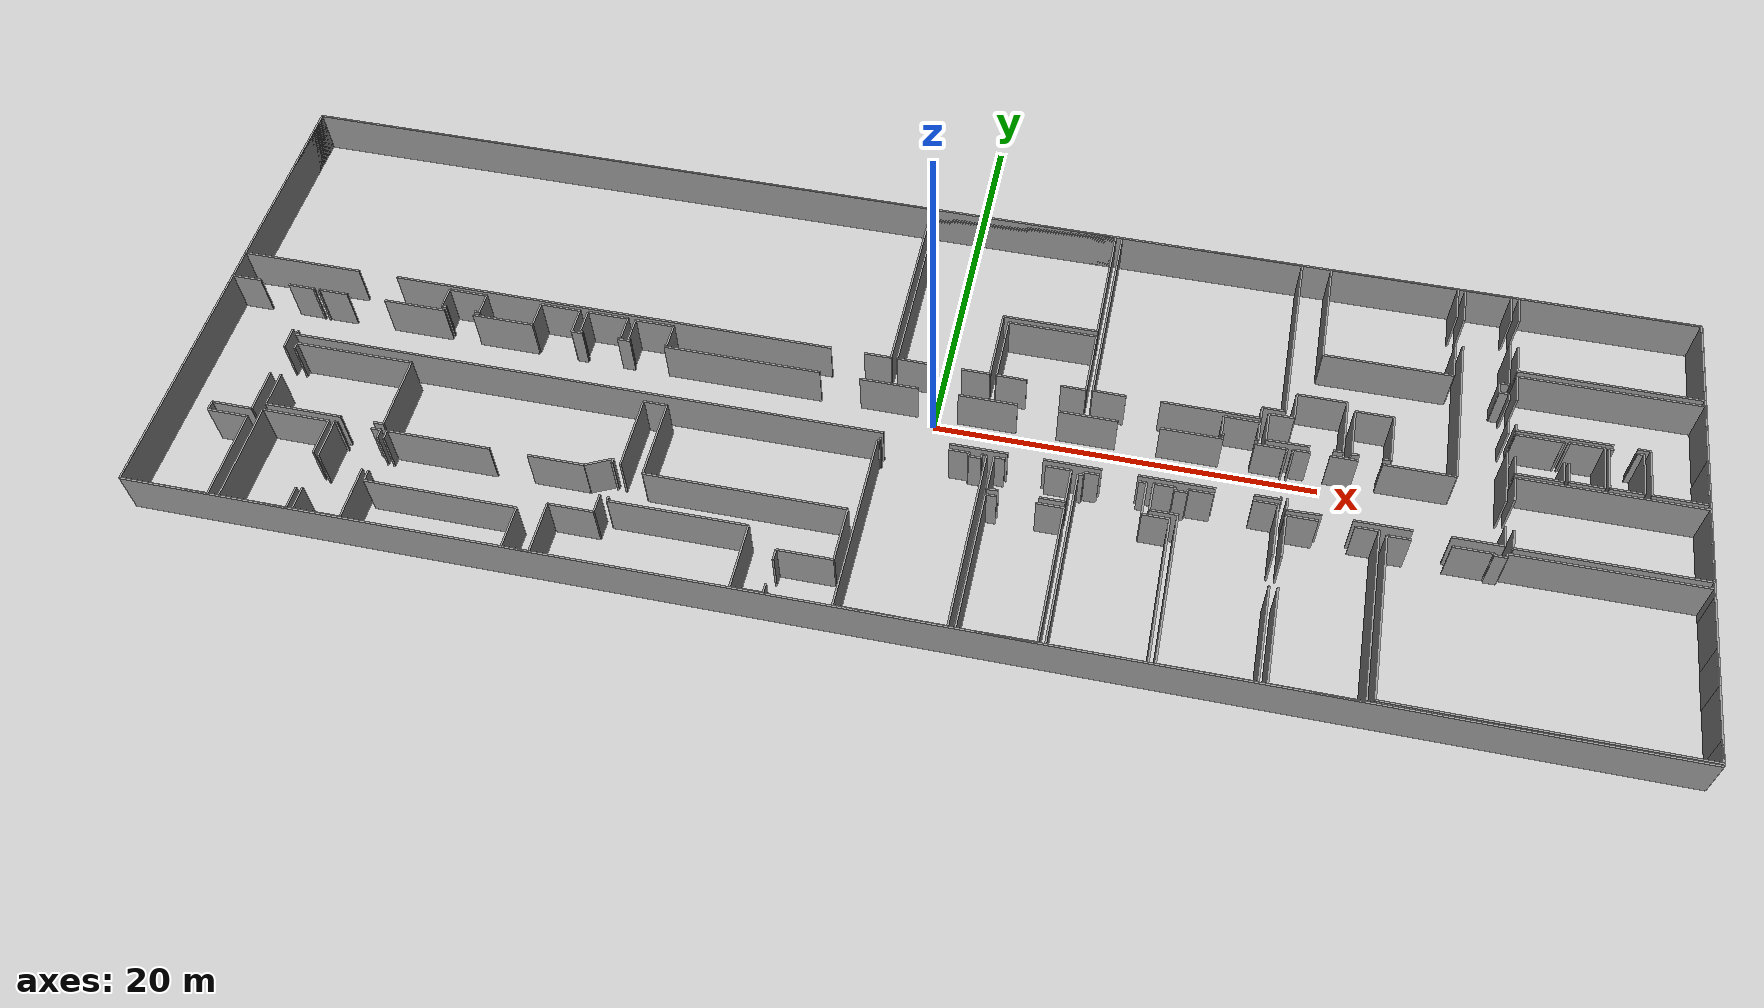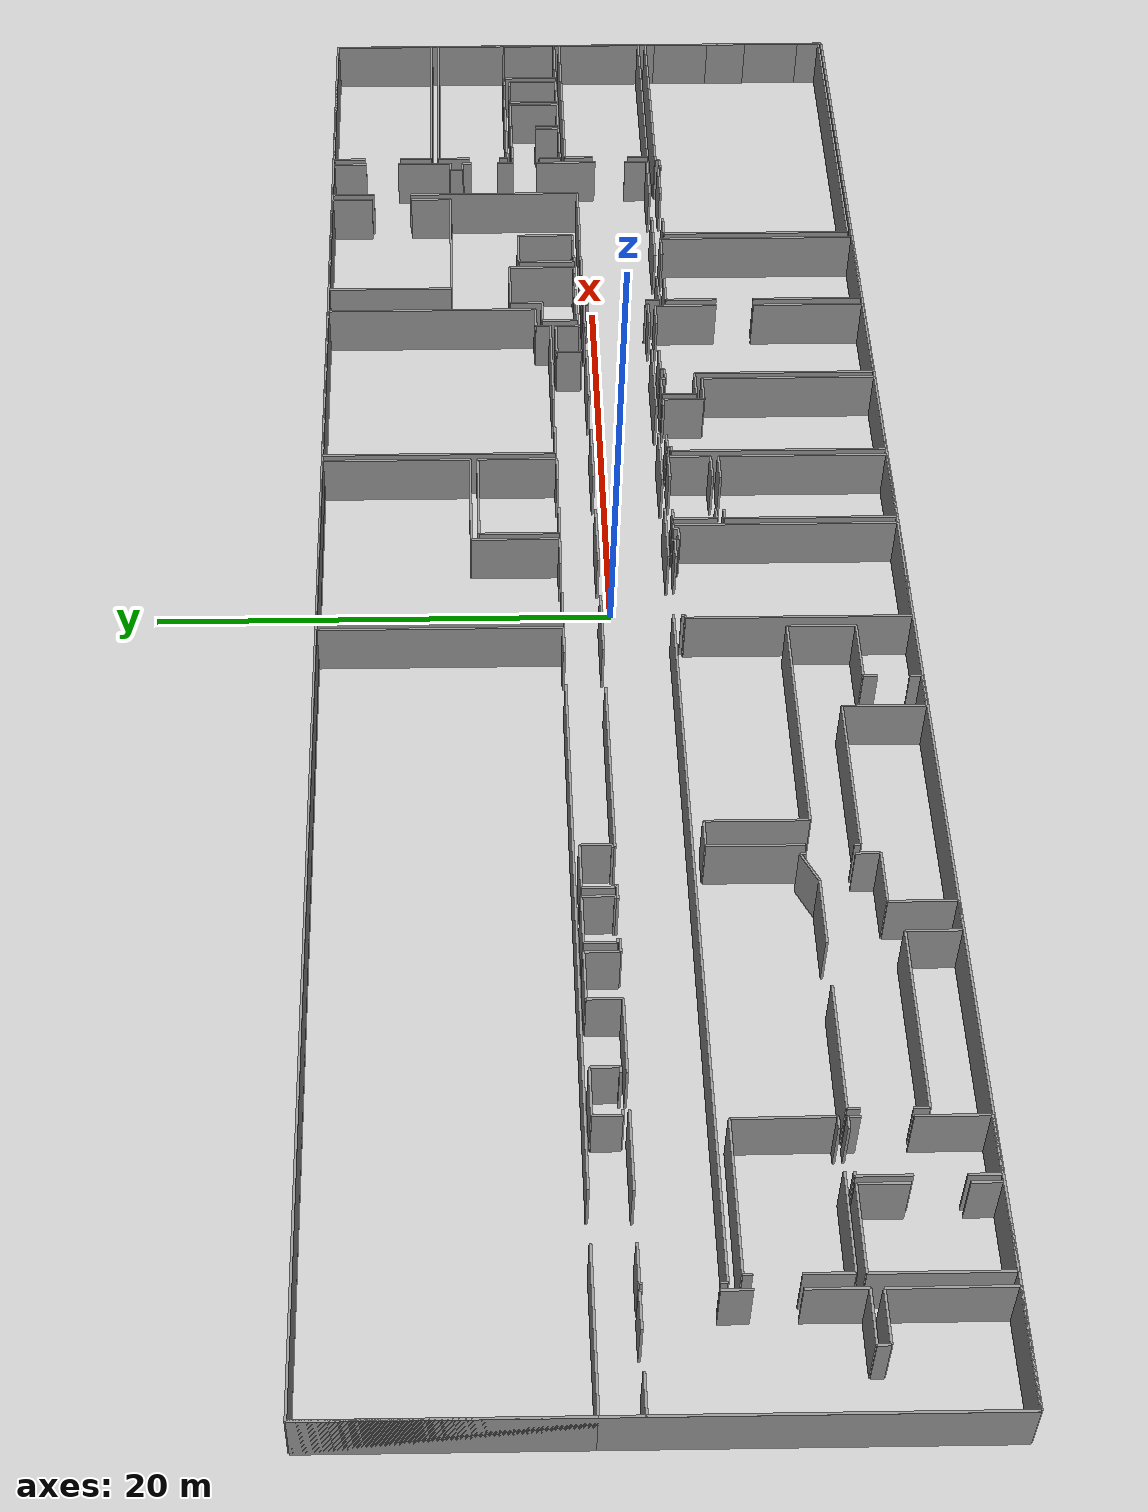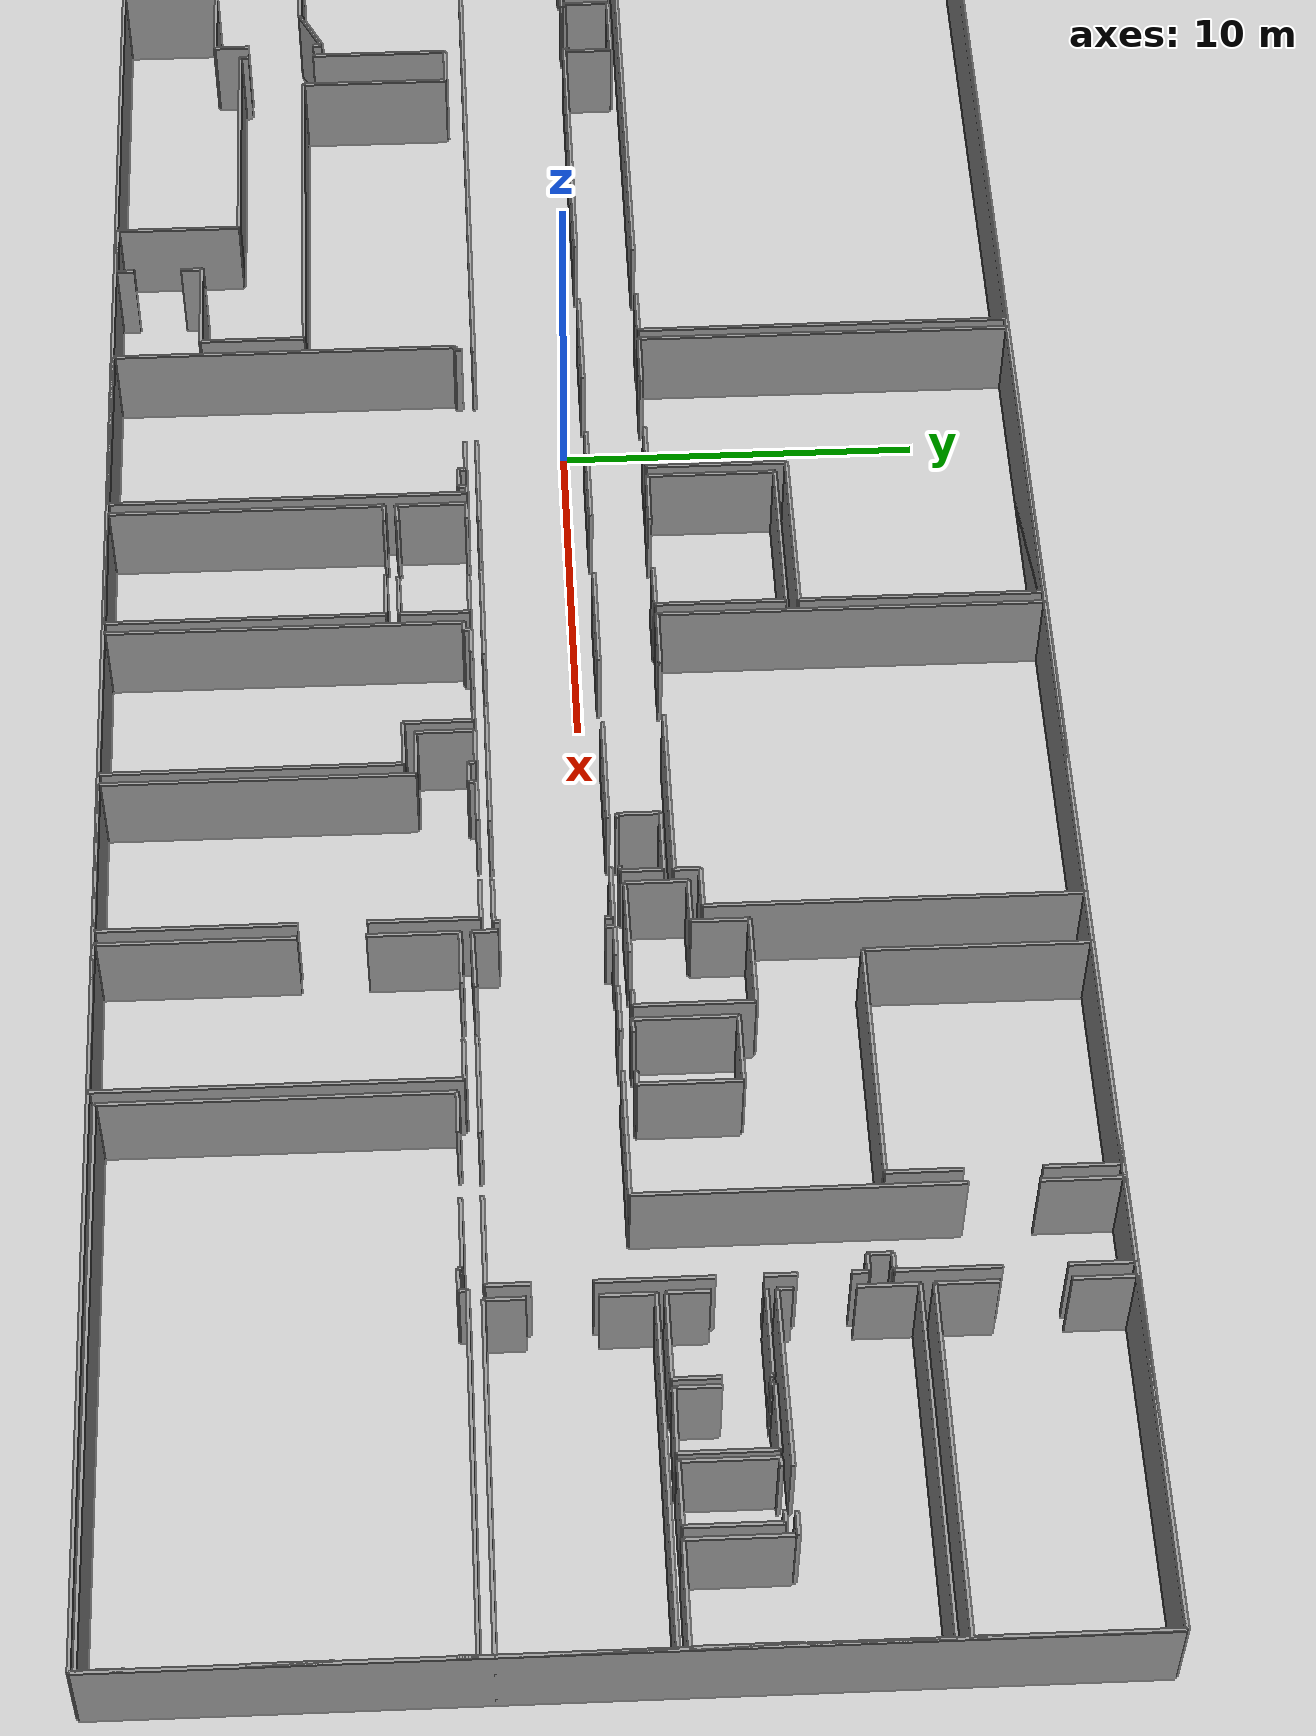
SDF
<sdf version="1.6">
  <world name="default">
    <light name="sun" type="directional">
      <cast_shadows>1</cast_shadows>
      <pose frame="">0 0 10 0 -0 0</pose>
      <diffuse>0.8 0.8 0.8 1</diffuse>
      <specular>0.1 0.1 0.1 1</specular>
      <attenuation>
        <range>1000</range>
        <constant>0.9</constant>
        <linear>0.01</linear>
        <quadratic>0.001</quadratic>
      </attenuation>
      <direction>-0.5 0.5 -1</direction>
    </light>
    <model name="ground_plane">
      <static>1</static>
      <link name="link">
        <collision name="collision">
          <geometry>
            <plane>
              <normal>0 0 1</normal>
              <size>100 100</size>
            </plane>
          </geometry>
          <surface>
            <friction>
              <ode>
                <mu>100</mu>
                <mu2>50</mu2>
              </ode>
              <torsional>
                <ode />
              </torsional>
            </friction>
            <contact>
              <ode />
            </contact>
            <bounce />
          </surface>
          <max_contacts>10</max_contacts>
        </collision>
        <visual name="visual">
          <cast_shadows>0</cast_shadows>
          <geometry>
            <plane>
              <normal>0 0 1</normal>
              <size>100 100</size>
            </plane>
          </geometry>
          <material>
            <script>
              <uri>file://media/materials/scripts/gazebo.material</uri>
              <name>Gazebo/Grey</name>
            </script>
          </material>
        </visual>
        <self_collide>0</self_collide>
        <kinematic>0</kinematic>
        <gravity>1</gravity>
      </link>
    </model>
    <gravity>0 0 -9.8</gravity>
    <magnetic_field>6e-06 2.3e-05 -4.2e-05</magnetic_field>
    <atmosphere type="adiabatic" />
    <physics default="0" name="default_physics" type="ode">
      <max_step_size>0.001</max_step_size>
      <real_time_factor>1</real_time_factor>
      <real_time_update_rate>1000</real_time_update_rate>
    </physics>
    <scene>
      <ambient>0.4 0.4 0.4 1</ambient>
      <background>0.7 0.7 0.7 1</background>
      <shadows>1</shadows>
    </scene>
    <spherical_coordinates>
      <surface_model>EARTH_WGS84</surface_model>
      <latitude_deg>0</latitude_deg>
      <longitude_deg>0</longitude_deg>
      <elevation>0</elevation>
      <heading_deg>0</heading_deg>
    </spherical_coordinates>
  <model name="0510030965_A-40">
		<static>1</static>
		<link name="Wall_0">
			<collision name="Wall_0_Collision">
				<geometry>
					<box>
						<size>10.6242301881 0.1 2.5</size>
					</box>
				</geometry>
				<pose frame="">5.31211509403 0 1.25 0 0 0</pose>
			</collision>
			<visual name="Wall_0_Visual">
				<pose frame="">5.31211509403 0 1.25 0 0 0</pose>
				<geometry>
					<box>
						<size>10.6242301881 0.1 2.5</size>
					</box>
				</geometry>
				<material>
					<script>
						<uri>file://media/materials/scripts/gazebo.material</uri>
						<name>Gazebo/Grey</name>
					</script>
					<ambient>1 1 1 1</ambient>
				</material>
			</visual>
			<pose frame="">0.0 -10.6242301881 0 0 0 1.57079632679</pose>
		</link>
		<link name="Wall_1">
			<collision name="Wall_1_Collision">
				<geometry>
					<box>
						<size>35.9684075527 0.1 2.5</size>
					</box>
				</geometry>
				<pose frame="">17.9842037764 0 1.25 0 0 0</pose>
			</collision>
			<visual name="Wall_1_Visual">
				<pose frame="">17.9842037764 0 1.25 0 0 0</pose>
				<geometry>
					<box>
						<size>35.9684075527 0.1 2.5</size>
					</box>
				</geometry>
				<material>
					<script>
						<uri>file://media/materials/scripts/gazebo.material</uri>
						<name>Gazebo/Grey</name>
					</script>
					<ambient>1 1 1 1</ambient>
				</material>
			</visual>
			<pose frame="">0.0 -0.0 0 0 0 0.0</pose>
		</link>
		<link name="Wall_2">
			<collision name="Wall_2_Collision">
				<geometry>
					<box>
						<size>10.6120401762 0.1 2.5</size>
					</box>
				</geometry>
				<pose frame="">5.30602008812 0 1.25 0 0 0</pose>
			</collision>
			<visual name="Wall_2_Visual">
				<pose frame="">5.30602008812 0 1.25 0 0 0</pose>
				<geometry>
					<box>
						<size>10.6120401762 0.1 2.5</size>
					</box>
				</geometry>
				<material>
					<script>
						<uri>file://media/materials/scripts/gazebo.material</uri>
						<name>Gazebo/Grey</name>
					</script>
					<ambient>1 1 1 1</ambient>
				</material>
			</visual>
			<pose frame="">35.9684075527 -0.0 0 0 0 -1.57079632679</pose>
		</link>
		<link name="Wall_3">
			<collision name="Wall_3_Collision">
				<geometry>
					<box>
						<size>1.43537389052 0.1 2.5</size>
					</box>
				</geometry>
				<pose frame="">0.717686945259 0 1.25 0 0 0</pose>
			</collision>
			<visual name="Wall_3_Visual">
				<pose frame="">0.717686945259 0 1.25 0 0 0</pose>
				<geometry>
					<box>
						<size>1.43537389052 0.1 2.5</size>
					</box>
				</geometry>
				<material>
					<script>
						<uri>file://media/materials/scripts/gazebo.material</uri>
						<name>Gazebo/Grey</name>
					</script>
					<ambient>1 1 1 1</ambient>
				</material>
			</visual>
			<pose frame="">35.9684075527 -10.6120401762 0 0 0 3.14159265359</pose>
		</link>
		<link name="Wall_4">
			<collision name="Wall_4_Collision">
				<geometry>
					<box>
						<size>24.041115894 0.1 2.5</size>
					</box>
				</geometry>
				<pose frame="">12.020557947 0 1.25 0 0 0</pose>
			</collision>
			<visual name="Wall_4_Visual">
				<pose frame="">12.020557947 0 1.25 0 0 0</pose>
				<geometry>
					<box>
						<size>24.041115894 0.1 2.5</size>
					</box>
				</geometry>
				<material>
					<script>
						<uri>file://media/materials/scripts/gazebo.material</uri>
						<name>Gazebo/Grey</name>
					</script>
					<ambient>1 1 1 1</ambient>
				</material>
			</visual>
			<pose frame="">32.7479588079 -10.6120401762 0 0 0 3.14159265359</pose>
		</link>
		<link name="Wall_5">
			<collision name="Wall_5_Collision">
				<geometry>
					<box>
						<size>6.55112685435 0.1 2.5</size>
					</box>
				</geometry>
				<pose frame="">3.27556342718 0 1.25 0 0 0</pose>
			</collision>
			<visual name="Wall_5_Visual">
				<pose frame="">3.27556342718 0 1.25 0 0 0</pose>
				<geometry>
					<box>
						<size>6.55112685435 0.1 2.5</size>
					</box>
				</geometry>
				<material>
					<script>
						<uri>file://media/materials/scripts/gazebo.material</uri>
						<name>Gazebo/Grey</name>
					</script>
					<ambient>1 1 1 1</ambient>
				</material>
			</visual>
			<pose frame="">6.55111551306 -10.6120401762 0 0 0 -3.13973190213</pose>
		</link>
		<link name="Wall_6">
			<collision name="Wall_6_Collision">
				<geometry>
					<box>
						<size>4.66648889566 0.1 2.5</size>
					</box>
				</geometry>
				<pose frame="">2.33324444783 0 1.25 0 0 0</pose>
			</collision>
			<visual name="Wall_6_Visual">
				<pose frame="">2.33324444783 0 1.25 0 0 0</pose>
				<geometry>
					<box>
						<size>4.66648889566 0.1 2.5</size>
					</box>
				</geometry>
				<material>
					<script>
						<uri>file://media/materials/scripts/gazebo.material</uri>
						<name>Gazebo/Grey</name>
					</script>
					<ambient>1 1 1 1</ambient>
				</material>
			</visual>
			<pose frame="">4.66826660572 -25.6908308255 0 0 0 3.14159265359</pose>
		</link>
		<link name="Wall_7">
			<collision name="Wall_7_Collision">
				<geometry>
					<box>
						<size>13.4218378982 0.1 2.5</size>
					</box>
				</geometry>
				<pose frame="">6.71091894912 0 1.25 0 0 0</pose>
			</collision>
			<visual name="Wall_7_Visual">
				<pose frame="">6.71091894912 0 1.25 0 0 0</pose>
				<geometry>
					<box>
						<size>13.4218378982 0.1 2.5</size>
					</box>
				</geometry>
				<material>
					<script>
						<uri>file://media/materials/scripts/gazebo.material</uri>
						<name>Gazebo/Grey</name>
					</script>
					<ambient>1 1 1 1</ambient>
				</material>
			</visual>
			<pose frame="">0.00177771005549 -25.6908308255 0 0 0 1.57079632679</pose>
		</link>
		<link name="Wall_8">
			<collision name="Wall_8_Collision">
				<geometry>
					<box>
						<size>1.61250999962 0.1 2.5</size>
					</box>
				</geometry>
				<pose frame="">0.80625499981 0 1.25 0 0 0</pose>
			</collision>
			<visual name="Wall_8_Visual">
				<pose frame="">0.80625499981 0 1.25 0 0 0</pose>
				<geometry>
					<box>
						<size>1.61250999962 0.1 2.5</size>
					</box>
				</geometry>
				<material>
					<script>
						<uri>file://media/materials/scripts/gazebo.material</uri>
						<name>Gazebo/Grey</name>
					</script>
					<ambient>1 1 1 1</ambient>
				</material>
			</visual>
			<pose frame="">0.00177771005549 -12.2689929273 0 0 0 0.0</pose>
		</link>
		<link name="Wall_9">
			<collision name="Wall_9_Collision">
				<geometry>
					<box>
						<size>1.44921463309 0.1 2.5</size>
					</box>
				</geometry>
				<pose frame="">0.724607316547 0 1.25 0 0 0</pose>
			</collision>
			<visual name="Wall_9_Visual">
				<pose frame="">0.724607316547 0 1.25 0 0 0</pose>
				<geometry>
					<box>
						<size>1.44921463309 0.1 2.5</size>
					</box>
				</geometry>
				<material>
					<script>
						<uri>file://media/materials/scripts/gazebo.material</uri>
						<name>Gazebo/Grey</name>
					</script>
					<ambient>1 1 1 1</ambient>
				</material>
			</visual>
			<pose frame="">3.21714728328 -12.2689929273 0 0 0 0.0</pose>
		</link>
		<link name="Wall_10">
			<collision name="Wall_10_Collision">
				<geometry>
					<box>
						<size>0.0816476832629 0.1 2.5</size>
					</box>
				</geometry>
				<pose frame="">0.0408238416314 0 1.25 0 0 0</pose>
			</collision>
			<visual name="Wall_10_Visual">
				<pose frame="">0.0408238416314 0 1.25 0 0 0</pose>
				<geometry>
					<box>
						<size>0.0816476832629 0.1 2.5</size>
					</box>
				</geometry>
				<material>
					<script>
						<uri>file://media/materials/scripts/gazebo.material</uri>
						<name>Gazebo/Grey</name>
					</script>
					<ambient>1 1 1 1</ambient>
				</material>
			</visual>
			<pose frame="">4.66636191637 -12.2689929273 0 0 0 -1.57079632679</pose>
		</link>
		<link name="Wall_11">
			<collision name="Wall_11_Collision">
				<geometry>
					<box>
						<size>1.176082181 0.1 2.5</size>
					</box>
				</geometry>
				<pose frame="">0.588041090498 0 1.25 0 0 0</pose>
			</collision>
			<visual name="Wall_11_Visual">
				<pose frame="">0.588041090498 0 1.25 0 0 0</pose>
				<geometry>
					<box>
						<size>1.176082181 0.1 2.5</size>
					</box>
				</geometry>
				<material>
					<script>
						<uri>file://media/materials/scripts/gazebo.material</uri>
						<name>Gazebo/Grey</name>
					</script>
					<ambient>1 1 1 1</ambient>
				</material>
			</visual>
			<pose frame="">4.66636191637 -15.1072340101 0 0 0 -1.57079632679</pose>
		</link>
		<link name="Wall_12">
			<collision name="Wall_12_Collision">
				<geometry>
					<box>
						<size>2.33718080581 0.1 2.5</size>
					</box>
				</geometry>
				<pose frame="">1.16859040291 0 1.25 0 0 0</pose>
			</collision>
			<visual name="Wall_12_Visual">
				<pose frame="">1.16859040291 0 1.25 0 0 0</pose>
				<geometry>
					<box>
						<size>2.33718080581 0.1 2.5</size>
					</box>
				</geometry>
				<material>
					<script>
						<uri>file://media/materials/scripts/gazebo.material</uri>
						<name>Gazebo/Grey</name>
					</script>
					<ambient>1 1 1 1</ambient>
				</material>
			</visual>
			<pose frame="">4.66636191637 -18.0428682082 0 0 0 -1.57079632679</pose>
		</link>
		<link name="Wall_13">
			<collision name="Wall_13_Collision">
				<geometry>
					<box>
						<size>2.16448897185 0.1 2.5</size>
					</box>
				</geometry>
				<pose frame="">1.08224448592 0 1.25 0 0 0</pose>
			</collision>
			<visual name="Wall_13_Visual">
				<pose frame="">1.08224448592 0 1.25 0 0 0</pose>
				<geometry>
					<box>
						<size>2.16448897185 0.1 2.5</size>
					</box>
				</geometry>
				<material>
					<script>
						<uri>file://media/materials/scripts/gazebo.material</uri>
						<name>Gazebo/Grey</name>
					</script>
					<ambient>1 1 1 1</ambient>
				</material>
			</visual>
			<pose frame="">4.66636191637 -20.380049014 0 0 0 3.14159265359</pose>
		</link>
		<link name="Wall_14">
			<collision name="Wall_14_Collision">
				<geometry>
					<box>
						<size>0.501060277069 0.1 2.5</size>
					</box>
				</geometry>
				<pose frame="">0.250530138534 0 1.25 0 0 0</pose>
			</collision>
			<visual name="Wall_14_Visual">
				<pose frame="">0.250530138534 0 1.25 0 0 0</pose>
				<geometry>
					<box>
						<size>0.501060277069 0.1 2.5</size>
					</box>
				</geometry>
				<material>
					<script>
						<uri>file://media/materials/scripts/gazebo.material</uri>
						<name>Gazebo/Grey</name>
					</script>
					<ambient>1 1 1 1</ambient>
				</material>
			</visual>
			<pose frame="">2.50187294452 -20.380049014 0 0 0 -1.57079632679</pose>
		</link>
		<link name="Wall_15">
			<collision name="Wall_15_Collision">
				<geometry>
					<box>
						<size>2.14569603698 0.1 2.5</size>
					</box>
				</geometry>
				<pose frame="">1.07284801849 0 1.25 0 0 0</pose>
			</collision>
			<visual name="Wall_15_Visual">
				<pose frame="">1.07284801849 0 1.25 0 0 0</pose>
				<geometry>
					<box>
						<size>2.14569603698 0.1 2.5</size>
					</box>
				</geometry>
				<material>
					<script>
						<uri>file://media/materials/scripts/gazebo.material</uri>
						<name>Gazebo/Grey</name>
					</script>
					<ambient>1 1 1 1</ambient>
				</material>
			</visual>
			<pose frame="">2.50187294452 -20.8811092911 0 0 0 0.0</pose>
		</link>
		<link name="Wall_16">
			<collision name="Wall_16_Collision">
				<geometry>
					<box>
						<size>4.80976606815 0.1 2.5</size>
					</box>
				</geometry>
				<pose frame="">2.40488303407 0 1.25 0 0 0</pose>
			</collision>
			<visual name="Wall_16_Visual">
				<pose frame="">2.40488303407 0 1.25 0 0 0</pose>
				<geometry>
					<box>
						<size>4.80976606815 0.1 2.5</size>
					</box>
				</geometry>
				<material>
					<script>
						<uri>file://media/materials/scripts/gazebo.material</uri>
						<name>Gazebo/Grey</name>
					</script>
					<ambient>1 1 1 1</ambient>
				</material>
			</visual>
			<pose frame="">4.6475689815 -20.8811092911 0 0 0 -1.56649306385</pose>
		</link>
		<link name="Wall_17">
			<collision name="Wall_17_Collision">
				<geometry>
					<box>
						<size>0.520615087679 0.1 2.5</size>
					</box>
				</geometry>
				<pose frame="">0.26030754384 0 1.25 0 0 0</pose>
			</collision>
			<visual name="Wall_17_Visual">
				<pose frame="">0.26030754384 0 1.25 0 0 0</pose>
				<geometry>
					<box>
						<size>0.520615087679 0.1 2.5</size>
					</box>
				</geometry>
				<material>
					<script>
						<uri>file://media/materials/scripts/gazebo.material</uri>
						<name>Gazebo/Grey</name>
					</script>
					<ambient>1 1 1 1</ambient>
				</material>
			</visual>
			<pose frame="">11.620128757 -19.9502241184 0 0 0 3.14159265359</pose>
		</link>
		<link name="Wall_18">
			<collision name="Wall_18_Collision">
				<geometry>
					<box>
						<size>4.08136832883 0.1 2.5</size>
					</box>
				</geometry>
				<pose frame="">2.04068416441 0 1.25 0 0 0</pose>
			</collision>
			<visual name="Wall_18_Visual">
				<pose frame="">2.04068416441 0 1.25 0 0 0</pose>
				<geometry>
					<box>
						<size>4.08136832883 0.1 2.5</size>
					</box>
				</geometry>
				<material>
					<script>
						<uri>file://media/materials/scripts/gazebo.material</uri>
						<name>Gazebo/Grey</name>
					</script>
					<ambient>1 1 1 1</ambient>
				</material>
			</visual>
			<pose frame="">9.3345015428 -19.9502241184 0 0 0 3.14159265359</pose>
		</link>
		<link name="Wall_19">
			<collision name="Wall_19_Collision">
				<geometry>
					<box>
						<size>1.89656267063 0.1 2.5</size>
					</box>
				</geometry>
				<pose frame="">0.948281335314 0 1.25 0 0 0</pose>
			</collision>
			<visual name="Wall_19_Visual">
				<pose frame="">0.948281335314 0 1.25 0 0 0</pose>
				<geometry>
					<box>
						<size>1.89656267063 0.1 2.5</size>
					</box>
				</geometry>
				<material>
					<script>
						<uri>file://media/materials/scripts/gazebo.material</uri>
						<name>Gazebo/Grey</name>
					</script>
					<ambient>1 1 1 1</ambient>
				</material>
			</visual>
			<pose frame="">5.25313321397 -19.9502241184 0 0 0 1.57079632679</pose>
		</link>
		<link name="Wall_20">
			<collision name="Wall_20_Collision">
				<geometry>
					<box>
						<size>0.358081596892 0.1 2.5</size>
					</box>
				</geometry>
				<pose frame="">0.179040798446 0 1.25 0 0 0</pose>
			</collision>
			<visual name="Wall_20_Visual">
				<pose frame="">0.179040798446 0 1.25 0 0 0</pose>
				<geometry>
					<box>
						<size>0.358081596892 0.1 2.5</size>
					</box>
				</geometry>
				<material>
					<script>
						<uri>file://media/materials/scripts/gazebo.material</uri>
						<name>Gazebo/Grey</name>
					</script>
					<ambient>1 1 1 1</ambient>
				</material>
			</visual>
			<pose frame="">5.25313321397 -16.2929666171 0 0 0 1.57079632679</pose>
		</link>
		<link name="Wall_21">
			<collision name="Wall_21_Collision">
				<geometry>
					<box>
						<size>6.32928269399 0.1 2.5</size>
					</box>
				</geometry>
				<pose frame="">3.164641347 0 1.25 0 0 0</pose>
			</collision>
			<visual name="Wall_21_Visual">
				<pose frame="">3.164641347 0 1.25 0 0 0</pose>
				<geometry>
					<box>
						<size>6.32928269399 0.1 2.5</size>
					</box>
				</geometry>
				<material>
					<script>
						<uri>file://media/materials/scripts/gazebo.material</uri>
						<name>Gazebo/Grey</name>
					</script>
					<ambient>1 1 1 1</ambient>
				</material>
			</visual>
			<pose frame="">5.25313321397 -15.9348850203 0 0 0 0.0</pose>
		</link>
		<link name="Wall_22">
			<collision name="Wall_22_Collision">
				<geometry>
					<box>
						<size>4.01551619751 0.1 2.5</size>
					</box>
				</geometry>
				<pose frame="">2.00775809875 0 1.25 0 0 0</pose>
			</collision>
			<visual name="Wall_22_Visual">
				<pose frame="">2.00775809875 0 1.25 0 0 0</pose>
				<geometry>
					<box>
						<size>4.01551619751 0.1 2.5</size>
					</box>
				</geometry>
				<material>
					<script>
						<uri>file://media/materials/scripts/gazebo.material</uri>
						<name>Gazebo/Grey</name>
					</script>
					<ambient>1 1 1 1</ambient>
				</material>
			</visual>
			<pose frame="">11.582415908 -15.9348850203 0 0 0 -1.56140440765</pose>
		</link>
		<link name="Wall_23">
			<collision name="Wall_23_Collision">
				<geometry>
					<box>
						<size>1.26268205656 0.1 2.5</size>
					</box>
				</geometry>
				<pose frame="">0.631341028278 0 1.25 0 0 0</pose>
			</collision>
			<visual name="Wall_23_Visual">
				<pose frame="">0.631341028278 0 1.25 0 0 0</pose>
				<geometry>
					<box>
						<size>1.26268205656 0.1 2.5</size>
					</box>
				</geometry>
				<material>
					<script>
						<uri>file://media/materials/scripts/gazebo.material</uri>
						<name>Gazebo/Grey</name>
					</script>
					<ambient>1 1 1 1</ambient>
				</material>
			</visual>
			<pose frame="">9.13057280358 -25.669117367 0 0 0 1.57079632679</pose>
		</link>
		<link name="Wall_24">
			<collision name="Wall_24_Collision">
				<geometry>
					<box>
						<size>2.12906175003 0.1 2.5</size>
					</box>
				</geometry>
				<pose frame="">1.06453087501 0 1.25 0 0 0</pose>
			</collision>
			<visual name="Wall_24_Visual">
				<pose frame="">1.06453087501 0 1.25 0 0 0</pose>
				<geometry>
					<box>
						<size>2.12906175003 0.1 2.5</size>
					</box>
				</geometry>
				<material>
					<script>
						<uri>file://media/materials/scripts/gazebo.material</uri>
						<name>Gazebo/Grey</name>
					</script>
					<ambient>1 1 1 1</ambient>
				</material>
			</visual>
			<pose frame="">9.13057280358 -22.4461290364 0 0 0 1.57079632679</pose>
		</link>
		<link name="Wall_25">
			<collision name="Wall_25_Collision">
				<geometry>
					<box>
						<size>0.179548715604 0.1 2.5</size>
					</box>
				</geometry>
				<pose frame="">0.0897743578022 0 1.25 0 0 0</pose>
			</collision>
			<visual name="Wall_25_Visual">
				<pose frame="">0.0897743578022 0 1.25 0 0 0</pose>
				<geometry>
					<box>
						<size>0.179548715604 0.1 2.5</size>
					</box>
				</geometry>
				<material>
					<script>
						<uri>file://media/materials/scripts/gazebo.material</uri>
						<name>Gazebo/Grey</name>
					</script>
					<ambient>1 1 1 1</ambient>
				</material>
			</visual>
			<pose frame="">9.13057280358 -20.3170672863 0 0 0 0.0</pose>
		</link>
		<link name="Wall_26">
			<collision name="Wall_26_Collision">
				<geometry>
					<box>
						<size>0.504996635049 0.1 2.5</size>
					</box>
				</geometry>
				<pose frame="">0.252498317524 0 1.25 0 0 0</pose>
			</collision>
			<visual name="Wall_26_Visual">
				<pose frame="">0.252498317524 0 1.25 0 0 0</pose>
				<geometry>
					<box>
						<size>0.504996635049 0.1 2.5</size>
					</box>
				</geometry>
				<material>
					<script>
						<uri>file://media/materials/scripts/gazebo.material</uri>
						<name>Gazebo/Grey</name>
					</script>
					<ambient>1 1 1 1</ambient>
				</material>
			</visual>
			<pose frame="">11.1066245095 -20.3170672863 0 0 0 0.0</pose>
		</link>
		<link name="Wall_27">
			<collision name="Wall_27_Collision">
				<geometry>
					<box>
						<size>0.478330984216 0.1 2.5</size>
					</box>
				</geometry>
				<pose frame="">0.239165492108 0 1.25 0 0 0</pose>
			</collision>
			<visual name="Wall_27_Visual">
				<pose frame="">0.239165492108 0 1.25 0 0 0</pose>
				<geometry>
					<box>
						<size>0.478330984216 0.1 2.5</size>
					</box>
				</geometry>
				<material>
					<script>
						<uri>file://media/materials/scripts/gazebo.material</uri>
						<name>Gazebo/Grey</name>
					</script>
					<ambient>1 1 1 1</ambient>
				</material>
			</visual>
			<pose frame="">11.6116211446 -20.3170672863 0 0 0 -1.57079632679</pose>
		</link>
		<link name="Wall_28">
			<collision name="Wall_28_Collision">
				<geometry>
					<box>
						<size>2.89792134903 0.1 2.5</size>
					</box>
				</geometry>
				<pose frame="">1.44896067451 0 1.25 0 0 0</pose>
			</collision>
			<visual name="Wall_28_Visual">
				<pose frame="">1.44896067451 0 1.25 0 0 0</pose>
				<geometry>
					<box>
						<size>2.89792134903 0.1 2.5</size>
					</box>
				</geometry>
				<material>
					<script>
						<uri>file://media/materials/scripts/gazebo.material</uri>
						<name>Gazebo/Grey</name>
					</script>
					<ambient>1 1 1 1</ambient>
				</material>
			</visual>
			<pose frame="">11.6116211446 -22.765101012 0 0 0 -1.57079632679</pose>
		</link>
		<link name="Wall_29">
			<collision name="Wall_29_Collision">
				<geometry>
					<box>
						<size>2.48105582758 0.1 2.5</size>
					</box>
				</geometry>
				<pose frame="">1.24052791379 0 1.25 0 0 0</pose>
			</collision>
			<visual name="Wall_29_Visual">
				<pose frame="">1.24052791379 0 1.25 0 0 0</pose>
				<geometry>
					<box>
						<size>2.48105582758 0.1 2.5</size>
					</box>
				</geometry>
				<material>
					<script>
						<uri>file://media/materials/scripts/gazebo.material</uri>
						<name>Gazebo/Grey</name>
					</script>
					<ambient>1 1 1 1</ambient>
				</material>
			</visual>
			<pose frame="">11.6116211446 -25.6630223611 0 0 0 -3.13913603332</pose>
		</link>
		<link name="Wall_30">
			<collision name="Wall_30_Collision">
				<geometry>
					<box>
						<size>3.57345117011 0.1 2.5</size>
					</box>
				</geometry>
				<pose frame="">1.78672558506 0 1.25 0 0 0</pose>
			</collision>
			<visual name="Wall_30_Visual">
				<pose frame="">1.78672558506 0 1.25 0 0 0</pose>
				<geometry>
					<box>
						<size>3.57345117011 0.1 2.5</size>
					</box>
				</geometry>
				<material>
					<script>
						<uri>file://media/materials/scripts/gazebo.material</uri>
						<name>Gazebo/Grey</name>
					</script>
					<ambient>1 1 1 1</ambient>
				</material>
			</visual>
			<pose frame="">8.81375947583 -25.6900689498 0 0 0 3.14159265359</pose>
		</link>
		<link name="Wall_31">
			<collision name="Wall_31_Collision">
				<geometry>
					<box>
						<size>5.36817645042 0.1 2.5</size>
					</box>
				</geometry>
				<pose frame="">2.68408822521 0 1.25 0 0 0</pose>
			</collision>
			<visual name="Wall_31_Visual">
				<pose frame="">2.68408822521 0 1.25 0 0 0</pose>
				<geometry>
					<box>
						<size>5.36817645042 0.1 2.5</size>
					</box>
				</geometry>
				<material>
					<script>
						<uri>file://media/materials/scripts/gazebo.material</uri>
						<name>Gazebo/Grey</name>
					</script>
					<ambient>1 1 1 1</ambient>
				</material>
			</visual>
			<pose frame="">5.24030830572 -25.6900689498 0 0 0 1.57079632679</pose>
		</link>
		<link name="Wall_32">
			<collision name="Wall_32_Collision">
				<geometry>
					<box>
						<size>3.57459398372 0.1 2.5</size>
					</box>
				</geometry>
				<pose frame="">1.78729699186 0 1.25 0 0 0</pose>
			</collision>
			<visual name="Wall_32_Visual">
				<pose frame="">1.78729699186 0 1.25 0 0 0</pose>
				<geometry>
					<box>
						<size>3.57459398372 0.1 2.5</size>
					</box>
				</geometry>
				<material>
					<script>
						<uri>file://media/materials/scripts/gazebo.material</uri>
						<name>Gazebo/Grey</name>
					</script>
					<ambient>1 1 1 1</ambient>
				</material>
			</visual>
			<pose frame="">5.24030830572 -20.3218924993 0 0 0 0.0</pose>
		</link>
		<link name="Wall_33">
			<collision name="Wall_33_Collision">
				<geometry>
					<box>
						<size>1.98862265564 0.1 2.5</size>
					</box>
				</geometry>
				<pose frame="">0.994311327822 0 1.25 0 0 0</pose>
			</collision>
			<visual name="Wall_33_Visual">
				<pose frame="">0.994311327822 0 1.25 0 0 0</pose>
				<geometry>
					<box>
						<size>1.98862265564 0.1 2.5</size>
					</box>
				</geometry>
				<material>
					<script>
						<uri>file://media/materials/scripts/gazebo.material</uri>
						<name>Gazebo/Grey</name>
					</script>
					<ambient>1 1 1 1</ambient>
				</material>
			</visual>
			<pose frame="">8.81490228944 -20.3218924993 0 0 0 -1.57079632679</pose>
		</link>
		<link name="Wall_34">
			<collision name="Wall_34_Collision">
				<geometry>
					<box>
						<size>1.21125598336 0.1 2.5</size>
					</box>
				</geometry>
				<pose frame="">0.605627991678 0 1.25 0 0 0</pose>
			</collision>
			<visual name="Wall_34_Visual">
				<pose frame="">0.605627991678 0 1.25 0 0 0</pose>
				<geometry>
					<box>
						<size>1.21125598336 0.1 2.5</size>
					</box>
				</geometry>
				<material>
					<script>
						<uri>file://media/materials/scripts/gazebo.material</uri>
						<name>Gazebo/Grey</name>
					</script>
					<ambient>1 1 1 1</ambient>
				</material>
			</visual>
			<pose frame="">8.81490228944 -24.4788135055 0 0 0 -1.57173982164</pose>
		</link>
		<link name="Wall_35">
			<collision name="Wall_35_Collision">
				<geometry>
					<box>
						<size>0.609500590454 0.1 2.5</size>
					</box>
				</geometry>
				<pose frame="">0.304750295227 0 1.25 0 0 0</pose>
			</collision>
			<visual name="Wall_35_Visual">
				<pose frame="">0.304750295227 0 1.25 0 0 0</pose>
				<geometry>
					<box>
						<size>0.609500590454 0.1 2.5</size>
					</box>
				</geometry>
				<material>
					<script>
						<uri>file://media/materials/scripts/gazebo.material</uri>
						<name>Gazebo/Grey</name>
					</script>
					<ambient>1 1 1 1</ambient>
				</material>
			</visual>
			<pose frame="">11.9530684545 -23.3941564131 0 0 0 1.57079632679</pose>
		</link>
		<link name="Wall_36">
			<collision name="Wall_36_Collision">
				<geometry>
					<box>
						<size>0.496362043351 0.1 2.5</size>
					</box>
				</geometry>
				<pose frame="">0.248181021675 0 1.25 0 0 0</pose>
			</collision>
			<visual name="Wall_36_Visual">
				<pose frame="">0.248181021675 0 1.25 0 0 0</pose>
				<geometry>
					<box>
						<size>0.496362043351 0.1 2.5</size>
					</box>
				</geometry>
				<material>
					<script>
						<uri>file://media/materials/scripts/gazebo.material</uri>
						<name>Gazebo/Grey</name>
					</script>
					<ambient>1 1 1 1</ambient>
				</material>
			</visual>
			<pose frame="">11.9530684545 -20.808731096 0 0 0 1.57079632679</pose>
		</link>
		<link name="Wall_37">
			<collision name="Wall_37_Collision">
				<geometry>
					<box>
						<size>5.46277602123 0.1 2.5</size>
					</box>
				</geometry>
				<pose frame="">2.73138801062 0 1.25 0 0 0</pose>
			</collision>
			<visual name="Wall_37_Visual">
				<pose frame="">2.73138801062 0 1.25 0 0 0</pose>
				<geometry>
					<box>
						<size>5.46277602123 0.1 2.5</size>
					</box>
				</geometry>
				<material>
					<script>
						<uri>file://media/materials/scripts/gazebo.material</uri>
						<name>Gazebo/Grey</name>
					</script>
					<ambient>1 1 1 1</ambient>
				</material>
			</visual>
			<pose frame="">11.9530684545 -20.3123690526 0 0 0 0.0</pose>
		</link>
		<link name="Wall_38">
			<collision name="Wall_38_Collision">
				<geometry>
					<box>
						<size>2.97360100568 0.1 2.5</size>
					</box>
				</geometry>
				<pose frame="">1.48680050284 0 1.25 0 0 0</pose>
			</collision>
			<visual name="Wall_38_Visual">
				<pose frame="">1.48680050284 0 1.25 0 0 0</pose>
				<geometry>
					<box>
						<size>2.97360100568 0.1 2.5</size>
					</box>
				</geometry>
				<material>
					<script>
						<uri>file://media/materials/scripts/gazebo.material</uri>
						<name>Gazebo/Grey</name>
					</script>
					<ambient>1 1 1 1</ambient>
				</material>
			</visual>
			<pose frame="">19.4082765101 -20.3123690526 0 0 0 0.0</pose>
		</link>
		<link name="Wall_39">
			<collision name="Wall_39_Collision">
				<geometry>
					<box>
						<size>1.47790270101 0.1 2.5</size>
					</box>
				</geometry>
				<pose frame="">0.738951350506 0 1.25 0 0 0</pose>
			</collision>
			<visual name="Wall_39_Visual">
				<pose frame="">0.738951350506 0 1.25 0 0 0</pose>
				<geometry>
					<box>
						<size>1.47790270101 0.1 2.5</size>
					</box>
				</geometry>
				<material>
					<script>
						<uri>file://media/materials/scripts/gazebo.material</uri>
						<name>Gazebo/Grey</name>
					</script>
					<ambient>1 1 1 1</ambient>
				</material>
			</visual>
			<pose frame="">22.3818775158 -20.3123690526 0 0 0 0.457883984062</pose>
		</link>
		<link name="Wall_40">
			<collision name="Wall_40_Collision">
				<geometry>
					<box>
						<size>0.258783792363 0.1 2.5</size>
					</box>
				</geometry>
				<pose frame="">0.129391896182 0 1.25 0 0 0</pose>
			</collision>
			<visual name="Wall_40_Visual">
				<pose frame="">0.129391896182 0 1.25 0 0 0</pose>
				<geometry>
					<box>
						<size>0.258783792363 0.1 2.5</size>
					</box>
				</geometry>
				<material>
					<script>
						<uri>file://media/materials/scripts/gazebo.material</uri>
						<name>Gazebo/Grey</name>
					</script>
					<ambient>1 1 1 1</ambient>
				</material>
			</visual>
			<pose frame="">23.7075413 -19.6590606072 0 0 0 -1.57079632679</pose>
		</link>
		<link name="Wall_41">
			<collision name="Wall_41_Collision">
				<geometry>
					<box>
						<size>1.01024722868 0.1 2.5</size>
					</box>
				</geometry>
				<pose frame="">0.505123614339 0 1.25 0 0 0</pose>
			</collision>
			<visual name="Wall_41_Visual">
				<pose frame="">0.505123614339 0 1.25 0 0 0</pose>
				<geometry>
					<box>
						<size>1.01024722868 0.1 2.5</size>
					</box>
				</geometry>
				<material>
					<script>
						<uri>file://media/materials/scripts/gazebo.material</uri>
						<name>Gazebo/Grey</name>
					</script>
					<ambient>1 1 1 1</ambient>
				</material>
			</visual>
			<pose frame="">23.7075413 -21.8745952535 0 0 0 -1.57079632679</pose>
		</link>
		<link name="Wall_42">
			<collision name="Wall_42_Collision">
				<geometry>
					<box>
						<size>2.37844907496 0.1 2.5</size>
					</box>
				</geometry>
				<pose frame="">1.18922453748 0 1.25 0 0 0</pose>
			</collision>
			<visual name="Wall_42_Visual">
				<pose frame="">1.18922453748 0 1.25 0 0 0</pose>
				<geometry>
					<box>
						<size>2.37844907496 0.1 2.5</size>
					</box>
				</geometry>
				<material>
					<script>
						<uri>file://media/materials/scripts/gazebo.material</uri>
						<name>Gazebo/Grey</name>
					</script>
					<ambient>1 1 1 1</ambient>
				</material>
			</visual>
			<pose frame="">23.7075413 -22.8848424822 0 0 0 3.14159265359</pose>
		</link>
		<link name="Wall_43">
			<collision name="Wall_43_Collision">
				<geometry>
					<box>
						<size>2.8059883433 0.1 2.5</size>
					</box>
				</geometry>
				<pose frame="">1.40299417165 0 1.25 0 0 0</pose>
			</collision>
			<visual name="Wall_43_Visual">
				<pose frame="">1.40299417165 0 1.25 0 0 0</pose>
				<geometry>
					<box>
						<size>2.8059883433 0.1 2.5</size>
					</box>
				</geometry>
				<material>
					<script>
						<uri>file://media/materials/scripts/gazebo.material</uri>
						<name>Gazebo/Grey</name>
					</script>
					<ambient>1 1 1 1</ambient>
				</material>
			</visual>
			<pose frame="">21.3290922251 -22.8848424822 0 0 0 -1.57079632679</pose>
		</link>
		<link name="Wall_44">
			<collision name="Wall_44_Collision">
				<geometry>
					<box>
						<size>1.4122636598 0.1 2.5</size>
					</box>
				</geometry>
				<pose frame="">0.706131829899 0 1.25 0 0 0</pose>
			</collision>
			<visual name="Wall_44_Visual">
				<pose frame="">0.706131829899 0 1.25 0 0 0</pose>
				<geometry>
					<box>
						<size>1.4122636598 0.1 2.5</size>
					</box>
				</geometry>
				<material>
					<script>
						<uri>file://media/materials/scripts/gazebo.material</uri>
						<name>Gazebo/Grey</name>
					</script>
					<ambient>1 1 1 1</ambient>
				</material>
			</visual>
			<pose frame="">21.3290922251 -25.6908308255 0 0 0 3.14159265359</pose>
		</link>
		<link name="Wall_45">
			<collision name="Wall_45_Collision">
				<geometry>
					<box>
						<size>2.28004012546 0.1 2.5</size>
					</box>
				</geometry>
				<pose frame="">1.14002006273 0 1.25 0 0 0</pose>
			</collision>
			<visual name="Wall_45_Visual">
				<pose frame="">1.14002006273 0 1.25 0 0 0</pose>
				<geometry>
					<box>
						<size>2.28004012546 0.1 2.5</size>
					</box>
				</geometry>
				<material>
					<script>
						<uri>file://media/materials/scripts/gazebo.material</uri>
						<name>Gazebo/Grey</name>
					</script>
					<ambient>1 1 1 1</ambient>
				</material>
			</visual>
			<pose frame="">19.9168285653 -25.6908308255 0 0 0 1.57079632679</pose>
		</link>
		<link name="Wall_46">
			<collision name="Wall_46_Collision">
				<geometry>
					<box>
						<size>7.96377748312 0.1 2.5</size>
					</box>
				</geometry>
				<pose frame="">3.98188874156 0 1.25 0 0 0</pose>
			</collision>
			<visual name="Wall_46_Visual">
				<pose frame="">3.98188874156 0 1.25 0 0 0</pose>
				<geometry>
					<box>
						<size>7.96377748312 0.1 2.5</size>
					</box>
				</geometry>
				<material>
					<script>
						<uri>file://media/materials/scripts/gazebo.material</uri>
						<name>Gazebo/Grey</name>
					</script>
					<ambient>1 1 1 1</ambient>
				</material>
			</visual>
			<pose frame="">19.9168285653 -23.4107907 0 0 0 3.13950390876</pose>
		</link>
		<link name="Wall_47">
			<collision name="Wall_47_Collision">
				<geometry>
					<box>
						<size>0.250403159245 0.1 2.5</size>
					</box>
				</geometry>
				<pose frame="">0.125201579622 0 1.25 0 0 0</pose>
			</collision>
			<visual name="Wall_47_Visual">
				<pose frame="">0.125201579622 0 1.25 0 0 0</pose>
				<geometry>
					<box>
						<size>0.250403159245 0.1 2.5</size>
					</box>
				</geometry>
				<material>
					<script>
						<uri>file://media/materials/scripts/gazebo.material</uri>
						<name>Gazebo/Grey</name>
					</script>
					<ambient>1 1 1 1</ambient>
				</material>
			</visual>
			<pose frame="">24.1510799589 -22.1249984128 0 0 0 1.57079632679</pose>
		</link>
		<link name="Wall_48">
			<collision name="Wall_48_Collision">
				<geometry>
					<box>
						<size>3.9992127284 0.1 2.5</size>
					</box>
				</geometry>
				<pose frame="">1.9996063642 0 1.25 0 0 0</pose>
			</collision>
			<visual name="Wall_48_Visual">
				<pose frame="">1.9996063642 0 1.25 0 0 0</pose>
				<geometry>
					<box>
						<size>3.9992127284 0.1 2.5</size>
					</box>
				</geometry>
				<material>
					<script>
						<uri>file://media/materials/scripts/gazebo.material</uri>
						<name>Gazebo/Grey</name>
					</script>
					<ambient>1 1 1 1</ambient>
				</material>
			</visual>
			<pose frame="">24.1510799589 -19.9208919025 0 0 0 1.57079632679</pose>
		</link>
		<link name="Wall_49">
			<collision name="Wall_49_Collision">
				<geometry>
					<box>
						<size>1.25239673409 0.1 2.5</size>
					</box>
				</geometry>
				<pose frame="">0.626198367046 0 1.25 0 0 0</pose>
			</collision>
			<visual name="Wall_49_Visual">
				<pose frame="">0.626198367046 0 1.25 0 0 0</pose>
				<geometry>
					<box>
						<size>1.25239673409 0.1 2.5</size>
					</box>
				</geometry>
				<material>
					<script>
						<uri>file://media/materials/scripts/gazebo.material</uri>
						<name>Gazebo/Grey</name>
					</script>
					<ambient>1 1 1 1</ambient>
				</material>
			</visual>
			<pose frame="">24.1510799589 -15.9216791741 0 0 0 0.0</pose>
		</link>
		<link name="Wall_50">
			<collision name="Wall_50_Collision">
				<geometry>
					<box>
						<size>4.29520145264 0.1 2.5</size>
					</box>
				</geometry>
				<pose frame="">2.14760072632 0 1.25 0 0 0</pose>
			</collision>
			<visual name="Wall_50_Visual">
				<pose frame="">2.14760072632 0 1.25 0 0 0</pose>
				<geometry>
					<box>
						<size>4.29520145264 0.1 2.5</size>
					</box>
				</geometry>
				<material>
					<script>
						<uri>file://media/materials/scripts/gazebo.material</uri>
						<name>Gazebo/Grey</name>
					</script>
					<ambient>1 1 1 1</ambient>
				</material>
			</visual>
			<pose frame="">25.403476693 -15.9216791741 0 0 0 -1.57079632679</pose>
		</link>
		<link name="Wall_51">
			<collision name="Wall_51_Collision">
				<geometry>
					<box>
						<size>10.4906479753 0.1 2.5</size>
					</box>
				</geometry>
				<pose frame="">5.24532398766 0 1.25 0 0 0</pose>
			</collision>
			<visual name="Wall_51_Visual">
				<pose frame="">5.24532398766 0 1.25 0 0 0</pose>
				<geometry>
					<box>
						<size>10.4906479753 0.1 2.5</size>
					</box>
				</geometry>
				<material>
					<script>
						<uri>file://media/materials/scripts/gazebo.material</uri>
						<name>Gazebo/Grey</name>
					</script>
					<ambient>1 1 1 1</ambient>
				</material>
			</visual>
			<pose frame="">25.403476693 -20.2168806268 0 0 0 0.0</pose>
		</link>
		<link name="Wall_52">
			<collision name="Wall_52_Collision">
				<geometry>
					<box>
						<size>2.96750599977 0.1 2.5</size>
					</box>
				</geometry>
				<pose frame="">1.48375299989 0 1.25 0 0 0</pose>
			</collision>
			<visual name="Wall_52_Visual">
				<pose frame="">1.48375299989 0 1.25 0 0 0</pose>
				<geometry>
					<box>
						<size>2.96750599977 0.1 2.5</size>
					</box>
				</geometry>
				<material>
					<script>
						<uri>file://media/materials/scripts/gazebo.material</uri>
						<name>Gazebo/Grey</name>
					</script>
					<ambient>1 1 1 1</ambient>
				</material>
			</visual>
			<pose frame="">35.8941246683 -20.2168806268 0 0 0 -1.57079632679</pose>
		</link>
		<link name="Wall_53">
			<collision name="Wall_53_Collision">
				<geometry>
					<box>
						<size>2.87074778104 0.1 2.5</size>
					</box>
				</geometry>
				<pose frame="">1.43537389052 0 1.25 0 0 0</pose>
			</collision>
			<visual name="Wall_53_Visual">
				<pose frame="">1.43537389052 0 1.25 0 0 0</pose>
				<geometry>
					<box>
						<size>2.87074778104 0.1 2.5</size>
					</box>
				</geometry>
				<material>
					<script>
						<uri>file://media/materials/scripts/gazebo.material</uri>
						<name>Gazebo/Grey</name>
					</script>
					<ambient>1 1 1 1</ambient>
				</material>
			</visual>
			<pose frame="">35.8941246683 -23.1843866265 0 0 0 3.14159265359</pose>
		</link>
		<link name="Wall_54">
			<collision name="Wall_54_Collision">
				<geometry>
					<box>
						<size>0.607214963239 0.1 2.5</size>
					</box>
				</geometry>
				<pose frame="">0.30360748162 0 1.25 0 0 0</pose>
			</collision>
			<visual name="Wall_54_Visual">
				<pose frame="">0.30360748162 0 1.25 0 0 0</pose>
				<geometry>
					<box>
						<size>0.607214963239 0.1 2.5</size>
					</box>
				</geometry>
				<material>
					<script>
						<uri>file://media/materials/scripts/gazebo.material</uri>
						<name>Gazebo/Grey</name>
					</script>
					<ambient>1 1 1 1</ambient>
				</material>
			</visual>
			<pose frame="">33.0233768872 -23.1843866265 0 0 0 -1.57079632679</pose>
		</link>
		<link name="Wall_55">
			<collision name="Wall_55_Collision">
				<geometry>
					<box>
						<size>0.507917158711 0.1 2.5</size>
					</box>
				</geometry>
				<pose frame="">0.253958579356 0 1.25 0 0 0</pose>
			</collision>
			<visual name="Wall_55_Visual">
				<pose frame="">0.253958579356 0 1.25 0 0 0</pose>
				<geometry>
					<box>
						<size>0.507917158711 0.1 2.5</size>
					</box>
				</geometry>
				<material>
					<script>
						<uri>file://media/materials/scripts/gazebo.material</uri>
						<name>Gazebo/Grey</name>
					</script>
					<ambient>1 1 1 1</ambient>
				</material>
			</visual>
			<pose frame="">33.0233768872 -25.1497720722 0 0 0 -1.57079632679</pose>
		</link>
		<link name="Wall_56">
			<collision name="Wall_56_Collision">
				<geometry>
					<box>
						<size>1.65631785456 0.1 2.5</size>
					</box>
				</geometry>
				<pose frame="">0.828158927279 0 1.25 0 0 0</pose>
			</collision>
			<visual name="Wall_56_Visual">
				<pose frame="">0.828158927279 0 1.25 0 0 0</pose>
				<geometry>
					<box>
						<size>1.65631785456 0.1 2.5</size>
					</box>
				</geometry>
				<material>
					<script>
						<uri>file://media/materials/scripts/gazebo.material</uri>
						<name>Gazebo/Grey</name>
					</script>
					<ambient>1 1 1 1</ambient>
				</material>
			</visual>
			<pose frame="">33.0233768872 -25.6576892309 0 0 0 3.14159265359</pose>
		</link>
		<link name="Wall_57">
			<collision name="Wall_57_Collision">
				<geometry>
					<box>
						<size>3.53865884474 0.1 2.5</size>
					</box>
				</geometry>
				<pose frame="">1.76932942237 0 1.25 0 0 0</pose>
			</collision>
			<visual name="Wall_57_Visual">
				<pose frame="">1.76932942237 0 1.25 0 0 0</pose>
				<geometry>
					<box>
						<size>3.53865884474 0.1 2.5</size>
					</box>
				</geometry>
				<material>
					<script>
						<uri>file://media/materials/scripts/gazebo.material</uri>
						<name>Gazebo/Grey</name>
					</script>
					<ambient>1 1 1 1</ambient>
				</material>
			</visual>
			<pose frame="">31.3670590327 -25.6576892309 0 0 0 1.57079632679</pose>
		</link>
		<link name="Wall_58">
			<collision name="Wall_58_Collision">
				<geometry>
					<box>
						<size>7.21598154176 0.1 2.5</size>
					</box>
				</geometry>
				<pose frame="">3.60799077088 0 1.25 0 0 0</pose>
			</collision>
			<visual name="Wall_58_Visual">
				<pose frame="">3.60799077088 0 1.25 0 0 0</pose>
				<geometry>
					<box>
						<size>7.21598154176 0.1 2.5</size>
					</box>
				</geometry>
				<material>
					<script>
						<uri>file://media/materials/scripts/gazebo.material</uri>
						<name>Gazebo/Grey</name>
					</script>
					<ambient>1 1 1 1</ambient>
				</material>
			</visual>
			<pose frame="">31.3670590327 -22.1190303861 0 0 0 -3.14076559669</pose>
		</link>
		<link name="Wall_59">
			<collision name="Wall_59_Collision">
				<geometry>
					<box>
						<size>0.265259736137 0.1 2.5</size>
					</box>
				</geometry>
				<pose frame="">0.132629868069 0 1.25 0 0 0</pose>
			</collision>
			<visual name="Wall_59_Visual">
				<pose frame="">0.132629868069 0 1.25 0 0 0</pose>
				<geometry>
					<box>
						<size>0.265259736137 0.1 2.5</size>
					</box>
				</geometry>
				<material>
					<script>
						<uri>file://media/materials/scripts/gazebo.material</uri>
						<name>Gazebo/Grey</name>
					</script>
					<ambient>1 1 1 1</ambient>
				</material>
			</visual>
			<pose frame="">4.95765240689 -15.3914136604 0 0 0 1.57079632679</pose>
		</link>
		<link name="Wall_60">
			<collision name="Wall_60_Collision">
				<geometry>
					<box>
						<size>0.100186659556 0.1 2.5</size>
					</box>
				</geometry>
				<pose frame="">0.0500933297779 0 1.25 0 0 0</pose>
			</collision>
			<visual name="Wall_60_Visual">
				<pose frame="">0.0500933297779 0 1.25 0 0 0</pose>
				<geometry>
					<box>
						<size>0.100186659556 0.1 2.5</size>
					</box>
				</geometry>
				<material>
					<script>
						<uri>file://media/materials/scripts/gazebo.material</uri>
						<name>Gazebo/Grey</name>
					</script>
					<ambient>1 1 1 1</ambient>
				</material>
			</visual>
			<pose frame="">4.95765240689 -12.3733699034 0 0 0 1.57079632679</pose>
		</link>
		<link name="Wall_61">
			<collision name="Wall_61_Collision">
				<geometry>
					<box>
						<size>1.58774903813 0.1 2.5</size>
					</box>
				</geometry>
				<pose frame="">0.793874519066 0 1.25 0 0 0</pose>
			</collision>
			<visual name="Wall_61_Visual">
				<pose frame="">0.793874519066 0 1.25 0 0 0</pose>
				<geometry>
					<box>
						<size>1.58774903813 0.1 2.5</size>
					</box>
				</geometry>
				<material>
					<script>
						<uri>file://media/materials/scripts/gazebo.material</uri>
						<name>Gazebo/Grey</name>
					</script>
					<ambient>1 1 1 1</ambient>
				</material>
			</visual>
			<pose frame="">4.95765240689 -12.2731832438 0 0 0 0.0</pose>
		</link>
		<link name="Wall_62">
			<collision name="Wall_62_Collision">
				<geometry>
					<box>
						<size>3.37498254035 0.1 2.5</size>
					</box>
				</geometry>
				<pose frame="">1.68749127017 0 1.25 0 0 0</pose>
			</collision>
			<visual name="Wall_62_Visual">
				<pose frame="">1.68749127017 0 1.25 0 0 0</pose>
				<geometry>
					<box>
						<size>3.37498254035 0.1 2.5</size>
					</box>
				</geometry>
				<material>
					<script>
						<uri>file://media/materials/scripts/gazebo.material</uri>
						<name>Gazebo/Grey</name>
					</script>
					<ambient>1 1 1 1</ambient>
				</material>
			</visual>
			<pose frame="">8.6653206862 -12.2731832438 0 0 0 0.0</pose>
		</link>
		<link name="Wall_63">
			<collision name="Wall_63_Collision">
				<geometry>
					<box>
						<size>3.30349320026 0.1 2.5</size>
					</box>
				</geometry>
				<pose frame="">1.65174660013 0 1.25 0 0 0</pose>
			</collision>
			<visual name="Wall_63_Visual">
				<pose frame="">1.65174660013 0 1.25 0 0 0</pose>
				<geometry>
					<box>
						<size>3.30349320026 0.1 2.5</size>
					</box>
				</geometry>
				<material>
					<script>
						<uri>file://media/materials/scripts/gazebo.material</uri>
						<name>Gazebo/Grey</name>
					</script>
					<ambient>1 1 1 1</ambient>
				</material>
			</visual>
			<pose frame="">13.6239889274 -12.2731832438 0 0 0 0.0</pose>
		</link>
		<link name="Wall_64">
			<collision name="Wall_64_Collision">
				<geometry>
					<box>
						<size>1.41861262428 0.1 2.5</size>
					</box>
				</geometry>
				<pose frame="">0.70930631214 0 1.25 0 0 0</pose>
			</collision>
			<visual name="Wall_64_Visual">
				<pose frame="">0.70930631214 0 1.25 0 0 0</pose>
				<geometry>
					<box>
						<size>1.41861262428 0.1 2.5</size>
					</box>
				</geometry>
				<material>
					<script>
						<uri>file://media/materials/scripts/gazebo.material</uri>
						<name>Gazebo/Grey</name>
					</script>
					<ambient>1 1 1 1</ambient>
				</material>
			</visual>
			<pose frame="">16.9274821277 -12.2731832438 0 0 0 1.57079632679</pose>
		</link>
		<link name="Wall_65">
			<collision name="Wall_65_Collision">
				<geometry>
					<box>
						<size>2.16982210202 0.1 2.5</size>
					</box>
				</geometry>
				<pose frame="">1.08491105101 0 1.25 0 0 0</pose>
			</collision>
			<visual name="Wall_65_Visual">
				<pose frame="">1.08491105101 0 1.25 0 0 0</pose>
				<geometry>
					<box>
						<size>2.16982210202 0.1 2.5</size>
					</box>
				</geometry>
				<material>
					<script>
						<uri>file://media/materials/scripts/gazebo.material</uri>
						<name>Gazebo/Grey</name>
					</script>
					<ambient>1 1 1 1</ambient>
				</material>
			</visual>
			<pose frame="">16.9274821277 -10.8545706195 0 0 0 0.0</pose>
		</link>
		<link name="Wall_66">
			<collision name="Wall_66_Collision">
				<geometry>
					<box>
						<size>1.4306756568 0.1 2.5</size>
					</box>
				</geometry>
				<pose frame="">0.7153378284 0 1.25 0 0 0</pose>
			</collision>
			<visual name="Wall_66_Visual">
				<pose frame="">0.7153378284 0 1.25 0 0 0</pose>
				<geometry>
					<box>
						<size>1.4306756568 0.1 2.5</size>
					</box>
				</geometry>
				<material>
					<script>
						<uri>file://media/materials/scripts/gazebo.material</uri>
						<name>Gazebo/Grey</name>
					</script>
					<ambient>1 1 1 1</ambient>
				</material>
			</visual>
			<pose frame="">19.0973042297 -10.8545706195 0 0 0 -1.57079632679</pose>
		</link>
		<link name="Wall_67">
			<collision name="Wall_67_Collision">
				<geometry>
					<box>
						<size>0.595405889299 0.1 2.5</size>
					</box>
				</geometry>
				<pose frame="">0.29770294465 0 1.25 0 0 0</pose>
			</collision>
			<visual name="Wall_67_Visual">
				<pose frame="">0.29770294465 0 1.25 0 0 0</pose>
				<geometry>
					<box>
						<size>0.595405889299 0.1 2.5</size>
					</box>
				</geometry>
				<material>
					<script>
						<uri>file://media/materials/scripts/gazebo.material</uri>
						<name>Gazebo/Grey</name>
					</script>
					<ambient>1 1 1 1</ambient>
				</material>
			</visual>
			<pose frame="">19.0973042297 -12.2852462763 0 0 0 0.0</pose>
		</link>
		<link name="Wall_68">
			<collision name="Wall_68_Collision">
				<geometry>
					<box>
						<size>0.684672329943 0.1 2.5</size>
					</box>
				</geometry>
				<pose frame="">0.342336164971 0 1.25 0 0 0</pose>
			</collision>
			<visual name="Wall_68_Visual">
				<pose frame="">0.342336164971 0 1.25 0 0 0</pose>
				<geometry>
					<box>
						<size>0.684672329943 0.1 2.5</size>
					</box>
				</geometry>
				<material>
					<script>
						<uri>file://media/materials/scripts/gazebo.material</uri>
						<name>Gazebo/Grey</name>
					</script>
					<ambient>1 1 1 1</ambient>
				</material>
			</visual>
			<pose frame="">21.6212715706 -12.2852462763 0 0 0 0.0</pose>
		</link>
		<link name="Wall_69">
			<collision name="Wall_69_Collision">
				<geometry>
					<box>
						<size>8.39180729623 0.1 2.5</size>
					</box>
				</geometry>
				<pose frame="">4.19590364811 0 1.25 0 0 0</pose>
			</collision>
			<visual name="Wall_69_Visual">
				<pose frame="">4.19590364811 0 1.25 0 0 0</pose>
				<geometry>
					<box>
						<size>8.39180729623 0.1 2.5</size>
					</box>
				</geometry>
				<material>
					<script>
						<uri>file://media/materials/scripts/gazebo.material</uri>
						<name>Gazebo/Grey</name>
					</script>
					<ambient>1 1 1 1</ambient>
				</material>
			</visual>
			<pose frame="">24.1677142458 -12.2852462763 0 0 0 0.0</pose>
		</link>
		<link name="Wall_70">
			<collision name="Wall_70_Collision">
				<geometry>
					<box>
						<size>3.08064454687 0.1 2.5</size>
					</box>
				</geometry>
				<pose frame="">1.54032227344 0 1.25 0 0 0</pose>
			</collision>
			<visual name="Wall_70_Visual">
				<pose frame="">1.54032227344 0 1.25 0 0 0</pose>
				<geometry>
					<box>
						<size>3.08064454687 0.1 2.5</size>
					</box>
				</geometry>
				<material>
					<script>
						<uri>file://media/materials/scripts/gazebo.material</uri>
						<name>Gazebo/Grey</name>
					</script>
					<ambient>1 1 1 1</ambient>
				</material>
			</visual>
			<pose frame="">34.6795677625 -12.2852462763 0 0 0 0.0</pose>
		</link>
		<link name="Wall_71">
			<collision name="Wall_71_Collision">
				<geometry>
					<box>
						<size>3.10591342552 0.1 2.5</size>
					</box>
				</geometry>
				<pose frame="">1.55295671276 0 1.25 0 0 0</pose>
			</collision>
			<visual name="Wall_71_Visual">
				<pose frame="">1.55295671276 0 1.25 0 0 0</pose>
				<geometry>
					<box>
						<size>3.10591342552 0.1 2.5</size>
					</box>
				</geometry>
				<material>
					<script>
						<uri>file://media/materials/scripts/gazebo.material</uri>
						<name>Gazebo/Grey</name>
					</script>
					<ambient>1 1 1 1</ambient>
				</material>
			</visual>
			<pose frame="">39.8640051808 -12.2852462763 0 0 0 0.0</pose>
		</link>
		<link name="Wall_72">
			<collision name="Wall_72_Collision">
				<geometry>
					<box>
						<size>3.0728988102 0.1 2.5</size>
					</box>
				</geometry>
				<pose frame="">1.5364494051 0 1.25 0 0 0</pose>
			</collision>
			<visual name="Wall_72_Visual">
				<pose frame="">1.5364494051 0 1.25 0 0 0</pose>
				<geometry>
					<box>
						<size>3.0728988102 0.1 2.5</size>
					</box>
				</geometry>
				<material>
					<script>
						<uri>file://media/materials/scripts/gazebo.material</uri>
						<name>Gazebo/Grey</name>
					</script>
					<ambient>1 1 1 1</ambient>
				</material>
			</visual>
			<pose frame="">45.0791715871 -12.2852462763 0 0 0 0.0</pose>
		</link>
		<link name="Wall_73">
			<collision name="Wall_73_Collision">
				<geometry>
					<box>
						<size>3.2132109253 0.1 2.5</size>
					</box>
				</geometry>
				<pose frame="">1.60660546265 0 1.25 0 0 0</pose>
			</collision>
			<visual name="Wall_73_Visual">
				<pose frame="">1.60660546265 0 1.25 0 0 0</pose>
				<geometry>
					<box>
						<size>3.2132109253 0.1 2.5</size>
					</box>
				</geometry>
				<material>
					<script>
						<uri>file://media/materials/scripts/gazebo.material</uri>
						<name>Gazebo/Grey</name>
					</script>
					<ambient>1 1 1 1</ambient>
				</material>
			</visual>
			<pose frame="">50.3034805023 -12.2852462763 0 0 0 0.0</pose>
		</link>
		<link name="Wall_74">
			<collision name="Wall_74_Collision">
				<geometry>
					<box>
						<size>1.61174812388 0.1 2.5</size>
					</box>
				</geometry>
				<pose frame="">0.805874061941 0 1.25 0 0 0</pose>
			</collision>
			<visual name="Wall_74_Visual">
				<pose frame="">0.805874061941 0 1.25 0 0 0</pose>
				<geometry>
					<box>
						<size>1.61174812388 0.1 2.5</size>
					</box>
				</geometry>
				<material>
					<script>
						<uri>file://media/materials/scripts/gazebo.material</uri>
						<name>Gazebo/Grey</name>
					</script>
					<ambient>1 1 1 1</ambient>
				</material>
			</visual>
			<pose frame="">55.1153606847 -12.2852462763 0 0 0 0.0</pose>
		</link>
		<link name="Wall_75">
			<collision name="Wall_75_Collision">
				<geometry>
					<box>
						<size>0.207103221465 0.1 2.5</size>
					</box>
				</geometry>
				<pose frame="">0.103551610732 0 1.25 0 0 0</pose>
			</collision>
			<visual name="Wall_75_Visual">
				<pose frame="">0.103551610732 0 1.25 0 0 0</pose>
				<geometry>
					<box>
						<size>0.207103221465 0.1 2.5</size>
					</box>
				</geometry>
				<material>
					<script>
						<uri>file://media/materials/scripts/gazebo.material</uri>
						<name>Gazebo/Grey</name>
					</script>
					<ambient>1 1 1 1</ambient>
				</material>
			</visual>
			<pose frame="">56.7271088086 -12.2852462763 0 0 0 -1.57079632679</pose>
		</link>
		<link name="Wall_76">
			<collision name="Wall_76_Collision">
				<geometry>
					<box>
						<size>0.152375147613 0.1 2.5</size>
					</box>
				</geometry>
				<pose frame="">0.0761875738067 0 1.25 0 0 0</pose>
			</collision>
			<visual name="Wall_76_Visual">
				<pose frame="">0.0761875738067 0 1.25 0 0 0</pose>
				<geometry>
					<box>
						<size>0.152375147613 0.1 2.5</size>
					</box>
				</geometry>
				<material>
					<script>
						<uri>file://media/materials/scripts/gazebo.material</uri>
						<name>Gazebo/Grey</name>
					</script>
					<ambient>1 1 1 1</ambient>
				</material>
			</visual>
			<pose frame="">56.7271088086 -15.2265945424 0 0 0 -1.57079632679</pose>
		</link>
		<link name="Wall_77">
			<collision name="Wall_77_Collision">
				<geometry>
					<box>
						<size>1.3372188996 0.1 2.5</size>
					</box>
				</geometry>
				<pose frame="">0.668609449799 0 1.25 0 0 0</pose>
			</collision>
			<visual name="Wall_77_Visual">
				<pose frame="">0.668609449799 0 1.25 0 0 0</pose>
				<geometry>
					<box>
						<size>1.3372188996 0.1 2.5</size>
					</box>
				</geometry>
				<material>
					<script>
						<uri>file://media/materials/scripts/gazebo.material</uri>
						<name>Gazebo/Grey</name>
					</script>
					<ambient>1 1 1 1</ambient>
				</material>
			</visual>
			<pose frame="">56.7271088086 -15.37896969 0 0 0 3.14159265359</pose>
		</link>
		<link name="Wall_78">
			<collision name="Wall_78_Collision">
				<geometry>
					<box>
						<size>3.88861376709 0.1 2.5</size>
					</box>
				</geometry>
				<pose frame="">1.94430688355 0 1.25 0 0 0</pose>
			</collision>
			<visual name="Wall_78_Visual">
				<pose frame="">1.94430688355 0 1.25 0 0 0</pose>
				<geometry>
					<box>
						<size>3.88861376709 0.1 2.5</size>
					</box>
				</geometry>
				<material>
					<script>
						<uri>file://media/materials/scripts/gazebo.material</uri>
						<name>Gazebo/Grey</name>
					</script>
					<ambient>1 1 1 1</ambient>
				</material>
			</visual>
			<pose frame="">53.4897718182 -15.37896969 0 0 0 3.14159265359</pose>
		</link>
		<link name="Wall_79">
			<collision name="Wall_79_Collision">
				<geometry>
					<box>
						<size>2.98121976306 0.1 2.5</size>
					</box>
				</geometry>
				<pose frame="">1.49060988153 0 1.25 0 0 0</pose>
			</collision>
			<visual name="Wall_79_Visual">
				<pose frame="">1.49060988153 0 1.25 0 0 0</pose>
				<geometry>
					<box>
						<size>2.98121976306 0.1 2.5</size>
					</box>
				</geometry>
				<material>
					<script>
						<uri>file://media/materials/scripts/gazebo.material</uri>
						<name>Gazebo/Grey</name>
					</script>
					<ambient>1 1 1 1</ambient>
				</material>
			</visual>
			<pose frame="">47.7970363034 -15.37896969 0 0 0 3.14159265359</pose>
		</link>
		<link name="Wall_80">
			<collision name="Wall_80_Collision">
				<geometry>
					<box>
						<size>2.97639455005 0.1 2.5</size>
					</box>
				</geometry>
				<pose frame="">1.48819727502 0 1.25 0 0 0</pose>
			</collision>
			<visual name="Wall_80_Visual">
				<pose frame="">1.48819727502 0 1.25 0 0 0</pose>
				<geometry>
					<box>
						<size>2.97639455005 0.1 2.5</size>
					</box>
				</geometry>
				<material>
					<script>
						<uri>file://media/materials/scripts/gazebo.material</uri>
						<name>Gazebo/Grey</name>
					</script>
					<ambient>1 1 1 1</ambient>
				</material>
			</visual>
			<pose frame="">43.024138763 -15.37896969 0 0 0 3.14159265359</pose>
		</link>
		<link name="Wall_81">
			<collision name="Wall_81_Collision">
				<geometry>
					<box>
						<size>31.6743513581 0.1 2.5</size>
					</box>
				</geometry>
				<pose frame="">15.8371756791 0 1.25 0 0 0</pose>
			</collision>
			<visual name="Wall_81_Visual">
				<pose frame="">15.8371756791 0 1.25 0 0 0</pose>
				<geometry>
					<box>
						<size>31.6743513581 0.1 2.5</size>
					</box>
				</geometry>
				<material>
					<script>
						<uri>file://media/materials/scripts/gazebo.material</uri>
						<name>Gazebo/Grey</name>
					</script>
					<ambient>1 1 1 1</ambient>
				</material>
			</visual>
			<pose frame="">36.6320013206 -15.37896969 0 0 0 -3.14119978143</pose>
		</link>
		<link name="Wall_82">
			<collision name="Wall_82_Collision">
				<geometry>
					<box>
						<size>1.1661777964 0.1 2.5</size>
					</box>
				</geometry>
				<pose frame="">0.583088898201 0 1.25 0 0 0</pose>
			</collision>
			<visual name="Wall_82_Visual">
				<pose frame="">0.583088898201 0 1.25 0 0 0</pose>
				<geometry>
					<box>
						<size>1.1661777964 0.1 2.5</size>
					</box>
				</geometry>
				<material>
					<script>
						<uri>file://media/materials/scripts/gazebo.material</uri>
						<name>Gazebo/Grey</name>
					</script>
					<ambient>1 1 1 1</ambient>
				</material>
			</visual>
			<pose frame="">11.7943443424 -12.0310337384 0 0 0 1.57079632679</pose>
		</link>
		<link name="Wall_83">
			<collision name="Wall_83_Collision">
				<geometry>
					<box>
						<size>2.0900791081 0.1 2.5</size>
					</box>
				</geometry>
				<pose frame="">1.04503955405 0 1.25 0 0 0</pose>
			</collision>
			<visual name="Wall_83_Visual">
				<pose frame="">1.04503955405 0 1.25 0 0 0</pose>
				<geometry>
					<box>
						<size>2.0900791081 0.1 2.5</size>
					</box>
				</geometry>
				<material>
					<script>
						<uri>file://media/materials/scripts/gazebo.material</uri>
						<name>Gazebo/Grey</name>
					</script>
					<ambient>1 1 1 1</ambient>
				</material>
			</visual>
			<pose frame="">11.7943443424 -10.864855942 0 0 0 0.0</pose>
		</link>
		<link name="Wall_84">
			<collision name="Wall_84_Collision">
				<geometry>
					<box>
						<size>1.17290769875 0.1 2.5</size>
					</box>
				</geometry>
				<pose frame="">0.586453849377 0 1.25 0 0 0</pose>
			</collision>
			<visual name="Wall_84_Visual">
				<pose frame="">0.586453849377 0 1.25 0 0 0</pose>
				<geometry>
					<box>
						<size>1.17290769875 0.1 2.5</size>
					</box>
				</geometry>
				<material>
					<script>
						<uri>file://media/materials/scripts/gazebo.material</uri>
						<name>Gazebo/Grey</name>
					</script>
					<ambient>1 1 1 1</ambient>
				</material>
			</visual>
			<pose frame="">13.8844234505 -10.864855942 0 0 0 -1.57079632679</pose>
		</link>
		<link name="Wall_85">
			<collision name="Wall_85_Collision">
				<geometry>
					<box>
						<size>0.264370881109 0.1 2.5</size>
					</box>
				</geometry>
				<pose frame="">0.132185440555 0 1.25 0 0 0</pose>
			</collision>
			<visual name="Wall_85_Visual">
				<pose frame="">0.132185440555 0 1.25 0 0 0</pose>
				<geometry>
					<box>
						<size>0.264370881109 0.1 2.5</size>
					</box>
				</geometry>
				<material>
					<script>
						<uri>file://media/materials/scripts/gazebo.material</uri>
						<name>Gazebo/Grey</name>
					</script>
					<ambient>1 1 1 1</ambient>
				</material>
			</visual>
			<pose frame="">13.8844234505 -12.0377636408 0 0 0 3.14159265359</pose>
		</link>
		<link name="Wall_86">
			<collision name="Wall_86_Collision">
				<geometry>
					<box>
						<size>0.259252095425 0.1 2.5</size>
					</box>
				</geometry>
				<pose frame="">0.129626047712 0 1.25 0 0 0</pose>
			</collision>
			<visual name="Wall_86_Visual">
				<pose frame="">0.129626047712 0 1.25 0 0 0</pose>
				<geometry>
					<box>
						<size>0.259252095425 0.1 2.5</size>
					</box>
				</geometry>
				<material>
					<script>
						<uri>file://media/materials/scripts/gazebo.material</uri>
						<name>Gazebo/Grey</name>
					</script>
					<ambient>1 1 1 1</ambient>
				</material>
			</visual>
			<pose frame="">12.0535090727 -12.0377636408 0 0 0 3.11563082515</pose>
		</link>
		<link name="Wall_87">
			<collision name="Wall_87_Collision">
				<geometry>
					<box>
						<size>1.32744149429 0.1 2.5</size>
					</box>
				</geometry>
				<pose frame="">0.663720747146 0 1.25 0 0 0</pose>
			</collision>
			<visual name="Wall_87_Visual">
				<pose frame="">0.663720747146 0 1.25 0 0 0</pose>
				<geometry>
					<box>
						<size>1.32744149429 0.1 2.5</size>
					</box>
				</geometry>
				<material>
					<script>
						<uri>file://media/materials/scripts/gazebo.material</uri>
						<name>Gazebo/Grey</name>
					</script>
					<ambient>1 1 1 1</ambient>
				</material>
			</visual>
			<pose frame="">19.54236664 -12.1896308712 0 0 0 1.57079632679</pose>
		</link>
		<link name="Wall_88">
			<collision name="Wall_88_Collision">
				<geometry>
					<box>
						<size>2.21248714335 0.1 2.5</size>
					</box>
				</geometry>
				<pose frame="">1.10624357167 0 1.25 0 0 0</pose>
			</collision>
			<visual name="Wall_88_Visual">
				<pose frame="">1.10624357167 0 1.25 0 0 0</pose>
				<geometry>
					<box>
						<size>2.21248714335 0.1 2.5</size>
					</box>
				</geometry>
				<material>
					<script>
						<uri>file://media/materials/scripts/gazebo.material</uri>
						<name>Gazebo/Grey</name>
					</script>
					<ambient>1 1 1 1</ambient>
				</material>
			</visual>
			<pose frame="">19.54236664 -10.8621893769 0 0 0 0.0</pose>
		</link>
		<link name="Wall_89">
			<collision name="Wall_89_Collision">
				<geometry>
					<box>
						<size>1.34420276053 0.1 2.5</size>
					</box>
				</geometry>
				<pose frame="">0.672101380265 0 1.25 0 0 0</pose>
			</collision>
			<visual name="Wall_89_Visual">
				<pose frame="">0.672101380265 0 1.25 0 0 0</pose>
				<geometry>
					<box>
						<size>1.34420276053 0.1 2.5</size>
					</box>
				</geometry>
				<material>
					<script>
						<uri>file://media/materials/scripts/gazebo.material</uri>
						<name>Gazebo/Grey</name>
					</script>
					<ambient>1 1 1 1</ambient>
				</material>
			</visual>
			<pose frame="">21.7548537833 -10.8621893769 0 0 0 -1.57079632679</pose>
		</link>
		<link name="Wall_90">
			<collision name="Wall_90_Collision">
				<geometry>
					<box>
						<size>0.133582212741 0.1 2.5</size>
					</box>
				</geometry>
				<pose frame="">0.0667911063706 0 1.25 0 0 0</pose>
			</collision>
			<visual name="Wall_90_Visual">
				<pose frame="">0.0667911063706 0 1.25 0 0 0</pose>
				<geometry>
					<box>
						<size>0.133582212741 0.1 2.5</size>
					</box>
				</geometry>
				<material>
					<script>
						<uri>file://media/materials/scripts/gazebo.material</uri>
						<name>Gazebo/Grey</name>
					</script>
					<ambient>1 1 1 1</ambient>
				</material>
			</visual>
			<pose frame="">21.7548537833 -12.2063921374 0 0 0 3.14159265359</pose>
		</link>
		<link name="Wall_91">
			<collision name="Wall_91_Collision">
				<geometry>
					<box>
						<size>0.159480376789 0.1 2.5</size>
					</box>
				</geometry>
				<pose frame="">0.0797401883944 0 1.25 0 0 0</pose>
			</collision>
			<visual name="Wall_91_Visual">
				<pose frame="">0.0797401883944 0 1.25 0 0 0</pose>
				<geometry>
					<box>
						<size>0.159480376789 0.1 2.5</size>
					</box>
				</geometry>
				<material>
					<script>
						<uri>file://media/materials/scripts/gazebo.material</uri>
						<name>Gazebo/Grey</name>
					</script>
					<ambient>1 1 1 1</ambient>
				</material>
			</visual>
			<pose frame="">19.7009637728 -12.2063921374 0 0 0 3.03629896139</pose>
		</link>
		<link name="Wall_92">
			<collision name="Wall_92_Collision">
				<geometry>
					<box>
						<size>1.3359491067 0.1 2.5</size>
					</box>
				</geometry>
				<pose frame="">0.66797455335 0 1.25 0 0 0</pose>
			</collision>
			<visual name="Wall_92_Visual">
				<pose frame="">0.66797455335 0 1.25 0 0 0</pose>
				<geometry>
					<box>
						<size>1.3359491067 0.1 2.5</size>
					</box>
				</geometry>
				<material>
					<script>
						<uri>file://media/materials/scripts/gazebo.material</uri>
						<name>Gazebo/Grey</name>
					</script>
					<ambient>1 1 1 1</ambient>
				</material>
			</visual>
			<pose frame="">22.1835358653 -12.2165504806 0 0 0 1.57079632679</pose>
		</link>
		<link name="Wall_93">
			<collision name="Wall_93_Collision">
				<geometry>
					<box>
						<size>2.09096796313 0.1 2.5</size>
					</box>
				</geometry>
				<pose frame="">1.04548398156 0 1.25 0 0 0</pose>
			</collision>
			<visual name="Wall_93_Visual">
				<pose frame="">1.04548398156 0 1.25 0 0 0</pose>
				<geometry>
					<box>
						<size>2.09096796313 0.1 2.5</size>
					</box>
				</geometry>
				<material>
					<script>
						<uri>file://media/materials/scripts/gazebo.material</uri>
						<name>Gazebo/Grey</name>
					</script>
					<ambient>1 1 1 1</ambient>
				</material>
			</visual>
			<pose frame="">22.1835358653 -10.8806013739 0 0 0 0.0</pose>
		</link>
		<link name="Wall_94">
			<collision name="Wall_94_Collision">
				<geometry>
					<box>
						<size>1.32134648839 0.1 2.5</size>
					</box>
				</geometry>
				<pose frame="">0.660673244194 0 1.25 0 0 0</pose>
			</collision>
			<visual name="Wall_94_Visual">
				<pose frame="">0.660673244194 0 1.25 0 0 0</pose>
				<geometry>
					<box>
						<size>1.32134648839 0.1 2.5</size>
					</box>
				</geometry>
				<material>
					<script>
						<uri>file://media/materials/scripts/gazebo.material</uri>
						<name>Gazebo/Grey</name>
					</script>
					<ambient>1 1 1 1</ambient>
				</material>
			</visual>
			<pose frame="">24.2745038284 -10.8806013739 0 0 0 -1.57079632679</pose>
		</link>
		<link name="Wall_95">
			<collision name="Wall_95_Collision">
				<geometry>
					<box>
						<size>0.123423869567 0.1 2.5</size>
					</box>
				</geometry>
				<pose frame="">0.0617119347834 0 1.25 0 0 0</pose>
			</collision>
			<visual name="Wall_95_Visual">
				<pose frame="">0.0617119347834 0 1.25 0 0 0</pose>
				<geometry>
					<box>
						<size>0.123423869567 0.1 2.5</size>
					</box>
				</geometry>
				<material>
					<script>
						<uri>file://media/materials/scripts/gazebo.material</uri>
						<name>Gazebo/Grey</name>
					</script>
					<ambient>1 1 1 1</ambient>
				</material>
			</visual>
			<pose frame="">24.2745038284 -12.2019478623 0 0 0 3.14159265359</pose>
		</link>
		<link name="Wall_96">
			<collision name="Wall_96_Collision">
				<geometry>
					<box>
						<size>0.123275965035 0.1 2.5</size>
					</box>
				</geometry>
				<pose frame="">0.0616379825173 0 1.25 0 0 0</pose>
			</collision>
			<visual name="Wall_96_Visual">
				<pose frame="">0.0616379825173 0 1.25 0 0 0</pose>
				<geometry>
					<box>
						<size>0.123275965035 0.1 2.5</size>
					</box>
				</geometry>
				<material>
					<script>
						<uri>file://media/materials/scripts/gazebo.material</uri>
						<name>Gazebo/Grey</name>
					</script>
					<ambient>1 1 1 1</ambient>
				</material>
			</visual>
			<pose frame="">22.3059439005 -12.2019478623 0 0 0 -3.0228591662</pose>
		</link>
		<link name="Wall_97">
			<collision name="Wall_97_Collision">
				<geometry>
					<box>
						<size>10.6121671555 0.1 2.5</size>
					</box>
				</geometry>
				<pose frame="">5.30608357777 0 1.25 0 0 0</pose>
			</collision>
			<visual name="Wall_97_Visual">
				<pose frame="">5.30608357777 0 1.25 0 0 0</pose>
				<geometry>
					<box>
						<size>10.6121671555 0.1 2.5</size>
					</box>
				</geometry>
				<material>
					<script>
						<uri>file://media/materials/scripts/gazebo.material</uri>
						<name>Gazebo/Grey</name>
					</script>
					<ambient>1 1 1 1</ambient>
				</material>
			</visual>
			<pose frame="">36.3049026704 -10.6121671555 0 0 0 1.57079632679</pose>
		</link>
		<link name="Wall_98">
			<collision name="Wall_98_Collision">
				<geometry>
					<box>
						<size>9.94616078118 0.1 2.5</size>
					</box>
				</geometry>
				<pose frame="">4.97308039059 0 1.25 0 0 0</pose>
			</collision>
			<visual name="Wall_98_Visual">
				<pose frame="">4.97308039059 0 1.25 0 0 0</pose>
				<geometry>
					<box>
						<size>9.94616078118 0.1 2.5</size>
					</box>
				</geometry>
				<material>
					<script>
						<uri>file://media/materials/scripts/gazebo.material</uri>
						<name>Gazebo/Grey</name>
					</script>
					<ambient>1 1 1 1</ambient>
				</material>
			</visual>
			<pose frame="">36.3049026704 -0.0 0 0 0 0.0</pose>
		</link>
		<link name="Wall_99">
			<collision name="Wall_99_Collision">
				<geometry>
					<box>
						<size>6.71898213401 0.1 2.5</size>
					</box>
				</geometry>
				<pose frame="">3.35949106701 0 1.25 0 0 0</pose>
			</collision>
			<visual name="Wall_99_Visual">
				<pose frame="">3.35949106701 0 1.25 0 0 0</pose>
				<geometry>
					<box>
						<size>6.71898213401 0.1 2.5</size>
					</box>
				</geometry>
				<material>
					<script>
						<uri>file://media/materials/scripts/gazebo.material</uri>
						<name>Gazebo/Grey</name>
					</script>
					<ambient>1 1 1 1</ambient>
				</material>
			</visual>
			<pose frame="">46.2510634516 -0.0 0 0 0 -1.57079632679</pose>
		</link>
		<link name="Wall_100">
			<collision name="Wall_100_Collision">
				<geometry>
					<box>
						<size>5.03206227064 0.1 2.5</size>
					</box>
				</geometry>
				<pose frame="">2.51603113532 0 1.25 0 0 0</pose>
			</collision>
			<visual name="Wall_100_Visual">
				<pose frame="">2.51603113532 0 1.25 0 0 0</pose>
				<geometry>
					<box>
						<size>5.03206227064 0.1 2.5</size>
					</box>
				</geometry>
				<material>
					<script>
						<uri>file://media/materials/scripts/gazebo.material</uri>
						<name>Gazebo/Grey</name>
					</script>
					<ambient>1 1 1 1</ambient>
				</material>
			</visual>
			<pose frame="">46.2510634516 -6.71898213401 0 0 0 3.14159265359</pose>
		</link>
		<link name="Wall_101">
			<collision name="Wall_101_Collision">
				<geometry>
					<box>
						<size>3.90524805404 0.1 2.5</size>
					</box>
				</geometry>
				<pose frame="">1.95262402702 0 1.25 0 0 0</pose>
			</collision>
			<visual name="Wall_101_Visual">
				<pose frame="">1.95262402702 0 1.25 0 0 0</pose>
				<geometry>
					<box>
						<size>3.90524805404 0.1 2.5</size>
					</box>
				</geometry>
				<material>
					<script>
						<uri>file://media/materials/scripts/gazebo.material</uri>
						<name>Gazebo/Grey</name>
					</script>
					<ambient>1 1 1 1</ambient>
				</material>
			</visual>
			<pose frame="">41.2190011809 -6.71898213401 0 0 0 -1.57079632679</pose>
		</link>
		<link name="Wall_102">
			<collision name="Wall_102_Collision">
				<geometry>
					<box>
						<size>1.49772072175 0.1 2.5</size>
					</box>
				</geometry>
				<pose frame="">0.748860360875 0 1.25 0 0 0</pose>
			</collision>
			<visual name="Wall_102_Visual">
				<pose frame="">0.748860360875 0 1.25 0 0 0</pose>
				<geometry>
					<box>
						<size>1.49772072175 0.1 2.5</size>
					</box>
				</geometry>
				<material>
					<script>
						<uri>file://media/materials/scripts/gazebo.material</uri>
						<name>Gazebo/Grey</name>
					</script>
					<ambient>1 1 1 1</ambient>
				</material>
			</visual>
			<pose frame="">41.2190011809 -10.6242301881 0 0 0 3.14159265359</pose>
		</link>
		<link name="Wall_103">
			<collision name="Wall_103_Collision">
				<geometry>
					<box>
						<size>1.66347243421 0.1 2.5</size>
					</box>
				</geometry>
				<pose frame="">0.831736217104 0 1.25 0 0 0</pose>
			</collision>
			<visual name="Wall_103_Visual">
				<pose frame="">0.831736217104 0 1.25 0 0 0</pose>
				<geometry>
					<box>
						<size>1.66347243421 0.1 2.5</size>
					</box>
				</geometry>
				<material>
					<script>
						<uri>file://media/materials/scripts/gazebo.material</uri>
						<name>Gazebo/Grey</name>
					</script>
					<ambient>1 1 1 1</ambient>
				</material>
			</visual>
			<pose frame="">37.9683313652 -10.6242301881 0 0 0 3.13434087232</pose>
		</link>
		<link name="Wall_104">
			<collision name="Wall_104_Collision">
				<geometry>
					<box>
						<size>3.56303886836 0.1 2.5</size>
					</box>
				</geometry>
				<pose frame="">1.78151943418 0 1.25 0 0 0</pose>
			</collision>
			<visual name="Wall_104_Visual">
				<pose frame="">1.78151943418 0 1.25 0 0 0</pose>
				<geometry>
					<box>
						<size>3.56303886836 0.1 2.5</size>
					</box>
				</geometry>
				<material>
					<script>
						<uri>file://media/materials/scripts/gazebo.material</uri>
						<name>Gazebo/Grey</name>
					</script>
					<ambient>1 1 1 1</ambient>
				</material>
			</visual>
			<pose frame="">41.561845263 -10.6267697738 0 0 0 1.57079632679</pose>
		</link>
		<link name="Wall_105">
			<collision name="Wall_105_Collision">
				<geometry>
					<box>
						<size>4.69251965005 0.1 2.5</size>
					</box>
				</geometry>
				<pose frame="">2.34625982502 0 1.25 0 0 0</pose>
			</collision>
			<visual name="Wall_105_Visual">
				<pose frame="">2.34625982502 0 1.25 0 0 0</pose>
				<geometry>
					<box>
						<size>4.69251965005 0.1 2.5</size>
					</box>
				</geometry>
				<material>
					<script>
						<uri>file://media/materials/scripts/gazebo.material</uri>
						<name>Gazebo/Grey</name>
					</script>
					<ambient>1 1 1 1</ambient>
				</material>
			</visual>
			<pose frame="">41.561845263 -7.06373090549 0 0 0 0.0</pose>
		</link>
		<link name="Wall_106">
			<collision name="Wall_106_Collision">
				<geometry>
					<box>
						<size>3.58830774701 0.1 2.5</size>
					</box>
				</geometry>
				<pose frame="">1.7941538735 0 1.25 0 0 0</pose>
			</collision>
			<visual name="Wall_106_Visual">
				<pose frame="">1.7941538735 0 1.25 0 0 0</pose>
				<geometry>
					<box>
						<size>3.58830774701 0.1 2.5</size>
					</box>
				</geometry>
				<material>
					<script>
						<uri>file://media/materials/scripts/gazebo.material</uri>
						<name>Gazebo/Grey</name>
					</script>
					<ambient>1 1 1 1</ambient>
				</material>
			</visual>
			<pose frame="">46.2543649131 -7.06373090549 0 0 0 -1.57079632679</pose>
		</link>
		<link name="Wall_107">
			<collision name="Wall_107_Collision">
				<geometry>
					<box>
						<size>1.31702919254 0.1 2.5</size>
					</box>
				</geometry>
				<pose frame="">0.658514596269 0 1.25 0 0 0</pose>
			</collision>
			<visual name="Wall_107_Visual">
				<pose frame="">0.658514596269 0 1.25 0 0 0</pose>
				<geometry>
					<box>
						<size>1.31702919254 0.1 2.5</size>
					</box>
				</geometry>
				<material>
					<script>
						<uri>file://media/materials/scripts/gazebo.material</uri>
						<name>Gazebo/Grey</name>
					</script>
					<ambient>1 1 1 1</ambient>
				</material>
			</visual>
			<pose frame="">46.2543649131 -10.6520386525 0 0 0 3.14159265359</pose>
		</link>
		<link name="Wall_108">
			<collision name="Wall_108_Collision">
				<geometry>
					<box>
						<size>1.60661372092 0.1 2.5</size>
					</box>
				</geometry>
				<pose frame="">0.803306860462 0 1.25 0 0 0</pose>
			</collision>
			<visual name="Wall_108_Visual">
				<pose frame="">0.803306860462 0 1.25 0 0 0</pose>
				<geometry>
					<box>
						<size>1.60661372092 0.1 2.5</size>
					</box>
				</geometry>
				<material>
					<script>
						<uri>file://media/materials/scripts/gazebo.material</uri>
						<name>Gazebo/Grey</name>
					</script>
					<ambient>1 1 1 1</ambient>
				</material>
			</visual>
			<pose frame="">43.1682602568 -10.6520386525 0 0 0 3.12586396895</pose>
		</link>
		<link name="Wall_109">
			<collision name="Wall_109_Collision">
				<geometry>
					<box>
						<size>9.97727070715 0.1 2.5</size>
					</box>
				</geometry>
				<pose frame="">4.98863535357 0 1.25 0 0 0</pose>
			</collision>
			<visual name="Wall_109_Visual">
				<pose frame="">4.98863535357 0 1.25 0 0 0</pose>
				<geometry>
					<box>
						<size>9.97727070715 0.1 2.5</size>
					</box>
				</geometry>
				<material>
					<script>
						<uri>file://media/materials/scripts/gazebo.material</uri>
						<name>Gazebo/Grey</name>
					</script>
					<ambient>1 1 1 1</ambient>
				</material>
			</visual>
			<pose frame="">41.9930669308 -25.6818152959 0 0 0 1.57079632679</pose>
		</link>
		<link name="Wall_110">
			<collision name="Wall_110_Collision">
				<geometry>
					<box>
						<size>0.250403159245 0.1 2.5</size>
					</box>
				</geometry>
				<pose frame="">0.125201579622 0 1.25 0 0 0</pose>
			</collision>
			<visual name="Wall_110_Visual">
				<pose frame="">0.125201579622 0 1.25 0 0 0</pose>
				<geometry>
					<box>
						<size>0.250403159245 0.1 2.5</size>
					</box>
				</geometry>
				<material>
					<script>
						<uri>file://media/materials/scripts/gazebo.material</uri>
						<name>Gazebo/Grey</name>
					</script>
					<ambient>1 1 1 1</ambient>
				</material>
			</visual>
			<pose frame="">41.9930669308 -15.7045445888 0 0 0 3.14159265359</pose>
		</link>
		<link name="Wall_111">
			<collision name="Wall_111_Collision">
				<geometry>
					<box>
						<size>0.20875395223 0.1 2.5</size>
					</box>
				</geometry>
				<pose frame="">0.104376976115 0 1.25 0 0 0</pose>
			</collision>
			<visual name="Wall_111_Visual">
				<pose frame="">0.104376976115 0 1.25 0 0 0</pose>
				<geometry>
					<box>
						<size>0.20875395223 0.1 2.5</size>
					</box>
				</geometry>
				<material>
					<script>
						<uri>file://media/materials/scripts/gazebo.material</uri>
						<name>Gazebo/Grey</name>
					</script>
					<ambient>1 1 1 1</ambient>
				</material>
			</visual>
			<pose frame="">41.7426637715 -15.7045445888 0 0 0 -1.57079632679</pose>
		</link>
		<link name="Wall_112">
			<collision name="Wall_112_Collision">
				<geometry>
					<box>
						<size>0.63464248981 0.1 2.5</size>
					</box>
				</geometry>
				<pose frame="">0.317321244905 0 1.25 0 0 0</pose>
			</collision>
			<visual name="Wall_112_Visual">
				<pose frame="">0.317321244905 0 1.25 0 0 0</pose>
				<geometry>
					<box>
						<size>0.63464248981 0.1 2.5</size>
					</box>
				</geometry>
				<material>
					<script>
						<uri>file://media/materials/scripts/gazebo.material</uri>
						<name>Gazebo/Grey</name>
					</script>
					<ambient>1 1 1 1</ambient>
				</material>
			</visual>
			<pose frame="">41.7426637715 -15.913298541 0 0 0 3.14159265359</pose>
		</link>
		<link name="Wall_113">
			<collision name="Wall_113_Collision">
				<geometry>
					<box>
						<size>0.200373319112 0.1 2.5</size>
					</box>
				</geometry>
				<pose frame="">0.100186659556 0 1.25 0 0 0</pose>
			</collision>
			<visual name="Wall_113_Visual">
				<pose frame="">0.100186659556 0 1.25 0 0 0</pose>
				<geometry>
					<box>
						<size>0.200373319112 0.1 2.5</size>
					</box>
				</geometry>
				<material>
					<script>
						<uri>file://media/materials/scripts/gazebo.material</uri>
						<name>Gazebo/Grey</name>
					</script>
					<ambient>1 1 1 1</ambient>
				</material>
			</visual>
			<pose frame="">41.1080212817 -15.913298541 0 0 0 1.57079632679</pose>
		</link>
		<link name="Wall_114">
			<collision name="Wall_114_Collision">
				<geometry>
					<box>
						<size>1.03526214874 0.1 2.5</size>
					</box>
				</geometry>
				<pose frame="">0.517631074372 0 1.25 0 0 0</pose>
			</collision>
			<visual name="Wall_114_Visual">
				<pose frame="">0.517631074372 0 1.25 0 0 0</pose>
				<geometry>
					<box>
						<size>1.03526214874 0.1 2.5</size>
					</box>
				</geometry>
				<material>
					<script>
						<uri>file://media/materials/scripts/gazebo.material</uri>
						<name>Gazebo/Grey</name>
					</script>
					<ambient>1 1 1 1</ambient>
				</material>
			</visual>
			<pose frame="">41.1080212817 -15.7129252219 0 0 0 3.14159265359</pose>
		</link>
		<link name="Wall_115">
			<collision name="Wall_115_Collision">
				<geometry>
					<box>
						<size>0.182469239267 0.1 2.5</size>
					</box>
				</geometry>
				<pose frame="">0.0912346196335 0 1.25 0 0 0</pose>
			</collision>
			<visual name="Wall_115_Visual">
				<pose frame="">0.0912346196335 0 1.25 0 0 0</pose>
				<geometry>
					<box>
						<size>0.182469239267 0.1 2.5</size>
					</box>
				</geometry>
				<material>
					<script>
						<uri>file://media/materials/scripts/gazebo.material</uri>
						<name>Gazebo/Grey</name>
					</script>
					<ambient>1 1 1 1</ambient>
				</material>
			</visual>
			<pose frame="">36.5432427971 -15.7129252219 0 0 0 -1.57079632679</pose>
		</link>
		<link name="Wall_116">
			<collision name="Wall_116_Collision">
				<geometry>
					<box>
						<size>0.124820641753 0.1 2.5</size>
					</box>
				</geometry>
				<pose frame="">0.0624103208767 0 1.25 0 0 0</pose>
			</collision>
			<visual name="Wall_116_Visual">
				<pose frame="">0.0624103208767 0 1.25 0 0 0</pose>
				<geometry>
					<box>
						<size>0.124820641753 0.1 2.5</size>
					</box>
				</geometry>
				<material>
					<script>
						<uri>file://media/materials/scripts/gazebo.material</uri>
						<name>Gazebo/Grey</name>
					</script>
					<ambient>1 1 1 1</ambient>
				</material>
			</visual>
			<pose frame="">36.5432427971 -15.8953944612 0 0 0 3.14159265359</pose>
		</link>
		<link name="Wall_117">
			<collision name="Wall_117_Collision">
				<geometry>
					<box>
						<size>9.76673904486 0.1 2.5</size>
					</box>
				</geometry>
				<pose frame="">4.88336952243 0 1.25 0 0 0</pose>
			</collision>
			<visual name="Wall_117_Visual">
				<pose frame="">4.88336952243 0 1.25 0 0 0</pose>
				<geometry>
					<box>
						<size>9.76673904486 0.1 2.5</size>
					</box>
				</geometry>
				<material>
					<script>
						<uri>file://media/materials/scripts/gazebo.material</uri>
						<name>Gazebo/Grey</name>
					</script>
					<ambient>1 1 1 1</ambient>
				</material>
			</visual>
			<pose frame="">36.4184221553 -15.8953944612 0 0 0 -1.57079632679</pose>
		</link>
		<link name="Wall_118">
			<collision name="Wall_118_Collision">
				<geometry>
					<box>
						<size>5.5746795195 0.1 2.5</size>
					</box>
				</geometry>
				<pose frame="">2.78733975975 0 1.25 0 0 0</pose>
			</collision>
			<visual name="Wall_118_Visual">
				<pose frame="">2.78733975975 0 1.25 0 0 0</pose>
				<geometry>
					<box>
						<size>5.5746795195 0.1 2.5</size>
					</box>
				</geometry>
				<material>
					<script>
						<uri>file://media/materials/scripts/gazebo.material</uri>
						<name>Gazebo/Grey</name>
					</script>
					<ambient>1 1 1 1</ambient>
				</material>
			</visual>
			<pose frame="">36.4184221553 -25.662133506 0 0 0 -0.00353057619189</pose>
		</link>
		<link name="Wall_119">
			<collision name="Wall_119_Collision">
				<geometry>
					<box>
						<size>1.95700481252 0.1 2.5</size>
					</box>
				</geometry>
				<pose frame="">0.978502406258 0 1.25 0 0 0</pose>
			</collision>
			<visual name="Wall_119_Visual">
				<pose frame="">0.978502406258 0 1.25 0 0 0</pose>
				<geometry>
					<box>
						<size>1.95700481252 0.1 2.5</size>
					</box>
				</geometry>
				<material>
					<script>
						<uri>file://media/materials/scripts/gazebo.material</uri>
						<name>Gazebo/Grey</name>
					</script>
					<ambient>1 1 1 1</ambient>
				</material>
			</visual>
			<pose frame="">42.375401572 -17.6766599368 0 0 0 1.57079632679</pose>
		</link>
		<link name="Wall_120">
			<collision name="Wall_120_Collision">
				<geometry>
					<box>
						<size>0.55566137163 0.1 2.5</size>
					</box>
				</geometry>
				<pose frame="">0.277830685815 0 1.25 0 0 0</pose>
			</collision>
			<visual name="Wall_120_Visual">
				<pose frame="">0.277830685815 0 1.25 0 0 0</pose>
				<geometry>
					<box>
						<size>0.55566137163 0.1 2.5</size>
					</box>
				</geometry>
				<material>
					<script>
						<uri>file://media/materials/scripts/gazebo.material</uri>
						<name>Gazebo/Grey</name>
					</script>
					<ambient>1 1 1 1</ambient>
				</material>
			</visual>
			<pose frame="">42.375401572 -15.7196551242 0 0 0 0.0</pose>
		</link>
		<link name="Wall_121">
			<collision name="Wall_121_Collision">
				<geometry>
					<box>
						<size>0.587108790689 0.1 2.5</size>
					</box>
				</geometry>
				<pose frame="">0.293554395345 0 1.25 0 0 0</pose>
			</collision>
			<visual name="Wall_121_Visual">
				<pose frame="">0.293554395345 0 1.25 0 0 0</pose>
				<geometry>
					<box>
						<size>0.587108790689 0.1 2.5</size>
					</box>
				</geometry>
				<material>
					<script>
						<uri>file://media/materials/scripts/gazebo.material</uri>
						<name>Gazebo/Grey</name>
					</script>
					<ambient>1 1 1 1</ambient>
				</material>
			</visual>
			<pose frame="">42.9615379732 -17.6428834457 0 0 0 -3.08403066302</pose>
		</link>
		<link name="Wall_122">
			<collision name="Wall_122_Collision">
				<geometry>
					<box>
						<size>1.30750574581 0.1 2.5</size>
					</box>
				</geometry>
				<pose frame="">0.653752872906 0 1.25 0 0 0</pose>
			</collision>
			<visual name="Wall_122_Visual">
				<pose frame="">0.653752872906 0 1.25 0 0 0</pose>
				<geometry>
					<box>
						<size>1.30750574581 0.1 2.5</size>
					</box>
				</geometry>
				<material>
					<script>
						<uri>file://media/materials/scripts/gazebo.material</uri>
						<name>Gazebo/Grey</name>
					</script>
					<ambient>1 1 1 1</ambient>
				</material>
			</visual>
			<pose frame="">44.9947303595 -15.7322260739 0 0 0 0.0</pose>
		</link>
		<link name="Wall_123">
			<collision name="Wall_123_Collision">
				<geometry>
					<box>
						<size>1.91599050195 0.1 2.5</size>
					</box>
				</geometry>
				<pose frame="">0.957995250975 0 1.25 0 0 0</pose>
			</collision>
			<visual name="Wall_123_Visual">
				<pose frame="">0.957995250975 0 1.25 0 0 0</pose>
				<geometry>
					<box>
						<size>1.91599050195 0.1 2.5</size>
					</box>
				</geometry>
				<material>
					<script>
						<uri>file://media/materials/scripts/gazebo.material</uri>
						<name>Gazebo/Grey</name>
					</script>
					<ambient>1 1 1 1</ambient>
				</material>
			</visual>
			<pose frame="">46.3022361053 -15.7322260739 0 0 0 -1.57079632679</pose>
		</link>
		<link name="Wall_124">
			<collision name="Wall_124_Collision">
				<geometry>
					<box>
						<size>1.30757372242 0.1 2.5</size>
					</box>
				</geometry>
				<pose frame="">0.653786861211 0 1.25 0 0 0</pose>
			</collision>
			<visual name="Wall_124_Visual">
				<pose frame="">0.653786861211 0 1.25 0 0 0</pose>
				<geometry>
					<box>
						<size>1.30757372242 0.1 2.5</size>
					</box>
				</geometry>
				<material>
					<script>
						<uri>file://media/materials/scripts/gazebo.material</uri>
						<name>Gazebo/Grey</name>
					</script>
					<ambient>1 1 1 1</ambient>
				</material>
			</visual>
			<pose frame="">46.3022361053 -17.6482165759 0 0 0 -3.13139586221</pose>
		</link>
		<link name="Wall_125">
			<collision name="Wall_125_Collision">
				<geometry>
					<box>
						<size>7.69177047224 0.1 2.5</size>
					</box>
				</geometry>
				<pose frame="">3.84588523612 0 1.25 0 0 0</pose>
			</collision>
			<visual name="Wall_125_Visual">
				<pose frame="">3.84588523612 0 1.25 0 0 0</pose>
				<geometry>
					<box>
						<size>7.69177047224 0.1 2.5</size>
					</box>
				</geometry>
				<material>
					<script>
						<uri>file://media/materials/scripts/gazebo.material</uri>
						<name>Gazebo/Grey</name>
					</script>
					<ambient>1 1 1 1</ambient>
				</material>
			</visual>
			<pose frame="">42.3646083324 -25.7018780237 0 0 0 1.57079632679</pose>
		</link>
		<link name="Wall_126">
			<collision name="Wall_126_Collision">
				<geometry>
					<box>
						<size>0.560994501797 0.1 2.5</size>
					</box>
				</geometry>
				<pose frame="">0.280497250898 0 1.25 0 0 0</pose>
			</collision>
			<visual name="Wall_126_Visual">
				<pose frame="">0.280497250898 0 1.25 0 0 0</pose>
				<geometry>
					<box>
						<size>0.560994501797 0.1 2.5</size>
					</box>
				</geometry>
				<material>
					<script>
						<uri>file://media/materials/scripts/gazebo.material</uri>
						<name>Gazebo/Grey</name>
					</script>
					<ambient>1 1 1 1</ambient>
				</material>
			</visual>
			<pose frame="">42.3646083324 -18.0101075515 0 0 0 0.0</pose>
		</link>
		<link name="Wall_127">
			<collision name="Wall_127_Collision">
				<geometry>
					<box>
						<size>1.40781938466 0.1 2.5</size>
					</box>
				</geometry>
				<pose frame="">0.703909692329 0 1.25 0 0 0</pose>
			</collision>
			<visual name="Wall_127_Visual">
				<pose frame="">0.703909692329 0 1.25 0 0 0</pose>
				<geometry>
					<box>
						<size>1.40781938466 0.1 2.5</size>
					</box>
				</geometry>
				<material>
					<script>
						<uri>file://media/materials/scripts/gazebo.material</uri>
						<name>Gazebo/Grey</name>
					</script>
					<ambient>1 1 1 1</ambient>
				</material>
			</visual>
			<pose frame="">44.8944167206 -18.0101075515 0 0 0 0.0</pose>
		</link>
		<link name="Wall_128">
			<collision name="Wall_128_Collision">
				<geometry>
					<box>
						<size>7.66662857288 0.1 2.5</size>
					</box>
				</geometry>
				<pose frame="">3.83331428644 0 1.25 0 0 0</pose>
			</collision>
			<visual name="Wall_128_Visual">
				<pose frame="">3.83331428644 0 1.25 0 0 0</pose>
				<geometry>
					<box>
						<size>7.66662857288 0.1 2.5</size>
					</box>
				</geometry>
				<material>
					<script>
						<uri>file://media/materials/scripts/gazebo.material</uri>
						<name>Gazebo/Grey</name>
					</script>
					<ambient>1 1 1 1</ambient>
				</material>
			</visual>
			<pose frame="">46.3022361053 -18.0101075515 0 0 0 -1.57079632679</pose>
		</link>
		<link name="Wall_129">
			<collision name="Wall_129_Collision">
				<geometry>
					<box>
						<size>3.93770803807 0.1 2.5</size>
					</box>
				</geometry>
				<pose frame="">1.96885401904 0 1.25 0 0 0</pose>
			</collision>
			<visual name="Wall_129_Visual">
				<pose frame="">1.96885401904 0 1.25 0 0 0</pose>
				<geometry>
					<box>
						<size>3.93770803807 0.1 2.5</size>
					</box>
				</geometry>
				<material>
					<script>
						<uri>file://media/materials/scripts/gazebo.material</uri>
						<name>Gazebo/Grey</name>
					</script>
					<ambient>1 1 1 1</ambient>
				</material>
			</visual>
			<pose frame="">46.3022361053 -25.6767361243 0 0 0 -3.13520770327</pose>
		</link>
		<link name="Wall_130">
			<collision name="Wall_130_Collision">
				<geometry>
					<box>
						<size>4.8357522888 0.1 2.5</size>
					</box>
				</geometry>
				<pose frame="">2.4178761444 0 1.25 0 0 0</pose>
			</collision>
			<visual name="Wall_130_Visual">
				<pose frame="">2.4178761444 0 1.25 0 0 0</pose>
				<geometry>
					<box>
						<size>4.8357522888 0.1 2.5</size>
					</box>
				</geometry>
				<material>
					<script>
						<uri>file://media/materials/scripts/gazebo.material</uri>
						<name>Gazebo/Grey</name>
					</script>
					<ambient>1 1 1 1</ambient>
				</material>
			</visual>
			<pose frame="">51.497847701 -25.6943862456 0 0 0 3.14159265359</pose>
		</link>
		<link name="Wall_131">
			<collision name="Wall_131_Collision">
				<geometry>
					<box>
						<size>9.79746803296 0.1 2.5</size>
					</box>
				</geometry>
				<pose frame="">4.89873401648 0 1.25 0 0 0</pose>
			</collision>
			<visual name="Wall_131_Visual">
				<pose frame="">4.89873401648 0 1.25 0 0 0</pose>
				<geometry>
					<box>
						<size>9.79746803296 0.1 2.5</size>
					</box>
				</geometry>
				<material>
					<script>
						<uri>file://media/materials/scripts/gazebo.material</uri>
						<name>Gazebo/Grey</name>
					</script>
					<ambient>1 1 1 1</ambient>
				</material>
			</visual>
			<pose frame="">46.6620954122 -25.6943862456 0 0 0 1.57079632679</pose>
		</link>
		<link name="Wall_132">
			<collision name="Wall_132_Collision">
				<geometry>
					<box>
						<size>0.2681802598 0.1 2.5</size>
					</box>
				</geometry>
				<pose frame="">0.1340901299 0 1.25 0 0 0</pose>
			</collision>
			<visual name="Wall_132_Visual">
				<pose frame="">0.1340901299 0 1.25 0 0 0</pose>
				<geometry>
					<box>
						<size>0.2681802598 0.1 2.5</size>
					</box>
				</geometry>
				<material>
					<script>
						<uri>file://media/materials/scripts/gazebo.material</uri>
						<name>Gazebo/Grey</name>
					</script>
					<ambient>1 1 1 1</ambient>
				</material>
			</visual>
			<pose frame="">46.6620954122 -15.8969182126 0 0 0 0.0</pose>
		</link>
		<link name="Wall_133">
			<collision name="Wall_133_Collision">
				<geometry>
					<box>
						<size>0.174088606148 0.1 2.5</size>
					</box>
				</geometry>
				<pose frame="">0.0870443030742 0 1.25 0 0 0</pose>
			</collision>
			<visual name="Wall_133_Visual">
				<pose frame="">0.0870443030742 0 1.25 0 0 0</pose>
				<geometry>
					<box>
						<size>0.174088606148 0.1 2.5</size>
					</box>
				</geometry>
				<material>
					<script>
						<uri>file://media/materials/scripts/gazebo.material</uri>
						<name>Gazebo/Grey</name>
					</script>
					<ambient>1 1 1 1</ambient>
				</material>
			</visual>
			<pose frame="">46.930275672 -15.8969182126 0 0 0 1.57079632679</pose>
		</link>
		<link name="Wall_134">
			<collision name="Wall_134_Collision">
				<geometry>
					<box>
						<size>0.778383045725 0.1 2.5</size>
					</box>
				</geometry>
				<pose frame="">0.389191522863 0 1.25 0 0 0</pose>
			</collision>
			<visual name="Wall_134_Visual">
				<pose frame="">0.389191522863 0 1.25 0 0 0</pose>
				<geometry>
					<box>
						<size>0.778383045725 0.1 2.5</size>
					</box>
				</geometry>
				<material>
					<script>
						<uri>file://media/materials/scripts/gazebo.material</uri>
						<name>Gazebo/Grey</name>
					</script>
					<ambient>1 1 1 1</ambient>
				</material>
			</visual>
			<pose frame="">46.930275672 -15.7228296065 0 0 0 0.0</pose>
		</link>
		<link name="Wall_135">
			<collision name="Wall_135_Collision">
				<geometry>
					<box>
						<size>0.391985067236 0.1 2.5</size>
					</box>
				</geometry>
				<pose frame="">0.195992533618 0 1.25 0 0 0</pose>
			</collision>
			<visual name="Wall_135_Visual">
				<pose frame="">0.195992533618 0 1.25 0 0 0</pose>
				<geometry>
					<box>
						<size>0.391985067236 0.1 2.5</size>
					</box>
				</geometry>
				<material>
					<script>
						<uri>file://media/materials/scripts/gazebo.material</uri>
						<name>Gazebo/Grey</name>
					</script>
					<ambient>1 1 1 1</ambient>
				</material>
			</visual>
			<pose frame="">49.6920752225 -15.7228296065 0 0 0 0.0</pose>
		</link>
		<link name="Wall_136">
			<collision name="Wall_136_Collision">
				<geometry>
					<box>
						<size>1.88691224461 0.1 2.5</size>
					</box>
				</geometry>
				<pose frame="">0.943456122306 0 1.25 0 0 0</pose>
			</collision>
			<visual name="Wall_136_Visual">
				<pose frame="">0.943456122306 0 1.25 0 0 0</pose>
				<geometry>
					<box>
						<size>1.88691224461 0.1 2.5</size>
					</box>
				</geometry>
				<material>
					<script>
						<uri>file://media/materials/scripts/gazebo.material</uri>
						<name>Gazebo/Grey</name>
					</script>
					<ambient>1 1 1 1</ambient>
				</material>
			</visual>
			<pose frame="">50.0840602898 -15.7228296065 0 0 0 -1.57079632679</pose>
		</link>
		<link name="Wall_137">
			<collision name="Wall_137_Collision">
				<geometry>
					<box>
						<size>1.39270884919 0.1 2.5</size>
					</box>
				</geometry>
				<pose frame="">0.696354424593 0 1.25 0 0 0</pose>
			</collision>
			<visual name="Wall_137_Visual">
				<pose frame="">0.696354424593 0 1.25 0 0 0</pose>
				<geometry>
					<box>
						<size>1.39270884919 0.1 2.5</size>
					</box>
				</geometry>
				<material>
					<script>
						<uri>file://media/materials/scripts/gazebo.material</uri>
						<name>Gazebo/Grey</name>
					</script>
					<ambient>1 1 1 1</ambient>
				</material>
			</visual>
			<pose frame="">50.0840602898 -17.6097418511 0 0 0 0.0</pose>
		</link>
		<link name="Wall_138">
			<collision name="Wall_138_Collision">
				<geometry>
					<box>
						<size>8.08467187283 0.1 2.5</size>
					</box>
				</geometry>
				<pose frame="">4.04233593641 0 1.25 0 0 0</pose>
			</collision>
			<visual name="Wall_138_Visual">
				<pose frame="">4.04233593641 0 1.25 0 0 0</pose>
				<geometry>
					<box>
						<size>8.08467187283 0.1 2.5</size>
					</box>
				</geometry>
				<material>
					<script>
						<uri>file://media/materials/scripts/gazebo.material</uri>
						<name>Gazebo/Grey</name>
					</script>
					<ambient>1 1 1 1</ambient>
				</material>
			</visual>
			<pose frame="">51.476769139 -17.6097418511 0 0 0 -1.56818909841</pose>
		</link>
		<link name="Wall_139">
			<collision name="Wall_139_Collision">
				<geometry>
					<box>
						<size>8.4032354323 0.1 2.5</size>
					</box>
				</geometry>
				<pose frame="">4.20161771615 0 1.25 0 0 0</pose>
			</collision>
			<visual name="Wall_139_Visual">
				<pose frame="">4.20161771615 0 1.25 0 0 0</pose>
				<geometry>
					<box>
						<size>8.4032354323 0.1 2.5</size>
					</box>
				</geometry>
				<material>
					<script>
						<uri>file://media/materials/scripts/gazebo.material</uri>
						<name>Gazebo/Grey</name>
					</script>
					<ambient>1 1 1 1</ambient>
				</material>
			</visual>
			<pose frame="">51.8382791767 -25.6908308255 0 0 0 1.57079632679</pose>
		</link>
		<link name="Wall_140">
			<collision name="Wall_140_Collision">
				<geometry>
					<box>
						<size>1.41137480477 0.1 2.5</size>
					</box>
				</geometry>
				<pose frame="">0.705687402385 0 1.25 0 0 0</pose>
			</collision>
			<visual name="Wall_140_Visual">
				<pose frame="">0.705687402385 0 1.25 0 0 0</pose>
				<geometry>
					<box>
						<size>1.41137480477 0.1 2.5</size>
					</box>
				</geometry>
				<material>
					<script>
						<uri>file://media/materials/scripts/gazebo.material</uri>
						<name>Gazebo/Grey</name>
					</script>
					<ambient>1 1 1 1</ambient>
				</material>
			</visual>
			<pose frame="">51.8382791767 -17.2875953932 0 0 0 3.14159265359</pose>
		</link>
		<link name="Wall_141">
			<collision name="Wall_141_Collision">
				<geometry>
					<box>
						<size>1.58051121862 0.1 2.5</size>
					</box>
				</geometry>
				<pose frame="">0.79025560931 0 1.25 0 0 0</pose>
			</collision>
			<visual name="Wall_141_Visual">
				<pose frame="">0.79025560931 0 1.25 0 0 0</pose>
				<geometry>
					<box>
						<size>1.58051121862 0.1 2.5</size>
					</box>
				</geometry>
				<material>
					<script>
						<uri>file://media/materials/scripts/gazebo.material</uri>
						<name>Gazebo/Grey</name>
					</script>
					<ambient>1 1 1 1</ambient>
				</material>
			</visual>
			<pose frame="">50.4269043719 -17.2875953932 0 0 0 1.57079632679</pose>
		</link>
		<link name="Wall_142">
			<collision name="Wall_142_Collision">
				<geometry>
					<box>
						<size>1.07094332914 0.1 2.5</size>
					</box>
				</geometry>
				<pose frame="">0.535471664572 0 1.25 0 0 0</pose>
			</collision>
			<visual name="Wall_142_Visual">
				<pose frame="">0.535471664572 0 1.25 0 0 0</pose>
				<geometry>
					<box>
						<size>1.07094332914 0.1 2.5</size>
					</box>
				</geometry>
				<material>
					<script>
						<uri>file://media/materials/scripts/gazebo.material</uri>
						<name>Gazebo/Grey</name>
					</script>
					<ambient>1 1 1 1</ambient>
				</material>
			</visual>
			<pose frame="">50.4269043719 -15.7070841746 0 0 0 0.0</pose>
		</link>
		<link name="Wall_143">
			<collision name="Wall_143_Collision">
				<geometry>
					<box>
						<size>0.18932612091 0.1 2.5</size>
					</box>
				</geometry>
				<pose frame="">0.0946630604548 0 1.25 0 0 0</pose>
			</collision>
			<visual name="Wall_143_Visual">
				<pose frame="">0.0946630604548 0 1.25 0 0 0</pose>
				<geometry>
					<box>
						<size>0.18932612091 0.1 2.5</size>
					</box>
				</geometry>
				<material>
					<script>
						<uri>file://media/materials/scripts/gazebo.material</uri>
						<name>Gazebo/Grey</name>
					</script>
					<ambient>1 1 1 1</ambient>
				</material>
			</visual>
			<pose frame="">51.497847701 -15.7070841746 0 0 0 -1.57079632679</pose>
		</link>
		<link name="Wall_144">
			<collision name="Wall_144_Collision">
				<geometry>
					<box>
						<size>0.644038957246 0.1 2.5</size>
					</box>
				</geometry>
				<pose frame="">0.322019478623 0 1.25 0 0 0</pose>
			</collision>
			<visual name="Wall_144_Visual">
				<pose frame="">0.322019478623 0 1.25 0 0 0</pose>
				<geometry>
					<box>
						<size>0.644038957246 0.1 2.5</size>
					</box>
				</geometry>
				<material>
					<script>
						<uri>file://media/materials/scripts/gazebo.material</uri>
						<name>Gazebo/Grey</name>
					</script>
					<ambient>1 1 1 1</ambient>
				</material>
			</visual>
			<pose frame="">51.497847701 -15.8964102955 0 0 0 0.0</pose>
		</link>
		<link name="Wall_145">
			<collision name="Wall_145_Collision">
				<geometry>
					<box>
						<size>0.18932612091 0.1 2.5</size>
					</box>
				</geometry>
				<pose frame="">0.0946630604548 0 1.25 0 0 0</pose>
			</collision>
			<visual name="Wall_145_Visual">
				<pose frame="">0.0946630604548 0 1.25 0 0 0</pose>
				<geometry>
					<box>
						<size>0.18932612091 0.1 2.5</size>
					</box>
				</geometry>
				<material>
					<script>
						<uri>file://media/materials/scripts/gazebo.material</uri>
						<name>Gazebo/Grey</name>
					</script>
					<ambient>1 1 1 1</ambient>
				</material>
			</visual>
			<pose frame="">52.1418866583 -15.8964102955 0 0 0 1.57079632679</pose>
		</link>
		<link name="Wall_146">
			<collision name="Wall_146_Collision">
				<geometry>
					<box>
						<size>1.28782395591 0.1 2.5</size>
					</box>
				</geometry>
				<pose frame="">0.643911977956 0 1.25 0 0 0</pose>
			</collision>
			<visual name="Wall_146_Visual">
				<pose frame="">0.643911977956 0 1.25 0 0 0</pose>
				<geometry>
					<box>
						<size>1.28782395591 0.1 2.5</size>
					</box>
				</geometry>
				<material>
					<script>
						<uri>file://media/materials/scripts/gazebo.material</uri>
						<name>Gazebo/Grey</name>
					</script>
					<ambient>1 1 1 1</ambient>
				</material>
			</visual>
			<pose frame="">52.1418866583 -15.7070841746 0 0 0 0.0</pose>
		</link>
		<link name="Wall_147">
			<collision name="Wall_147_Collision">
				<geometry>
					<box>
						<size>1.23741317791 0.1 2.5</size>
					</box>
				</geometry>
				<pose frame="">0.618706588955 0 1.25 0 0 0</pose>
			</collision>
			<visual name="Wall_147_Visual">
				<pose frame="">0.618706588955 0 1.25 0 0 0</pose>
				<geometry>
					<box>
						<size>1.23741317791 0.1 2.5</size>
					</box>
				</geometry>
				<material>
					<script>
						<uri>file://media/materials/scripts/gazebo.material</uri>
						<name>Gazebo/Grey</name>
					</script>
					<ambient>1 1 1 1</ambient>
				</material>
			</visual>
			<pose frame="">55.374144477 -15.7070841746 0 0 0 0.0</pose>
		</link>
		<link name="Wall_148">
			<collision name="Wall_148_Collision">
				<geometry>
					<box>
						<size>2.93436440517 0.1 2.5</size>
					</box>
				</geometry>
				<pose frame="">1.46718220258 0 1.25 0 0 0</pose>
			</collision>
			<visual name="Wall_148_Visual">
				<pose frame="">1.46718220258 0 1.25 0 0 0</pose>
				<geometry>
					<box>
						<size>2.93436440517 0.1 2.5</size>
					</box>
				</geometry>
				<material>
					<script>
						<uri>file://media/materials/scripts/gazebo.material</uri>
						<name>Gazebo/Grey</name>
					</script>
					<ambient>1 1 1 1</ambient>
				</material>
			</visual>
			<pose frame="">56.6115576549 -15.7070841746 0 0 0 -1.57079632679</pose>
		</link>
		<link name="Wall_149">
			<collision name="Wall_149_Collision">
				<geometry>
					<box>
						<size>5.24322882938 0.1 2.5</size>
					</box>
				</geometry>
				<pose frame="">2.62161441469 0 1.25 0 0 0</pose>
			</collision>
			<visual name="Wall_149_Visual">
				<pose frame="">2.62161441469 0 1.25 0 0 0</pose>
				<geometry>
					<box>
						<size>5.24322882938 0.1 2.5</size>
					</box>
				</geometry>
				<material>
					<script>
						<uri>file://media/materials/scripts/gazebo.material</uri>
						<name>Gazebo/Grey</name>
					</script>
					<ambient>1 1 1 1</ambient>
				</material>
			</visual>
			<pose frame="">56.6115576549 -20.4385864665 0 0 0 -1.57079632679</pose>
		</link>
		<link name="Wall_150">
			<collision name="Wall_150_Collision">
				<geometry>
					<box>
						<size>4.77328699231 0.1 2.5</size>
					</box>
				</geometry>
				<pose frame="">2.38664349616 0 1.25 0 0 0</pose>
			</collision>
			<visual name="Wall_150_Visual">
				<pose frame="">2.38664349616 0 1.25 0 0 0</pose>
				<geometry>
					<box>
						<size>4.77328699231 0.1 2.5</size>
					</box>
				</geometry>
				<material>
					<script>
						<uri>file://media/materials/scripts/gazebo.material</uri>
						<name>Gazebo/Grey</name>
					</script>
					<ambient>1 1 1 1</ambient>
				</material>
			</visual>
			<pose frame="">56.6115576549 -25.6818152959 0 0 0 -3.13970390587</pose>
		</link>
		<link name="Wall_151">
			<collision name="Wall_151_Collision">
				<geometry>
					<box>
						<size>5.23586403058 0.1 2.5</size>
					</box>
				</geometry>
				<pose frame="">2.61793201529 0 1.25 0 0 0</pose>
			</collision>
			<visual name="Wall_151_Visual">
				<pose frame="">2.61793201529 0 1.25 0 0 0</pose>
				<geometry>
					<box>
						<size>5.23586403058 0.1 2.5</size>
					</box>
				</geometry>
				<material>
					<script>
						<uri>file://media/materials/scripts/gazebo.material</uri>
						<name>Gazebo/Grey</name>
					</script>
					<ambient>1 1 1 1</ambient>
				</material>
			</visual>
			<pose frame="">57.0382080683 -25.6818152959 0 0 0 1.57079632679</pose>
		</link>
		<link name="Wall_152">
			<collision name="Wall_152_Collision">
				<geometry>
					<box>
						<size>2.41946338552 0.1 2.5</size>
					</box>
				</geometry>
				<pose frame="">1.20973169276 0 1.25 0 0 0</pose>
			</collision>
			<visual name="Wall_152_Visual">
				<pose frame="">1.20973169276 0 1.25 0 0 0</pose>
				<geometry>
					<box>
						<size>2.41946338552 0.1 2.5</size>
					</box>
				</geometry>
				<material>
					<script>
						<uri>file://media/materials/scripts/gazebo.material</uri>
						<name>Gazebo/Grey</name>
					</script>
					<ambient>1 1 1 1</ambient>
				</material>
			</visual>
			<pose frame="">57.0382080683 -18.6701458992 0 0 0 1.57079632679</pose>
		</link>
		<link name="Wall_153">
			<collision name="Wall_153_Collision">
				<geometry>
					<box>
						<size>1.58838393458 0.1 2.5</size>
					</box>
				</geometry>
				<pose frame="">0.79419196729 0 1.25 0 0 0</pose>
			</collision>
			<visual name="Wall_153_Visual">
				<pose frame="">0.79419196729 0 1.25 0 0 0</pose>
				<geometry>
					<box>
						<size>1.58838393458 0.1 2.5</size>
					</box>
				</geometry>
				<material>
					<script>
						<uri>file://media/materials/scripts/gazebo.material</uri>
						<name>Gazebo/Grey</name>
					</script>
					<ambient>1 1 1 1</ambient>
				</material>
			</visual>
			<pose frame="">57.0382080683 -16.2506825137 0 0 0 0.0</pose>
		</link>
		<link name="Wall_154">
			<collision name="Wall_154_Collision">
				<geometry>
					<box>
						<size>1.17620916029 0.1 2.5</size>
					</box>
				</geometry>
				<pose frame="">0.588104580143 0 1.25 0 0 0</pose>
			</collision>
			<visual name="Wall_154_Visual">
				<pose frame="">0.588104580143 0 1.25 0 0 0</pose>
				<geometry>
					<box>
						<size>1.17620916029 0.1 2.5</size>
					</box>
				</geometry>
				<material>
					<script>
						<uri>file://media/materials/scripts/gazebo.material</uri>
						<name>Gazebo/Grey</name>
					</script>
					<ambient>1 1 1 1</ambient>
				</material>
			</visual>
			<pose frame="">60.3933818394 -16.2506825137 0 0 0 0.0</pose>
		</link>
		<link name="Wall_155">
			<collision name="Wall_155_Collision">
				<geometry>
					<box>
						<size>9.4390054982 0.1 2.5</size>
					</box>
				</geometry>
				<pose frame="">4.7195027491 0 1.25 0 0 0</pose>
			</collision>
			<visual name="Wall_155_Visual">
				<pose frame="">4.7195027491 0 1.25 0 0 0</pose>
				<geometry>
					<box>
						<size>9.4390054982 0.1 2.5</size>
					</box>
				</geometry>
				<material>
					<script>
						<uri>file://media/materials/scripts/gazebo.material</uri>
						<name>Gazebo/Grey</name>
					</script>
					<ambient>1 1 1 1</ambient>
				</material>
			</visual>
			<pose frame="">61.5695909997 -16.2506825137 0 0 0 -1.57079632679</pose>
		</link>
		<link name="Wall_156">
			<collision name="Wall_156_Collision">
				<geometry>
					<box>
						<size>4.53138977037 0.1 2.5</size>
					</box>
				</geometry>
				<pose frame="">2.26569488519 0 1.25 0 0 0</pose>
			</collision>
			<visual name="Wall_156_Visual">
				<pose frame="">2.26569488519 0 1.25 0 0 0</pose>
				<geometry>
					<box>
						<size>4.53138977037 0.1 2.5</size>
					</box>
				</geometry>
				<material>
					<script>
						<uri>file://media/materials/scripts/gazebo.material</uri>
						<name>Gazebo/Grey</name>
					</script>
					<ambient>1 1 1 1</ambient>
				</material>
			</visual>
			<pose frame="">61.5695909997 -25.6896880119 0 0 0 3.13985527934</pose>
		</link>
		<link name="Wall_157">
			<collision name="Wall_157_Collision">
				<geometry>
					<box>
						<size>0.673498152451 0.1 2.5</size>
					</box>
				</geometry>
				<pose frame="">0.336749076226 0 1.25 0 0 0</pose>
			</collision>
			<visual name="Wall_157_Visual">
				<pose frame="">0.336749076226 0 1.25 0 0 0</pose>
				<geometry>
					<box>
						<size>0.673498152451 0.1 2.5</size>
					</box>
				</geometry>
				<material>
					<script>
						<uri>file://media/materials/scripts/gazebo.material</uri>
						<name>Gazebo/Grey</name>
					</script>
					<ambient>1 1 1 1</ambient>
				</material>
			</visual>
			<pose frame="">57.0279227458 -15.9409800262 0 0 0 1.57079632679</pose>
		</link>
		<link name="Wall_158">
			<collision name="Wall_158_Collision">
				<geometry>
					<box>
						<size>0.231864182952 0.1 2.5</size>
					</box>
				</geometry>
				<pose frame="">0.115932091476 0 1.25 0 0 0</pose>
			</collision>
			<visual name="Wall_158_Visual">
				<pose frame="">0.115932091476 0 1.25 0 0 0</pose>
				<geometry>
					<box>
						<size>0.231864182952 0.1 2.5</size>
					</box>
				</geometry>
				<material>
					<script>
						<uri>file://media/materials/scripts/gazebo.material</uri>
						<name>Gazebo/Grey</name>
					</script>
					<ambient>1 1 1 1</ambient>
				</material>
			</visual>
			<pose frame="">57.0279227458 -12.4960318972 0 0 0 1.57079632679</pose>
		</link>
		<link name="Wall_159">
			<collision name="Wall_159_Collision">
				<geometry>
					<box>
						<size>0.883394918289 0.1 2.5</size>
					</box>
				</geometry>
				<pose frame="">0.441697459144 0 1.25 0 0 0</pose>
			</collision>
			<visual name="Wall_159_Visual">
				<pose frame="">0.441697459144 0 1.25 0 0 0</pose>
				<geometry>
					<box>
						<size>0.883394918289 0.1 2.5</size>
					</box>
				</geometry>
				<material>
					<script>
						<uri>file://media/materials/scripts/gazebo.material</uri>
						<name>Gazebo/Grey</name>
					</script>
					<ambient>1 1 1 1</ambient>
				</material>
			</visual>
			<pose frame="">57.0279227458 -12.2641677142 0 0 0 0.0</pose>
		</link>
		<link name="Wall_160">
			<collision name="Wall_160_Collision">
				<geometry>
					<box>
						<size>1.41327949411 0.1 2.5</size>
					</box>
				</geometry>
				<pose frame="">0.706639747057 0 1.25 0 0 0</pose>
			</collision>
			<visual name="Wall_160_Visual">
				<pose frame="">0.706639747057 0 1.25 0 0 0</pose>
				<geometry>
					<box>
						<size>1.41327949411 0.1 2.5</size>
					</box>
				</geometry>
				<material>
					<script>
						<uri>file://media/materials/scripts/gazebo.material</uri>
						<name>Gazebo/Grey</name>
					</script>
					<ambient>1 1 1 1</ambient>
				</material>
			</visual>
			<pose frame="">58.8829631887 -12.2641677142 0 0 0 0.0</pose>
		</link>
		<link name="Wall_161">
			<collision name="Wall_161_Collision">
				<geometry>
					<box>
						<size>3.66170177644 0.1 2.5</size>
					</box>
				</geometry>
				<pose frame="">1.83085088822 0 1.25 0 0 0</pose>
			</collision>
			<visual name="Wall_161_Visual">
				<pose frame="">1.83085088822 0 1.25 0 0 0</pose>
				<geometry>
					<box>
						<size>3.66170177644 0.1 2.5</size>
					</box>
				</geometry>
				<material>
					<script>
						<uri>file://media/materials/scripts/gazebo.material</uri>
						<name>Gazebo/Grey</name>
					</script>
					<ambient>1 1 1 1</ambient>
				</material>
			</visual>
			<pose frame="">61.5041966655 -12.2641677142 0 0 0 0.0</pose>
		</link>
		<link name="Wall_162">
			<collision name="Wall_162_Collision">
				<geometry>
					<box>
						<size>8.38063311874 0.1 2.5</size>
					</box>
				</geometry>
				<pose frame="">4.19031655937 0 1.25 0 0 0</pose>
			</collision>
			<visual name="Wall_162_Visual">
				<pose frame="">4.19031655937 0 1.25 0 0 0</pose>
				<geometry>
					<box>
						<size>8.38063311874 0.1 2.5</size>
					</box>
				</geometry>
				<material>
					<script>
						<uri>file://media/materials/scripts/gazebo.material</uri>
						<name>Gazebo/Grey</name>
					</script>
					<ambient>1 1 1 1</ambient>
				</material>
			</visual>
			<pose frame="">65.165898442 -12.2641677142 0 0 0 1.57079632679</pose>
		</link>
		<link name="Wall_163">
			<collision name="Wall_163_Collision">
				<geometry>
					<box>
						<size>2.09084098384 0.1 2.5</size>
					</box>
				</geometry>
				<pose frame="">1.04542049192 0 1.25 0 0 0</pose>
			</collision>
			<visual name="Wall_163_Visual">
				<pose frame="">1.04542049192 0 1.25 0 0 0</pose>
				<geometry>
					<box>
						<size>2.09084098384 0.1 2.5</size>
					</box>
				</geometry>
				<material>
					<script>
						<uri>file://media/materials/scripts/gazebo.material</uri>
						<name>Gazebo/Grey</name>
					</script>
					<ambient>1 1 1 1</ambient>
				</material>
			</visual>
			<pose frame="">65.165898442 -2.09592015542 0 0 0 1.57079632679</pose>
		</link>
		<link name="Wall_164">
			<collision name="Wall_164_Collision">
				<geometry>
					<box>
						<size>2.43241527307 0.1 2.5</size>
					</box>
				</geometry>
				<pose frame="">1.21620763653 0 1.25 0 0 0</pose>
			</collision>
			<visual name="Wall_164_Visual">
				<pose frame="">1.21620763653 0 1.25 0 0 0</pose>
				<geometry>
					<box>
						<size>2.43241527307 0.1 2.5</size>
					</box>
				</geometry>
				<material>
					<script>
						<uri>file://media/materials/scripts/gazebo.material</uri>
						<name>Gazebo/Grey</name>
					</script>
					<ambient>1 1 1 1</ambient>
				</material>
			</visual>
			<pose frame="">65.165898442 -0.00507917158711 0 0 0 0.0</pose>
		</link>
		<link name="Wall_165">
			<collision name="Wall_165_Collision">
				<geometry>
					<box>
						<size>1.6570797303 0.1 2.5</size>
					</box>
				</geometry>
				<pose frame="">0.828539865148 0 1.25 0 0 0</pose>
			</collision>
			<visual name="Wall_165_Visual">
				<pose frame="">0.828539865148 0 1.25 0 0 0</pose>
				<geometry>
					<box>
						<size>1.6570797303 0.1 2.5</size>
					</box>
				</geometry>
				<material>
					<script>
						<uri>file://media/materials/scripts/gazebo.material</uri>
						<name>Gazebo/Grey</name>
					</script>
					<ambient>1 1 1 1</ambient>
				</material>
			</visual>
			<pose frame="">67.598313715 -0.00507917158711 0 0 0 -1.57079632679</pose>
		</link>
		<link name="Wall_166">
			<collision name="Wall_166_Collision">
				<geometry>
					<box>
						<size>2.65386715427 0.1 2.5</size>
					</box>
				</geometry>
				<pose frame="">1.32693357713 0 1.25 0 0 0</pose>
			</collision>
			<visual name="Wall_166_Visual">
				<pose frame="">1.32693357713 0 1.25 0 0 0</pose>
				<geometry>
					<box>
						<size>2.65386715427 0.1 2.5</size>
					</box>
				</geometry>
				<material>
					<script>
						<uri>file://media/materials/scripts/gazebo.material</uri>
						<name>Gazebo/Grey</name>
					</script>
					<ambient>1 1 1 1</ambient>
				</material>
			</visual>
			<pose frame="">67.598313715 -3.26514545478 0 0 0 -1.57079632679</pose>
		</link>
		<link name="Wall_167">
			<collision name="Wall_167_Collision">
				<geometry>
					<box>
						<size>0.489378182418 0.1 2.5</size>
					</box>
				</geometry>
				<pose frame="">0.244689091209 0 1.25 0 0 0</pose>
			</collision>
			<visual name="Wall_167_Visual">
				<pose frame="">0.244689091209 0 1.25 0 0 0</pose>
				<geometry>
					<box>
						<size>0.489378182418 0.1 2.5</size>
					</box>
				</geometry>
				<material>
					<script>
						<uri>file://media/materials/scripts/gazebo.material</uri>
						<name>Gazebo/Grey</name>
					</script>
					<ambient>1 1 1 1</ambient>
				</material>
			</visual>
			<pose frame="">67.598313715 -5.91901260904 0 0 0 3.14159265359</pose>
		</link>
		<link name="Wall_168">
			<collision name="Wall_168_Collision">
				<geometry>
					<box>
						<size>0.625499980953 0.1 2.5</size>
					</box>
				</geometry>
				<pose frame="">0.312749990477 0 1.25 0 0 0</pose>
			</collision>
			<visual name="Wall_168_Visual">
				<pose frame="">0.312749990477 0 1.25 0 0 0</pose>
				<geometry>
					<box>
						<size>0.625499980953 0.1 2.5</size>
					</box>
				</geometry>
				<material>
					<script>
						<uri>file://media/materials/scripts/gazebo.material</uri>
						<name>Gazebo/Grey</name>
					</script>
					<ambient>1 1 1 1</ambient>
				</material>
			</visual>
			<pose frame="">67.1089355326 -5.91901260904 0 0 0 -1.57079632679</pose>
		</link>
		<link name="Wall_169">
			<collision name="Wall_169_Collision">
				<geometry>
					<box>
						<size>0.496869960509 0.1 2.5</size>
					</box>
				</geometry>
				<pose frame="">0.248434980255 0 1.25 0 0 0</pose>
			</collision>
			<visual name="Wall_169_Visual">
				<pose frame="">0.248434980255 0 1.25 0 0 0</pose>
				<geometry>
					<box>
						<size>0.496869960509 0.1 2.5</size>
					</box>
				</geometry>
				<material>
					<script>
						<uri>file://media/materials/scripts/gazebo.material</uri>
						<name>Gazebo/Grey</name>
					</script>
					<ambient>1 1 1 1</ambient>
				</material>
			</visual>
			<pose frame="">67.1089355326 -6.54451259 0 0 0 0.0</pose>
		</link>
		<link name="Wall_170">
			<collision name="Wall_170_Collision">
				<geometry>
					<box>
						<size>0.419539573096 0.1 2.5</size>
					</box>
				</geometry>
				<pose frame="">0.209769786548 0 1.25 0 0 0</pose>
			</collision>
			<visual name="Wall_170_Visual">
				<pose frame="">0.209769786548 0 1.25 0 0 0</pose>
				<geometry>
					<box>
						<size>0.419539573096 0.1 2.5</size>
					</box>
				</geometry>
				<material>
					<script>
						<uri>file://media/materials/scripts/gazebo.material</uri>
						<name>Gazebo/Grey</name>
					</script>
					<ambient>1 1 1 1</ambient>
				</material>
			</visual>
			<pose frame="">67.6058054931 -6.54451259 0 0 0 -1.57079632679</pose>
		</link>
		<link name="Wall_171">
			<collision name="Wall_171_Collision">
				<geometry>
					<box>
						<size>0.812667453938 0.1 2.5</size>
					</box>
				</geometry>
				<pose frame="">0.406333726969 0 1.25 0 0 0</pose>
			</collision>
			<visual name="Wall_171_Visual">
				<pose frame="">0.406333726969 0 1.25 0 0 0</pose>
				<geometry>
					<box>
						<size>0.812667453938 0.1 2.5</size>
					</box>
				</geometry>
				<material>
					<script>
						<uri>file://media/materials/scripts/gazebo.material</uri>
						<name>Gazebo/Grey</name>
					</script>
					<ambient>1 1 1 1</ambient>
				</material>
			</visual>
			<pose frame="">67.6058054931 -8.29352532602 0 0 0 -1.57079632679</pose>
		</link>
		<link name="Wall_172">
			<collision name="Wall_172_Collision">
				<geometry>
					<box>
						<size>2.97855319797 0.1 2.5</size>
					</box>
				</geometry>
				<pose frame="">1.48927659899 0 1.25 0 0 0</pose>
			</collision>
			<visual name="Wall_172_Visual">
				<pose frame="">1.48927659899 0 1.25 0 0 0</pose>
				<geometry>
					<box>
						<size>2.97855319797 0.1 2.5</size>
					</box>
				</geometry>
				<material>
					<script>
						<uri>file://media/materials/scripts/gazebo.material</uri>
						<name>Gazebo/Grey</name>
					</script>
					<ambient>1 1 1 1</ambient>
				</material>
			</visual>
			<pose frame="">67.6058054931 -10.2876080911 0 0 0 -1.57079632679</pose>
		</link>
		<link name="Wall_173">
			<collision name="Wall_173_Collision">
				<geometry>
					<box>
						<size>1.11741774917 0.1 2.5</size>
					</box>
				</geometry>
				<pose frame="">0.558708874583 0 1.25 0 0 0</pose>
			</collision>
			<visual name="Wall_173_Visual">
				<pose frame="">0.558708874583 0 1.25 0 0 0</pose>
				<geometry>
					<box>
						<size>1.11741774917 0.1 2.5</size>
					</box>
				</geometry>
				<material>
					<script>
						<uri>file://media/materials/scripts/gazebo.material</uri>
						<name>Gazebo/Grey</name>
					</script>
					<ambient>1 1 1 1</ambient>
				</material>
			</visual>
			<pose frame="">67.6058054931 -14.7821670286 0 0 0 -1.57079632679</pose>
		</link>
		<link name="Wall_174">
			<collision name="Wall_174_Collision">
				<geometry>
					<box>
						<size>2.56548956865 0.1 2.5</size>
					</box>
				</geometry>
				<pose frame="">1.28274478433 0 1.25 0 0 0</pose>
			</collision>
			<visual name="Wall_174_Visual">
				<pose frame="">1.28274478433 0 1.25 0 0 0</pose>
				<geometry>
					<box>
						<size>2.56548956865 0.1 2.5</size>
					</box>
				</geometry>
				<material>
					<script>
						<uri>file://media/materials/scripts/gazebo.material</uri>
						<name>Gazebo/Grey</name>
					</script>
					<ambient>1 1 1 1</ambient>
				</material>
			</visual>
			<pose frame="">67.6058054931 -15.8995847777 0 0 0 3.14159265359</pose>
		</link>
		<link name="Wall_175">
			<collision name="Wall_175_Collision">
				<geometry>
					<box>
						<size>2.90782573362 0.1 2.5</size>
					</box>
				</geometry>
				<pose frame="">1.45391286681 0 1.25 0 0 0</pose>
			</collision>
			<visual name="Wall_175_Visual">
				<pose frame="">1.45391286681 0 1.25 0 0 0</pose>
				<geometry>
					<box>
						<size>2.90782573362 0.1 2.5</size>
					</box>
				</geometry>
				<material>
					<script>
						<uri>file://media/materials/scripts/gazebo.material</uri>
						<name>Gazebo/Grey</name>
					</script>
					<ambient>1 1 1 1</ambient>
				</material>
			</visual>
			<pose frame="">63.1991162241 -15.8995847777 0 0 0 3.14159265359</pose>
		</link>
		<link name="Wall_176">
			<collision name="Wall_176_Collision">
				<geometry>
					<box>
						<size>1.7401087117 0.1 2.5</size>
					</box>
				</geometry>
				<pose frame="">0.870054355849 0 1.25 0 0 0</pose>
			</collision>
			<visual name="Wall_176_Visual">
				<pose frame="">0.870054355849 0 1.25 0 0 0</pose>
				<geometry>
					<box>
						<size>1.7401087117 0.1 2.5</size>
					</box>
				</geometry>
				<material>
					<script>
						<uri>file://media/materials/scripts/gazebo.material</uri>
						<name>Gazebo/Grey</name>
					</script>
					<ambient>1 1 1 1</ambient>
				</material>
			</visual>
			<pose frame="">58.7675390144 -15.8995847777 0 0 0 -3.1178015229</pose>
		</link>
		<link name="Wall_177">
			<collision name="Wall_177_Collision">
				<geometry>
					<box>
						<size>9.08193973563 0.1 2.5</size>
					</box>
				</geometry>
				<pose frame="">4.54096986781 0 1.25 0 0 0</pose>
			</collision>
			<visual name="Wall_177_Visual">
				<pose frame="">4.54096986781 0 1.25 0 0 0</pose>
				<geometry>
					<box>
						<size>9.08193973563 0.1 2.5</size>
					</box>
				</geometry>
				<material>
					<script>
						<uri>file://media/materials/scripts/gazebo.material</uri>
						<name>Gazebo/Grey</name>
					</script>
					<ambient>1 1 1 1</ambient>
				</material>
			</visual>
			<pose frame="">61.9547191853 -25.5246149353 0 0 0 1.57079632679</pose>
		</link>
		<link name="Wall_178">
			<collision name="Wall_178_Collision">
				<geometry>
					<box>
						<size>1.1845897934 0.1 2.5</size>
					</box>
				</geometry>
				<pose frame="">0.592294896702 0 1.25 0 0 0</pose>
			</collision>
			<visual name="Wall_178_Visual">
				<pose frame="">0.592294896702 0 1.25 0 0 0</pose>
				<geometry>
					<box>
						<size>1.1845897934 0.1 2.5</size>
					</box>
				</geometry>
				<material>
					<script>
						<uri>file://media/materials/scripts/gazebo.material</uri>
						<name>Gazebo/Grey</name>
					</script>
					<ambient>1 1 1 1</ambient>
				</material>
			</visual>
			<pose frame="">61.9547191853 -16.4426751997 0 0 0 0.0</pose>
		</link>
		<link name="Wall_179">
			<collision name="Wall_179_Collision">
				<geometry>
					<box>
						<size>2.01363757571 0.1 2.5</size>
					</box>
				</geometry>
				<pose frame="">1.00681878786 0 1.25 0 0 0</pose>
			</collision>
			<visual name="Wall_179_Visual">
				<pose frame="">1.00681878786 0 1.25 0 0 0</pose>
				<geometry>
					<box>
						<size>2.01363757571 0.1 2.5</size>
					</box>
				</geometry>
				<material>
					<script>
						<uri>file://media/materials/scripts/gazebo.material</uri>
						<name>Gazebo/Grey</name>
					</script>
					<ambient>1 1 1 1</ambient>
				</material>
			</visual>
			<pose frame="">65.0866633652 -16.4426751997 0 0 0 0.0</pose>
		</link>
		<link name="Wall_180">
			<collision name="Wall_180_Collision">
				<geometry>
					<box>
						<size>0.102091348901 0.1 2.5</size>
					</box>
				</geometry>
				<pose frame="">0.0510456744505 0 1.25 0 0 0</pose>
			</collision>
			<visual name="Wall_180_Visual">
				<pose frame="">0.0510456744505 0 1.25 0 0 0</pose>
				<geometry>
					<box>
						<size>0.102091348901 0.1 2.5</size>
					</box>
				</geometry>
				<material>
					<script>
						<uri>file://media/materials/scripts/gazebo.material</uri>
						<name>Gazebo/Grey</name>
					</script>
					<ambient>1 1 1 1</ambient>
				</material>
			</visual>
			<pose frame="">67.1003009409 -16.4426751997 0 0 0 -1.57079632679</pose>
		</link>
		<link name="Wall_181">
			<collision name="Wall_181_Collision">
				<geometry>
					<box>
						<size>0.631341028278 0.1 2.5</size>
					</box>
				</geometry>
				<pose frame="">0.315670514139 0 1.25 0 0 0</pose>
			</collision>
			<visual name="Wall_181_Visual">
				<pose frame="">0.315670514139 0 1.25 0 0 0</pose>
				<geometry>
					<box>
						<size>0.631341028278 0.1 2.5</size>
					</box>
				</geometry>
				<material>
					<script>
						<uri>file://media/materials/scripts/gazebo.material</uri>
						<name>Gazebo/Grey</name>
					</script>
					<ambient>1 1 1 1</ambient>
				</material>
			</visual>
			<pose frame="">67.1003009409 -16.5447665486 0 0 0 0.0</pose>
		</link>
		<link name="Wall_182">
			<collision name="Wall_182_Collision">
				<geometry>
					<box>
						<size>0.214087082397 0.1 2.5</size>
					</box>
				</geometry>
				<pose frame="">0.107043541198 0 1.25 0 0 0</pose>
			</collision>
			<visual name="Wall_182_Visual">
				<pose frame="">0.107043541198 0 1.25 0 0 0</pose>
				<geometry>
					<box>
						<size>0.214087082397 0.1 2.5</size>
					</box>
				</geometry>
				<material>
					<script>
						<uri>file://media/materials/scripts/gazebo.material</uri>
						<name>Gazebo/Grey</name>
					</script>
					<ambient>1 1 1 1</ambient>
				</material>
			</visual>
			<pose frame="">67.7316419692 -16.5447665486 0 0 0 1.57079632679</pose>
		</link>
		<link name="Wall_183">
			<collision name="Wall_183_Collision">
				<geometry>
					<box>
						<size>9.72343910708 0.1 2.5</size>
					</box>
				</geometry>
				<pose frame="">4.86171955354 0 1.25 0 0 0</pose>
			</collision>
			<visual name="Wall_183_Visual">
				<pose frame="">4.86171955354 0 1.25 0 0 0</pose>
				<geometry>
					<box>
						<size>9.72343910708 0.1 2.5</size>
					</box>
				</geometry>
				<material>
					<script>
						<uri>file://media/materials/scripts/gazebo.material</uri>
						<name>Gazebo/Grey</name>
					</script>
					<ambient>1 1 1 1</ambient>
				</material>
			</visual>
			<pose frame="">67.7316419692 -16.3306794662 0 0 0 0.0</pose>
		</link>
		<link name="Wall_184">
			<collision name="Wall_184_Collision">
				<geometry>
					<box>
						<size>0.493695478267 0.1 2.5</size>
					</box>
				</geometry>
				<pose frame="">0.246847739134 0 1.25 0 0 0</pose>
			</collision>
			<visual name="Wall_184_Visual">
				<pose frame="">0.246847739134 0 1.25 0 0 0</pose>
				<geometry>
					<box>
						<size>0.493695478267 0.1 2.5</size>
					</box>
				</geometry>
				<material>
					<script>
						<uri>file://media/materials/scripts/gazebo.material</uri>
						<name>Gazebo/Grey</name>
					</script>
					<ambient>1 1 1 1</ambient>
				</material>
			</visual>
			<pose frame="">77.4550810763 -16.3306794662 0 0 0 -1.57079632679</pose>
		</link>
		<link name="Wall_185">
			<collision name="Wall_185_Collision">
				<geometry>
					<box>
						<size>2.00957423844 0.1 2.5</size>
					</box>
				</geometry>
				<pose frame="">1.00478711922 0 1.25 0 0 0</pose>
			</collision>
			<visual name="Wall_185_Visual">
				<pose frame="">1.00478711922 0 1.25 0 0 0</pose>
				<geometry>
					<box>
						<size>2.00957423844 0.1 2.5</size>
					</box>
				</geometry>
				<material>
					<script>
						<uri>file://media/materials/scripts/gazebo.material</uri>
						<name>Gazebo/Grey</name>
					</script>
					<ambient>1 1 1 1</ambient>
				</material>
			</visual>
			<pose frame="">77.4550810763 -19.6289665156 0 0 0 -1.57079632679</pose>
		</link>
		<link name="Wall_186">
			<collision name="Wall_186_Collision">
				<geometry>
					<box>
						<size>1.13202036748 0.1 2.5</size>
					</box>
				</geometry>
				<pose frame="">0.566010183739 0 1.25 0 0 0</pose>
			</collision>
			<visual name="Wall_186_Visual">
				<pose frame="">0.566010183739 0 1.25 0 0 0</pose>
				<geometry>
					<box>
						<size>1.13202036748 0.1 2.5</size>
					</box>
				</geometry>
				<material>
					<script>
						<uri>file://media/materials/scripts/gazebo.material</uri>
						<name>Gazebo/Grey</name>
					</script>
					<ambient>1 1 1 1</ambient>
				</material>
			</visual>
			<pose frame="">77.4550810763 -24.4320851269 0 0 0 -1.57079632679</pose>
		</link>
		<link name="Wall_187">
			<collision name="Wall_187_Collision">
				<geometry>
					<box>
						<size>15.5004121963 0.1 2.5</size>
					</box>
				</geometry>
				<pose frame="">7.75020609815 0 1.25 0 0 0</pose>
			</collision>
			<visual name="Wall_187_Visual">
				<pose frame="">7.75020609815 0 1.25 0 0 0</pose>
				<geometry>
					<box>
						<size>15.5004121963 0.1 2.5</size>
					</box>
				</geometry>
				<material>
					<script>
						<uri>file://media/materials/scripts/gazebo.material</uri>
						<name>Gazebo/Grey</name>
					</script>
					<ambient>1 1 1 1</ambient>
				</material>
			</visual>
			<pose frame="">77.4550810763 -25.5641054944 0 0 0 3.13904494058</pose>
		</link>
		<link name="Wall_188">
			<collision name="Wall_188_Collision">
				<geometry>
					<box>
						<size>9.46224270821 0.1 2.5</size>
					</box>
				</geometry>
				<pose frame="">4.73112135411 0 1.25 0 0 0</pose>
			</collision>
			<visual name="Wall_188_Visual">
				<pose frame="">4.73112135411 0 1.25 0 0 0</pose>
				<geometry>
					<box>
						<size>9.46224270821 0.1 2.5</size>
					</box>
				</geometry>
				<material>
					<script>
						<uri>file://media/materials/scripts/gazebo.material</uri>
						<name>Gazebo/Grey</name>
					</script>
					<ambient>1 1 1 1</ambient>
				</material>
			</visual>
			<pose frame="">77.4684139017 -15.9550747273 0 0 0 3.14159265359</pose>
		</link>
		<link name="Wall_189">
			<collision name="Wall_189_Collision">
				<geometry>
					<box>
						<size>1.03526214874 0.1 2.5</size>
					</box>
				</geometry>
				<pose frame="">0.517631074372 0 1.25 0 0 0</pose>
			</collision>
			<visual name="Wall_189_Visual">
				<pose frame="">0.517631074372 0 1.25 0 0 0</pose>
				<geometry>
					<box>
						<size>1.03526214874 0.1 2.5</size>
					</box>
				</geometry>
				<material>
					<script>
						<uri>file://media/materials/scripts/gazebo.material</uri>
						<name>Gazebo/Grey</name>
					</script>
					<ambient>1 1 1 1</ambient>
				</material>
			</visual>
			<pose frame="">68.0061711935 -15.9550747273 0 0 0 1.57079632679</pose>
		</link>
		<link name="Wall_190">
			<collision name="Wall_190_Collision">
				<geometry>
					<box>
						<size>1.40261323378 0.1 2.5</size>
					</box>
				</geometry>
				<pose frame="">0.701306616891 0 1.25 0 0 0</pose>
			</collision>
			<visual name="Wall_190_Visual">
				<pose frame="">0.701306616891 0 1.25 0 0 0</pose>
				<geometry>
					<box>
						<size>1.40261323378 0.1 2.5</size>
					</box>
				</geometry>
				<material>
					<script>
						<uri>file://media/materials/scripts/gazebo.material</uri>
						<name>Gazebo/Grey</name>
					</script>
					<ambient>1 1 1 1</ambient>
				</material>
			</visual>
			<pose frame="">68.0061711935 -13.1497212805 0 0 0 1.57079632679</pose>
		</link>
		<link name="Wall_191">
			<collision name="Wall_191_Collision">
				<geometry>
					<box>
						<size>9.4538620751 0.1 2.5</size>
					</box>
				</geometry>
				<pose frame="">4.72693103755 0 1.25 0 0 0</pose>
			</collision>
			<visual name="Wall_191_Visual">
				<pose frame="">4.72693103755 0 1.25 0 0 0</pose>
				<geometry>
					<box>
						<size>9.4538620751 0.1 2.5</size>
					</box>
				</geometry>
				<material>
					<script>
						<uri>file://media/materials/scripts/gazebo.material</uri>
						<name>Gazebo/Grey</name>
					</script>
					<ambient>1 1 1 1</ambient>
				</material>
			</visual>
			<pose frame="">68.0061711935 -11.7471080467 0 0 0 0.0</pose>
		</link>
		<link name="Wall_192">
			<collision name="Wall_192_Collision">
				<geometry>
					<box>
						<size>4.20797502611 0.1 2.5</size>
					</box>
				</geometry>
				<pose frame="">2.10398751305 0 1.25 0 0 0</pose>
			</collision>
			<visual name="Wall_192_Visual">
				<pose frame="">2.10398751305 0 1.25 0 0 0</pose>
				<geometry>
					<box>
						<size>4.20797502611 0.1 2.5</size>
					</box>
				</geometry>
				<material>
					<script>
						<uri>file://media/materials/scripts/gazebo.material</uri>
						<name>Gazebo/Grey</name>
					</script>
					<ambient>1 1 1 1</ambient>
				</material>
			</visual>
			<pose frame="">77.4600332686 -11.7471080467 0 0 0 -1.56880471834</pose>
		</link>
		<link name="Wall_193">
			<collision name="Wall_193_Collision">
				<geometry>
					<box>
						<size>0.38639797849 0.1 2.5</size>
					</box>
				</geometry>
				<pose frame="">0.193198989245 0 1.25 0 0 0</pose>
			</collision>
			<visual name="Wall_193_Visual">
				<pose frame="">0.193198989245 0 1.25 0 0 0</pose>
				<geometry>
					<box>
						<size>0.38639797849 0.1 2.5</size>
					</box>
				</geometry>
				<material>
					<script>
						<uri>file://media/materials/scripts/gazebo.material</uri>
						<name>Gazebo/Grey</name>
					</script>
					<ambient>1 1 1 1</ambient>
				</material>
			</visual>
			<pose frame="">68.0033776491 -8.80804540779 0 0 0 1.57079632679</pose>
		</link>
		<link name="Wall_194">
			<collision name="Wall_194_Collision">
				<geometry>
					<box>
						<size>1.54571889325 0.1 2.5</size>
					</box>
				</geometry>
				<pose frame="">0.772859446624 0 1.25 0 0 0</pose>
			</collision>
			<visual name="Wall_194_Visual">
				<pose frame="">0.772859446624 0 1.25 0 0 0</pose>
				<geometry>
					<box>
						<size>1.54571889325 0.1 2.5</size>
					</box>
				</geometry>
				<material>
					<script>
						<uri>file://media/materials/scripts/gazebo.material</uri>
						<name>Gazebo/Grey</name>
					</script>
					<ambient>1 1 1 1</ambient>
				</material>
			</visual>
			<pose frame="">68.0033776491 -6.86996050944 0 0 0 1.57079632679</pose>
		</link>
		<link name="Wall_195">
			<collision name="Wall_195_Collision">
				<geometry>
					<box>
						<size>9.4612268739 0.1 2.5</size>
					</box>
				</geometry>
				<pose frame="">4.73061343695 0 1.25 0 0 0</pose>
			</collision>
			<visual name="Wall_195_Visual">
				<pose frame="">4.73061343695 0 1.25 0 0 0</pose>
				<geometry>
					<box>
						<size>9.4612268739 0.1 2.5</size>
					</box>
				</geometry>
				<material>
					<script>
						<uri>file://media/materials/scripts/gazebo.material</uri>
						<name>Gazebo/Grey</name>
					</script>
					<ambient>1 1 1 1</ambient>
				</material>
			</visual>
			<pose frame="">68.0033776491 -5.32424161619 0 0 0 0.0</pose>
		</link>
		<link name="Wall_196">
			<collision name="Wall_196_Collision">
				<geometry>
					<box>
						<size>3.4383452059 0.1 2.5</size>
					</box>
				</geometry>
				<pose frame="">1.71917260295 0 1.25 0 0 0</pose>
			</collision>
			<visual name="Wall_196_Visual">
				<pose frame="">1.71917260295 0 1.25 0 0 0</pose>
				<geometry>
					<box>
						<size>3.4383452059 0.1 2.5</size>
					</box>
				</geometry>
				<material>
					<script>
						<uri>file://media/materials/scripts/gazebo.material</uri>
						<name>Gazebo/Grey</name>
					</script>
					<ambient>1 1 1 1</ambient>
				</material>
			</visual>
			<pose frame="">77.464604523 -5.32424161619 0 0 0 -1.57079632679</pose>
		</link>
		<link name="Wall_197">
			<collision name="Wall_197_Collision">
				<geometry>
					<box>
						<size>0.625880918822 0.1 2.5</size>
					</box>
				</geometry>
				<pose frame="">0.312940459411 0 1.25 0 0 0</pose>
			</collision>
			<visual name="Wall_197_Visual">
				<pose frame="">0.312940459411 0 1.25 0 0 0</pose>
				<geometry>
					<box>
						<size>0.625880918822 0.1 2.5</size>
					</box>
				</geometry>
				<material>
					<script>
						<uri>file://media/materials/scripts/gazebo.material</uri>
						<name>Gazebo/Grey</name>
					</script>
					<ambient>1 1 1 1</ambient>
				</material>
			</visual>
			<pose frame="">74.6541719046 -8.76258682209 0 0 0 3.14159265359</pose>
		</link>
		<link name="Wall_198">
			<collision name="Wall_198_Collision">
				<geometry>
					<box>
						<size>4.83939424071 0.1 2.5</size>
					</box>
				</geometry>
				<pose frame="">2.41969712035 0 1.25 0 0 0</pose>
			</collision>
			<visual name="Wall_198_Visual">
				<pose frame="">2.41969712035 0 1.25 0 0 0</pose>
				<geometry>
					<box>
						<size>4.83939424071 0.1 2.5</size>
					</box>
				</geometry>
				<material>
					<script>
						<uri>file://media/materials/scripts/gazebo.material</uri>
						<name>Gazebo/Grey</name>
					</script>
					<ambient>1 1 1 1</ambient>
				</material>
			</visual>
			<pose frame="">72.8425583787 -8.76258682209 0 0 0 -3.13219907002</pose>
		</link>
		<link name="Wall_199">
			<collision name="Wall_199_Collision">
				<geometry>
					<box>
						<size>2.39990857491 0.1 2.5</size>
					</box>
				</geometry>
				<pose frame="">1.19995428746 0 1.25 0 0 0</pose>
			</collision>
			<visual name="Wall_199_Visual">
				<pose frame="">1.19995428746 0 1.25 0 0 0</pose>
				<geometry>
					<box>
						<size>2.39990857491 0.1 2.5</size>
					</box>
				</geometry>
				<material>
					<script>
						<uri>file://media/materials/scripts/gazebo.material</uri>
						<name>Gazebo/Grey</name>
					</script>
					<ambient>1 1 1 1</ambient>
				</material>
			</visual>
			<pose frame="">70.3861440199 -11.5061013549 0 0 0 3.14159265359</pose>
		</link>
		<link name="Wall_200">
			<collision name="Wall_200_Collision">
				<geometry>
					<box>
						<size>1.07932396226 0.1 2.5</size>
					</box>
				</geometry>
				<pose frame="">0.539661981131 0 1.25 0 0 0</pose>
			</collision>
			<visual name="Wall_200_Visual">
				<pose frame="">0.539661981131 0 1.25 0 0 0</pose>
				<geometry>
					<box>
						<size>1.07932396226 0.1 2.5</size>
					</box>
				</geometry>
				<material>
					<script>
						<uri>file://media/materials/scripts/gazebo.material</uri>
						<name>Gazebo/Grey</name>
					</script>
					<ambient>1 1 1 1</ambient>
				</material>
			</visual>
			<pose frame="">67.986235445 -11.5061013549 0 0 0 1.57079632679</pose>
		</link>
		<link name="Wall_201">
			<collision name="Wall_201_Collision">
				<geometry>
					<box>
						<size>2.40206722284 0.1 2.5</size>
					</box>
				</geometry>
				<pose frame="">1.20103361142 0 1.25 0 0 0</pose>
			</collision>
			<visual name="Wall_201_Visual">
				<pose frame="">1.20103361142 0 1.25 0 0 0</pose>
				<geometry>
					<box>
						<size>2.40206722284 0.1 2.5</size>
					</box>
				</geometry>
				<material>
					<script>
						<uri>file://media/materials/scripts/gazebo.material</uri>
						<name>Gazebo/Grey</name>
					</script>
					<ambient>1 1 1 1</ambient>
				</material>
			</visual>
			<pose frame="">67.986235445 -9.0687338895 0 0 0 0.0</pose>
		</link>
		<link name="Wall_202">
			<collision name="Wall_202_Collision">
				<geometry>
					<box>
						<size>0.0789811181796 0.1 2.5</size>
					</box>
				</geometry>
				<pose frame="">0.0394905590898 0 1.25 0 0 0</pose>
			</collision>
			<visual name="Wall_202_Visual">
				<pose frame="">0.0394905590898 0 1.25 0 0 0</pose>
				<geometry>
					<box>
						<size>0.0789811181796 0.1 2.5</size>
					</box>
				</geometry>
				<material>
					<script>
						<uri>file://media/materials/scripts/gazebo.material</uri>
						<name>Gazebo/Grey</name>
					</script>
					<ambient>1 1 1 1</ambient>
				</material>
			</visual>
			<pose frame="">70.3883026678 -9.0687338895 0 0 0 -1.57079632679</pose>
		</link>
		<link name="Wall_203">
			<collision name="Wall_203_Collision">
				<geometry>
					<box>
						<size>1.1904327979 0.1 2.5</size>
					</box>
				</geometry>
				<pose frame="">0.595216398951 0 1.25 0 0 0</pose>
			</collision>
			<visual name="Wall_203_Visual">
				<pose frame="">0.595216398951 0 1.25 0 0 0</pose>
				<geometry>
					<box>
						<size>1.1904327979 0.1 2.5</size>
					</box>
				</geometry>
				<material>
					<script>
						<uri>file://media/materials/scripts/gazebo.material</uri>
						<name>Gazebo/Grey</name>
					</script>
					<ambient>1 1 1 1</ambient>
				</material>
			</visual>
			<pose frame="">70.3883026678 -10.3156705141 0 0 0 -1.57260965814</pose>
		</link>
		<link name="Wall_204">
			<collision name="Wall_204_Collision">
				<geometry>
					<box>
						<size>2.4517161251 0.1 2.5</size>
					</box>
				</geometry>
				<pose frame="">1.22585806255 0 1.25 0 0 0</pose>
			</collision>
			<visual name="Wall_204_Visual">
				<pose frame="">1.22585806255 0 1.25 0 0 0</pose>
				<geometry>
					<box>
						<size>2.4517161251 0.1 2.5</size>
					</box>
				</geometry>
				<material>
					<script>
						<uri>file://media/materials/scripts/gazebo.material</uri>
						<name>Gazebo/Grey</name>
					</script>
					<ambient>1 1 1 1</ambient>
				</material>
			</visual>
			<pose frame="">72.3950833619 -11.4883242543 0 0 0 1.57079632679</pose>
		</link>
		<link name="Wall_205">
			<collision name="Wall_205_Collision">
				<geometry>
					<box>
						<size>1.77224994603 0.1 2.5</size>
					</box>
				</geometry>
				<pose frame="">0.886124973017 0 1.25 0 0 0</pose>
			</collision>
			<visual name="Wall_205_Visual">
				<pose frame="">0.886124973017 0 1.25 0 0 0</pose>
				<geometry>
					<box>
						<size>1.77224994603 0.1 2.5</size>
					</box>
				</geometry>
				<material>
					<script>
						<uri>file://media/materials/scripts/gazebo.material</uri>
						<name>Gazebo/Grey</name>
					</script>
					<ambient>1 1 1 1</ambient>
				</material>
			</visual>
			<pose frame="">72.3950833619 -9.03660812921 0 0 0 3.14159265359</pose>
		</link>
		<link name="Wall_206">
			<collision name="Wall_206_Collision">
				<geometry>
					<box>
						<size>0.101583431742 0.1 2.5</size>
					</box>
				</geometry>
				<pose frame="">0.0507917158711 0 1.25 0 0 0</pose>
			</collision>
			<visual name="Wall_206_Visual">
				<pose frame="">0.0507917158711 0 1.25 0 0 0</pose>
				<geometry>
					<box>
						<size>0.101583431742 0.1 2.5</size>
					</box>
				</geometry>
				<material>
					<script>
						<uri>file://media/materials/scripts/gazebo.material</uri>
						<name>Gazebo/Grey</name>
					</script>
					<ambient>1 1 1 1</ambient>
				</material>
			</visual>
			<pose frame="">70.6228334159 -9.03660812921 0 0 0 -1.57079632679</pose>
		</link>
		<link name="Wall_207">
			<collision name="Wall_207_Collision">
				<geometry>
					<box>
						<size>1.15424174317 0.1 2.5</size>
					</box>
				</geometry>
				<pose frame="">0.577120871586 0 1.25 0 0 0</pose>
			</collision>
			<visual name="Wall_207_Visual">
				<pose frame="">0.577120871586 0 1.25 0 0 0</pose>
				<geometry>
					<box>
						<size>1.15424174317 0.1 2.5</size>
					</box>
				</geometry>
				<material>
					<script>
						<uri>file://media/materials/scripts/gazebo.material</uri>
						<name>Gazebo/Grey</name>
					</script>
					<ambient>1 1 1 1</ambient>
				</material>
			</visual>
			<pose frame="">70.6228334159 -10.3070359224 0 0 0 -1.57079632679</pose>
		</link>
		<link name="Wall_208">
			<collision name="Wall_208_Collision">
				<geometry>
					<box>
						<size>1.77245631517 0.1 2.5</size>
					</box>
				</geometry>
				<pose frame="">0.886228157584 0 1.25 0 0 0</pose>
			</collision>
			<visual name="Wall_208_Visual">
				<pose frame="">0.886228157584 0 1.25 0 0 0</pose>
				<geometry>
					<box>
						<size>1.77245631517 0.1 2.5</size>
					</box>
				</geometry>
				<material>
					<script>
						<uri>file://media/materials/scripts/gazebo.material</uri>
						<name>Gazebo/Grey</name>
					</script>
					<ambient>1 1 1 1</ambient>
				</material>
			</visual>
			<pose frame="">70.6228334159 -11.4612776656 0 0 0 -0.0152599746506</pose>
		</link>
		<link name="Wall_209">
			<collision name="Wall_209_Collision">
				<geometry>
					<box>
						<size>2.42327276421 0.1 2.5</size>
					</box>
				</geometry>
				<pose frame="">1.21163638211 0 1.25 0 0 0</pose>
			</collision>
			<visual name="Wall_209_Visual">
				<pose frame="">1.21163638211 0 1.25 0 0 0</pose>
				<geometry>
					<box>
						<size>2.42327276421 0.1 2.5</size>
					</box>
				</geometry>
				<material>
					<script>
						<uri>file://media/materials/scripts/gazebo.material</uri>
						<name>Gazebo/Grey</name>
					</script>
					<ambient>1 1 1 1</ambient>
				</material>
			</visual>
			<pose frame="">72.604218252 -11.4636902721 0 0 0 1.57079632679</pose>
		</link>
		<link name="Wall_210">
			<collision name="Wall_210_Collision">
				<geometry>
					<box>
						<size>0.238340126725 0.1 2.5</size>
					</box>
				</geometry>
				<pose frame="">0.119170063363 0 1.25 0 0 0</pose>
			</collision>
			<visual name="Wall_210_Visual">
				<pose frame="">0.119170063363 0 1.25 0 0 0</pose>
				<geometry>
					<box>
						<size>0.238340126725 0.1 2.5</size>
					</box>
				</geometry>
				<material>
					<script>
						<uri>file://media/materials/scripts/gazebo.material</uri>
						<name>Gazebo/Grey</name>
					</script>
					<ambient>1 1 1 1</ambient>
				</material>
			</visual>
			<pose frame="">72.604218252 -9.0404175079 0 0 0 0.0</pose>
		</link>
		<link name="Wall_211">
			<collision name="Wall_211_Collision">
				<geometry>
					<box>
						<size>0.333955531853 0.1 2.5</size>
					</box>
				</geometry>
				<pose frame="">0.166977765926 0 1.25 0 0 0</pose>
			</collision>
			<visual name="Wall_211_Visual">
				<pose frame="">0.166977765926 0 1.25 0 0 0</pose>
				<geometry>
					<box>
						<size>0.333955531853 0.1 2.5</size>
					</box>
				</geometry>
				<material>
					<script>
						<uri>file://media/materials/scripts/gazebo.material</uri>
						<name>Gazebo/Grey</name>
					</script>
					<ambient>1 1 1 1</ambient>
				</material>
			</visual>
			<pose frame="">73.9988317905 -9.0404175079 0 0 0 0.0</pose>
		</link>
		<link name="Wall_212">
			<collision name="Wall_212_Collision">
				<geometry>
					<box>
						<size>2.41793963405 0.1 2.5</size>
					</box>
				</geometry>
				<pose frame="">1.20896981702 0 1.25 0 0 0</pose>
			</collision>
			<visual name="Wall_212_Visual">
				<pose frame="">1.20896981702 0 1.25 0 0 0</pose>
				<geometry>
					<box>
						<size>2.41793963405 0.1 2.5</size>
					</box>
				</geometry>
				<material>
					<script>
						<uri>file://media/materials/scripts/gazebo.material</uri>
						<name>Gazebo/Grey</name>
					</script>
					<ambient>1 1 1 1</ambient>
				</material>
			</visual>
			<pose frame="">74.3327873224 -9.0404175079 0 0 0 -1.57079632679</pose>
		</link>
		<link name="Wall_213">
			<collision name="Wall_213_Collision">
				<geometry>
					<box>
						<size>1.72857729748 0.1 2.5</size>
					</box>
				</geometry>
				<pose frame="">0.864288648741 0 1.25 0 0 0</pose>
			</collision>
			<visual name="Wall_213_Visual">
				<pose frame="">0.864288648741 0 1.25 0 0 0</pose>
				<geometry>
					<box>
						<size>1.72857729748 0.1 2.5</size>
					</box>
				</geometry>
				<material>
					<script>
						<uri>file://media/materials/scripts/gazebo.material</uri>
						<name>Gazebo/Grey</name>
					</script>
					<ambient>1 1 1 1</ambient>
				</material>
			</visual>
			<pose frame="">74.3327873224 -11.458357142 0 0 0 -3.13850737726</pose>
		</link>
		<link name="Wall_214">
			<collision name="Wall_214_Collision">
				<geometry>
					<box>
						<size>2.63532817797 0.1 2.5</size>
					</box>
				</geometry>
				<pose frame="">1.31766408899 0 1.25 0 0 0</pose>
			</collision>
			<visual name="Wall_214_Visual">
				<pose frame="">1.31766408899 0 1.25 0 0 0</pose>
				<geometry>
					<box>
						<size>2.63532817797 0.1 2.5</size>
					</box>
				</geometry>
				<material>
					<script>
						<uri>file://media/materials/scripts/gazebo.material</uri>
						<name>Gazebo/Grey</name>
					</script>
					<ambient>1 1 1 1</ambient>
				</material>
			</visual>
			<pose frame="">74.6595050347 -11.4614046449 0 0 0 1.57079632679</pose>
		</link>
		<link name="Wall_215">
			<collision name="Wall_215_Collision">
				<geometry>
					<box>
						<size>2.6448516247 0.1 2.5</size>
					</box>
				</geometry>
				<pose frame="">1.32242581235 0 1.25 0 0 0</pose>
			</collision>
			<visual name="Wall_215_Visual">
				<pose frame="">1.32242581235 0 1.25 0 0 0</pose>
				<geometry>
					<box>
						<size>2.6448516247 0.1 2.5</size>
					</box>
				</geometry>
				<material>
					<script>
						<uri>file://media/materials/scripts/gazebo.material</uri>
						<name>Gazebo/Grey</name>
					</script>
					<ambient>1 1 1 1</ambient>
				</material>
			</visual>
			<pose frame="">77.4400975201 -8.82607646693 0 0 0 -1.57079632679</pose>
		</link>
		<link name="Wall_216">
			<collision name="Wall_216_Collision">
				<geometry>
					<box>
						<size>2.78060879408 0.1 2.5</size>
					</box>
				</geometry>
				<pose frame="">1.39030439704 0 1.25 0 0 0</pose>
			</collision>
			<visual name="Wall_216_Visual">
				<pose frame="">1.39030439704 0 1.25 0 0 0</pose>
				<geometry>
					<box>
						<size>2.78060879408 0.1 2.5</size>
					</box>
				</geometry>
				<material>
					<script>
						<uri>file://media/materials/scripts/gazebo.material</uri>
						<name>Gazebo/Grey</name>
					</script>
					<ambient>1 1 1 1</ambient>
				</material>
			</visual>
			<pose frame="">77.4400975201 -11.4709280916 0 0 0 3.13816769666</pose>
		</link>
		<link name="Wall_217">
			<collision name="Wall_217_Collision">
				<geometry>
					<box>
						<size>1.58990768606 0.1 2.5</size>
					</box>
				</geometry>
				<pose frame="">0.794953843028 0 1.25 0 0 0</pose>
			</collision>
			<visual name="Wall_217_Visual">
				<pose frame="">0.794953843028 0 1.25 0 0 0</pose>
				<geometry>
					<box>
						<size>1.58990768606 0.1 2.5</size>
					</box>
				</geometry>
				<material>
					<script>
						<uri>file://media/materials/scripts/gazebo.material</uri>
						<name>Gazebo/Grey</name>
					</script>
					<ambient>1 1 1 1</ambient>
				</material>
			</visual>
			<pose frame="">68.0033776491 -4.96552512285 0 0 0 1.57079632679</pose>
		</link>
		<link name="Wall_218">
			<collision name="Wall_218_Collision">
				<geometry>
					<box>
						<size>1.60628801442 0.1 2.5</size>
					</box>
				</geometry>
				<pose frame="">0.803144007212 0 1.25 0 0 0</pose>
			</collision>
			<visual name="Wall_218_Visual">
				<pose frame="">0.803144007212 0 1.25 0 0 0</pose>
				<geometry>
					<box>
						<size>1.60628801442 0.1 2.5</size>
					</box>
				</geometry>
				<material>
					<script>
						<uri>file://media/materials/scripts/gazebo.material</uri>
						<name>Gazebo/Grey</name>
					</script>
					<ambient>1 1 1 1</ambient>
				</material>
			</visual>
			<pose frame="">68.0033776491 -1.61695427476 0 0 0 1.57079632679</pose>
		</link>
		<link name="Wall_219">
			<collision name="Wall_219_Collision">
				<geometry>
					<box>
						<size>9.45170342717 0.1 2.5</size>
					</box>
				</geometry>
				<pose frame="">4.72585171359 0 1.25 0 0 0</pose>
			</collision>
			<visual name="Wall_219_Visual">
				<pose frame="">4.72585171359 0 1.25 0 0 0</pose>
				<geometry>
					<box>
						<size>9.45170342717 0.1 2.5</size>
					</box>
				</geometry>
				<material>
					<script>
						<uri>file://media/materials/scripts/gazebo.material</uri>
						<name>Gazebo/Grey</name>
					</script>
					<ambient>1 1 1 1</ambient>
				</material>
			</visual>
			<pose frame="">68.0033776491 -0.0106662603329 0 0 0 0.0</pose>
		</link>
		<link name="Wall_220">
			<collision name="Wall_220_Collision">
				<geometry>
					<box>
						<size>4.95600167613 0.1 2.5</size>
					</box>
				</geometry>
				<pose frame="">2.47800083806 0 1.25 0 0 0</pose>
			</collision>
			<visual name="Wall_220_Visual">
				<pose frame="">2.47800083806 0 1.25 0 0 0</pose>
				<geometry>
					<box>
						<size>4.95600167613 0.1 2.5</size>
					</box>
				</geometry>
				<material>
					<script>
						<uri>file://media/materials/scripts/gazebo.material</uri>
						<name>Gazebo/Grey</name>
					</script>
					<ambient>1 1 1 1</ambient>
				</material>
			</visual>
			<pose frame="">77.4550810763 -0.0106662603329 0 0 0 -1.57079632679</pose>
		</link>
		<link name="Wall_221">
			<collision name="Wall_221_Collision">
				<geometry>
					<box>
						<size>9.45170349626 0.1 2.5</size>
					</box>
				</geometry>
				<pose frame="">4.72585174813 0 1.25 0 0 0</pose>
			</collision>
			<visual name="Wall_221_Visual">
				<pose frame="">4.72585174813 0 1.25 0 0 0</pose>
				<geometry>
					<box>
						<size>9.45170349626 0.1 2.5</size>
					</box>
				</geometry>
				<material>
					<script>
						<uri>file://media/materials/scripts/gazebo.material</uri>
						<name>Gazebo/Grey</name>
					</script>
					<ambient>1 1 1 1</ambient>
				</material>
			</visual>
			<pose frame="">77.4550810763 -4.96666793646 0 0 0 3.14147174273</pose>
		</link>
		<link name="Wall_222">
			<collision name="Wall_222_Collision">
				<geometry>
					<box>
						<size>5.91266364456 0.1 2.5</size>
					</box>
				</geometry>
				<pose frame="">2.95633182228 0 1.25 0 0 0</pose>
			</collision>
			<visual name="Wall_222_Visual">
				<pose frame="">2.95633182228 0 1.25 0 0 0</pose>
				<geometry>
					<box>
						<size>5.91266364456 0.1 2.5</size>
					</box>
				</geometry>
				<material>
					<script>
						<uri>file://media/materials/scripts/gazebo.material</uri>
						<name>Gazebo/Grey</name>
					</script>
					<ambient>1 1 1 1</ambient>
				</material>
			</visual>
			<pose frame="">58.0183612053 -5.91901260904 0 0 0 1.57079632679</pose>
		</link>
		<link name="Wall_223">
			<collision name="Wall_223_Collision">
				<geometry>
					<box>
						<size>6.7560600866 0.1 2.5</size>
					</box>
				</geometry>
				<pose frame="">3.3780300433 0 1.25 0 0 0</pose>
			</collision>
			<visual name="Wall_223_Visual">
				<pose frame="">3.3780300433 0 1.25 0 0 0</pose>
				<geometry>
					<box>
						<size>6.7560600866 0.1 2.5</size>
					</box>
				</geometry>
				<material>
					<script>
						<uri>file://media/materials/scripts/gazebo.material</uri>
						<name>Gazebo/Grey</name>
					</script>
					<ambient>1 1 1 1</ambient>
				</material>
			</visual>
			<pose frame="">58.0183612053 -0.00634896448389 0 0 0 0.0</pose>
		</link>
		<link name="Wall_224">
			<collision name="Wall_224_Collision">
				<geometry>
					<box>
						<size>1.97795639531 0.1 2.5</size>
					</box>
				</geometry>
				<pose frame="">0.988978197656 0 1.25 0 0 0</pose>
			</collision>
			<visual name="Wall_224_Visual">
				<pose frame="">0.988978197656 0 1.25 0 0 0</pose>
				<geometry>
					<box>
						<size>1.97795639531 0.1 2.5</size>
					</box>
				</geometry>
				<material>
					<script>
						<uri>file://media/materials/scripts/gazebo.material</uri>
						<name>Gazebo/Grey</name>
					</script>
					<ambient>1 1 1 1</ambient>
				</material>
			</visual>
			<pose frame="">64.7744212919 -0.00634896448389 0 0 0 -1.57079632679</pose>
		</link>
		<link name="Wall_225">
			<collision name="Wall_225_Collision">
				<geometry>
					<box>
						<size>1.95459220601 0.1 2.5</size>
					</box>
				</geometry>
				<pose frame="">0.977296103006 0 1.25 0 0 0</pose>
			</collision>
			<visual name="Wall_225_Visual">
				<pose frame="">0.977296103006 0 1.25 0 0 0</pose>
				<geometry>
					<box>
						<size>1.95459220601 0.1 2.5</size>
					</box>
				</geometry>
				<material>
					<script>
						<uri>file://media/materials/scripts/gazebo.material</uri>
						<name>Gazebo/Grey</name>
					</script>
					<ambient>1 1 1 1</ambient>
				</material>
			</visual>
			<pose frame="">64.7744212919 -3.96073800363 0 0 0 -1.57079632679</pose>
		</link>
		<link name="Wall_226">
			<collision name="Wall_226_Collision">
				<geometry>
					<box>
						<size>6.75606109015 0.1 2.5</size>
					</box>
				</geometry>
				<pose frame="">3.37803054507 0 1.25 0 0 0</pose>
			</collision>
			<visual name="Wall_226_Visual">
				<pose frame="">3.37803054507 0 1.25 0 0 0</pose>
				<geometry>
					<box>
						<size>6.75606109015 0.1 2.5</size>
					</box>
				</geometry>
				<material>
					<script>
						<uri>file://media/materials/scripts/gazebo.material</uri>
						<name>Gazebo/Grey</name>
					</script>
					<ambient>1 1 1 1</ambient>
				</material>
			</visual>
			<pose frame="">64.7744212919 -5.91533020964 0 0 0 -3.14104760233</pose>
		</link>
		<link name="Wall_227">
			<collision name="Wall_227_Collision">
				<geometry>
					<box>
						<size>2.71342044113 0.1 2.5</size>
					</box>
				</geometry>
				<pose frame="">1.35671022056 0 1.25 0 0 0</pose>
			</collision>
			<visual name="Wall_227_Visual">
				<pose frame="">1.35671022056 0 1.25 0 0 0</pose>
				<geometry>
					<box>
						<size>2.71342044113 0.1 2.5</size>
					</box>
				</geometry>
				<material>
					<script>
						<uri>file://media/materials/scripts/gazebo.material</uri>
						<name>Gazebo/Grey</name>
					</script>
					<ambient>1 1 1 1</ambient>
				</material>
			</visual>
			<pose frame="">59.9352405623 -11.9474813658 0 0 0 1.57079632679</pose>
		</link>
		<link name="Wall_228">
			<collision name="Wall_228_Collision">
				<geometry>
					<box>
						<size>1.97046461722 0.1 2.5</size>
					</box>
				</geometry>
				<pose frame="">0.98523230861 0 1.25 0 0 0</pose>
			</collision>
			<visual name="Wall_228_Visual">
				<pose frame="">0.98523230861 0 1.25 0 0 0</pose>
				<geometry>
					<box>
						<size>1.97046461722 0.1 2.5</size>
					</box>
				</geometry>
				<material>
					<script>
						<uri>file://media/materials/scripts/gazebo.material</uri>
						<name>Gazebo/Grey</name>
					</script>
					<ambient>1 1 1 1</ambient>
				</material>
			</visual>
			<pose frame="">59.9352405623 -9.23406092466 0 0 0 0.0</pose>
		</link>
		<link name="Wall_229">
			<collision name="Wall_229_Collision">
				<geometry>
					<box>
						<size>2.68840552106 0.1 2.5</size>
					</box>
				</geometry>
				<pose frame="">1.34420276053 0 1.25 0 0 0</pose>
			</collision>
			<visual name="Wall_229_Visual">
				<pose frame="">1.34420276053 0 1.25 0 0 0</pose>
				<geometry>
					<box>
						<size>2.68840552106 0.1 2.5</size>
					</box>
				</geometry>
				<material>
					<script>
						<uri>file://media/materials/scripts/gazebo.material</uri>
						<name>Gazebo/Grey</name>
					</script>
					<ambient>1 1 1 1</ambient>
				</material>
			</visual>
			<pose frame="">61.9057051795 -9.23406092466 0 0 0 -1.57079632679</pose>
		</link>
		<link name="Wall_230">
			<collision name="Wall_230_Collision">
				<geometry>
					<box>
						<size>0.388937564283 0.1 2.5</size>
					</box>
				</geometry>
				<pose frame="">0.194468782142 0 1.25 0 0 0</pose>
			</collision>
			<visual name="Wall_230_Visual">
				<pose frame="">0.194468782142 0 1.25 0 0 0</pose>
				<geometry>
					<box>
						<size>0.388937564283 0.1 2.5</size>
					</box>
				</geometry>
				<material>
					<script>
						<uri>file://media/materials/scripts/gazebo.material</uri>
						<name>Gazebo/Grey</name>
					</script>
					<ambient>1 1 1 1</ambient>
				</material>
			</visual>
			<pose frame="">61.9057051795 -11.9224664457 0 0 0 3.14159265359</pose>
		</link>
		<link name="Wall_231">
			<collision name="Wall_231_Collision">
				<geometry>
					<box>
						<size>0.40089294348 0.1 2.5</size>
					</box>
				</geometry>
				<pose frame="">0.20044647174 0 1.25 0 0 0</pose>
			</collision>
			<visual name="Wall_231_Visual">
				<pose frame="">0.20044647174 0 1.25 0 0 0</pose>
				<geometry>
					<box>
						<size>0.40089294348 0.1 2.5</size>
					</box>
				</geometry>
				<material>
					<script>
						<uri>file://media/materials/scripts/gazebo.material</uri>
						<name>Gazebo/Grey</name>
					</script>
					<ambient>1 1 1 1</ambient>
				</material>
			</visual>
			<pose frame="">60.335352304 -11.9224664457 0 0 0 -3.07915408582</pose>
		</link>
		<link name="Wall_232">
			<collision name="Wall_232_Collision">
				<geometry>
					<box>
						<size>1.65136566226 0.1 2.5</size>
					</box>
				</geometry>
				<pose frame="">0.82568283113 0 1.25 0 0 0</pose>
			</collision>
			<visual name="Wall_232_Visual">
				<pose frame="">0.82568283113 0 1.25 0 0 0</pose>
				<geometry>
					<box>
						<size>1.65136566226 0.1 2.5</size>
					</box>
				</geometry>
				<material>
					<script>
						<uri>file://media/materials/scripts/gazebo.material</uri>
						<name>Gazebo/Grey</name>
					</script>
					<ambient>1 1 1 1</ambient>
				</material>
			</visual>
			<pose frame="">55.6308966008 -11.9299582238 0 0 0 1.57079632679</pose>
		</link>
		<link name="Wall_233">
			<collision name="Wall_233_Collision">
				<geometry>
					<box>
						<size>1.29620458903 0.1 2.5</size>
					</box>
				</geometry>
				<pose frame="">0.648102294516 0 1.25 0 0 0</pose>
			</collision>
			<visual name="Wall_233_Visual">
				<pose frame="">0.648102294516 0 1.25 0 0 0</pose>
				<geometry>
					<box>
						<size>1.29620458903 0.1 2.5</size>
					</box>
				</geometry>
				<material>
					<script>
						<uri>file://media/materials/scripts/gazebo.material</uri>
						<name>Gazebo/Grey</name>
					</script>
					<ambient>1 1 1 1</ambient>
				</material>
			</visual>
			<pose frame="">55.6308966008 -10.2785925616 0 0 0 0.0</pose>
		</link>
		<link name="Wall_234">
			<collision name="Wall_234_Collision">
				<geometry>
					<box>
						<size>1.51714855307 0.1 2.5</size>
					</box>
				</geometry>
				<pose frame="">0.758574276535 0 1.25 0 0 0</pose>
			</collision>
			<visual name="Wall_234_Visual">
				<pose frame="">0.758574276535 0 1.25 0 0 0</pose>
				<geometry>
					<box>
						<size>1.51714855307 0.1 2.5</size>
					</box>
				</geometry>
				<material>
					<script>
						<uri>file://media/materials/scripts/gazebo.material</uri>
						<name>Gazebo/Grey</name>
					</script>
					<ambient>1 1 1 1</ambient>
				</material>
			</visual>
			<pose frame="">56.9271011898 -10.2785925616 0 0 0 1.57079632679</pose>
		</link>
		<link name="Wall_235">
			<collision name="Wall_235_Collision">
				<geometry>
					<box>
						<size>2.58275875205 0.1 2.5</size>
					</box>
				</geometry>
				<pose frame="">1.29137937602 0 1.25 0 0 0</pose>
			</collision>
			<visual name="Wall_235_Visual">
				<pose frame="">1.29137937602 0 1.25 0 0 0</pose>
				<geometry>
					<box>
						<size>2.58275875205 0.1 2.5</size>
					</box>
				</geometry>
				<material>
					<script>
						<uri>file://media/materials/scripts/gazebo.material</uri>
						<name>Gazebo/Grey</name>
					</script>
					<ambient>1 1 1 1</ambient>
				</material>
			</visual>
			<pose frame="">56.9271011898 -8.76144400848 0 0 0 0.0</pose>
		</link>
		<link name="Wall_236">
			<collision name="Wall_236_Collision">
				<geometry>
					<box>
						<size>3.14438815029 0.1 2.5</size>
					</box>
				</geometry>
				<pose frame="">1.57219407515 0 1.25 0 0 0</pose>
			</collision>
			<visual name="Wall_236_Visual">
				<pose frame="">1.57219407515 0 1.25 0 0 0</pose>
				<geometry>
					<box>
						<size>3.14438815029 0.1 2.5</size>
					</box>
				</geometry>
				<material>
					<script>
						<uri>file://media/materials/scripts/gazebo.material</uri>
						<name>Gazebo/Grey</name>
					</script>
					<ambient>1 1 1 1</ambient>
				</material>
			</visual>
			<pose frame="">59.5098599418 -8.76144400848 0 0 0 -1.57079632679</pose>
		</link>
		<link name="Wall_237">
			<collision name="Wall_237_Collision">
				<geometry>
					<box>
						<size>0.4846799487 0.1 2.5</size>
					</box>
				</geometry>
				<pose frame="">0.24233997435 0 1.25 0 0 0</pose>
			</collision>
			<visual name="Wall_237_Visual">
				<pose frame="">0.24233997435 0 1.25 0 0 0</pose>
				<geometry>
					<box>
						<size>0.4846799487 0.1 2.5</size>
					</box>
				</geometry>
				<material>
					<script>
						<uri>file://media/materials/scripts/gazebo.material</uri>
						<name>Gazebo/Grey</name>
					</script>
					<ambient>1 1 1 1</ambient>
				</material>
			</visual>
			<pose frame="">59.5098599418 -11.9058321588 0 0 0 3.14159265359</pose>
		</link>
		<link name="Wall_238">
			<collision name="Wall_238_Collision">
				<geometry>
					<box>
						<size>2.21439628523 0.1 2.5</size>
					</box>
				</geometry>
				<pose frame="">1.10719814261 0 1.25 0 0 0</pose>
			</collision>
			<visual name="Wall_238_Visual">
				<pose frame="">1.10719814261 0 1.25 0 0 0</pose>
				<geometry>
					<box>
						<size>2.21439628523 0.1 2.5</size>
					</box>
				</geometry>
				<material>
					<script>
						<uri>file://media/materials/scripts/gazebo.material</uri>
						<name>Gazebo/Grey</name>
					</script>
					<ambient>1 1 1 1</ambient>
				</material>
			</visual>
			<pose frame="">57.8451614542 -11.9058321588 0 0 0 -3.13069733981</pose>
		</link>
		<link name="Wall_239">
			<collision name="Wall_239_Collision">
				<geometry>
					<box>
						<size>1.14090891776 0.1 2.5</size>
					</box>
				</geometry>
				<pose frame="">0.570454458878 0 1.25 0 0 0</pose>
			</collision>
			<visual name="Wall_239_Visual">
				<pose frame="">0.570454458878 0 1.25 0 0 0</pose>
				<geometry>
					<box>
						<size>1.14090891776 0.1 2.5</size>
					</box>
				</geometry>
				<material>
					<script>
						<uri>file://media/materials/scripts/gazebo.material</uri>
						<name>Gazebo/Grey</name>
					</script>
					<ambient>1 1 1 1</ambient>
				</material>
			</visual>
			<pose frame="">53.394537351 -12.0301448834 0 0 0 1.57079632679</pose>
		</link>
		<link name="Wall_240">
			<collision name="Wall_240_Collision">
				<geometry>
					<box>
						<size>1.84742168552 0.1 2.5</size>
					</box>
				</geometry>
				<pose frame="">0.923710842762 0 1.25 0 0 0</pose>
			</collision>
			<visual name="Wall_240_Visual">
				<pose frame="">0.923710842762 0 1.25 0 0 0</pose>
				<geometry>
					<box>
						<size>1.84742168552 0.1 2.5</size>
					</box>
				</geometry>
				<material>
					<script>
						<uri>file://media/materials/scripts/gazebo.material</uri>
						<name>Gazebo/Grey</name>
					</script>
					<ambient>1 1 1 1</ambient>
				</material>
			</visual>
			<pose frame="">53.394537351 -10.8892359656 0 0 0 0.0</pose>
		</link>
		<link name="Wall_241">
			<collision name="Wall_241_Collision">
				<geometry>
					<box>
						<size>1.14090891776 0.1 2.5</size>
					</box>
				</geometry>
				<pose frame="">0.570454458878 0 1.25 0 0 0</pose>
			</collision>
			<visual name="Wall_241_Visual">
				<pose frame="">0.570454458878 0 1.25 0 0 0</pose>
				<geometry>
					<box>
						<size>1.14090891776 0.1 2.5</size>
					</box>
				</geometry>
				<material>
					<script>
						<uri>file://media/materials/scripts/gazebo.material</uri>
						<name>Gazebo/Grey</name>
					</script>
					<ambient>1 1 1 1</ambient>
				</material>
			</visual>
			<pose frame="">55.2419590365 -10.8892359656 0 0 0 -1.57079632679</pose>
		</link>
		<link name="Wall_242">
			<collision name="Wall_242_Collision">
				<geometry>
					<box>
						<size>0.143232638757 0.1 2.5</size>
					</box>
				</geometry>
				<pose frame="">0.0716163193783 0 1.25 0 0 0</pose>
			</collision>
			<visual name="Wall_242_Visual">
				<pose frame="">0.0716163193783 0 1.25 0 0 0</pose>
				<geometry>
					<box>
						<size>0.143232638757 0.1 2.5</size>
					</box>
				</geometry>
				<material>
					<script>
						<uri>file://media/materials/scripts/gazebo.material</uri>
						<name>Gazebo/Grey</name>
					</script>
					<ambient>1 1 1 1</ambient>
				</material>
			</visual>
			<pose frame="">55.2419590365 -12.0301448834 0 0 0 3.14159265359</pose>
		</link>
		<link name="Wall_243">
			<collision name="Wall_243_Collision">
				<geometry>
					<box>
						<size>0.133709192031 0.1 2.5</size>
					</box>
				</geometry>
				<pose frame="">0.0668545960154 0 1.25 0 0 0</pose>
			</collision>
			<visual name="Wall_243_Visual">
				<pose frame="">0.0668545960154 0 1.25 0 0 0</pose>
				<geometry>
					<box>
						<size>0.133709192031 0.1 2.5</size>
					</box>
				</geometry>
				<material>
					<script>
						<uri>file://media/materials/scripts/gazebo.material</uri>
						<name>Gazebo/Grey</name>
					</script>
					<ambient>1 1 1 1</ambient>
				</material>
			</visual>
			<pose frame="">53.528246543 -12.0301448834 0 0 0 3.14159265359</pose>
		</link>
		<link name="Wall_244">
			<collision name="Wall_244_Collision">
				<geometry>
					<box>
						<size>10.6108973626 0.1 2.5</size>
					</box>
				</geometry>
				<pose frame="">5.30544868132 0 1.25 0 0 0</pose>
			</collision>
			<visual name="Wall_244_Visual">
				<pose frame="">5.30544868132 0 1.25 0 0 0</pose>
				<geometry>
					<box>
						<size>10.6108973626 0.1 2.5</size>
					</box>
				</geometry>
				<material>
					<script>
						<uri>file://media/materials/scripts/gazebo.material</uri>
						<name>Gazebo/Grey</name>
					</script>
					<ambient>1 1 1 1</ambient>
				</material>
			</visual>
			<pose frame="">46.6029230632 -10.6172463271 0 0 0 1.57079632679</pose>
		</link>
		<link name="Wall_245">
			<collision name="Wall_245_Collision">
				<geometry>
					<box>
						<size>9.84445037014 0.1 2.5</size>
					</box>
				</geometry>
				<pose frame="">4.92222518507 0 1.25 0 0 0</pose>
			</collision>
			<visual name="Wall_245_Visual">
				<pose frame="">4.92222518507 0 1.25 0 0 0</pose>
				<geometry>
					<box>
						<size>9.84445037014 0.1 2.5</size>
					</box>
				</geometry>
				<material>
					<script>
						<uri>file://media/materials/scripts/gazebo.material</uri>
						<name>Gazebo/Grey</name>
					</script>
					<ambient>1 1 1 1</ambient>
				</material>
			</visual>
			<pose frame="">46.6029230632 -0.00634896448389 0 0 0 0.0</pose>
		</link>
		<link name="Wall_246">
			<collision name="Wall_246_Collision">
				<geometry>
					<box>
						<size>9.93739921019 0.1 2.5</size>
					</box>
				</geometry>
				<pose frame="">4.96869960509 0 1.25 0 0 0</pose>
			</collision>
			<visual name="Wall_246_Visual">
				<pose frame="">4.96869960509 0 1.25 0 0 0</pose>
				<geometry>
					<box>
						<size>9.93739921019 0.1 2.5</size>
					</box>
				</geometry>
				<material>
					<script>
						<uri>file://media/materials/scripts/gazebo.material</uri>
						<name>Gazebo/Grey</name>
					</script>
					<ambient>1 1 1 1</ambient>
				</material>
			</visual>
			<pose frame="">56.4473734334 -0.00634896448389 0 0 0 -1.57079632679</pose>
		</link>
		<link name="Wall_247">
			<collision name="Wall_247_Collision">
				<geometry>
					<box>
						<size>1.19589095019 0.1 2.5</size>
					</box>
				</geometry>
				<pose frame="">0.597945475093 0 1.25 0 0 0</pose>
			</collision>
			<visual name="Wall_247_Visual">
				<pose frame="">0.597945475093 0 1.25 0 0 0</pose>
				<geometry>
					<box>
						<size>1.19589095019 0.1 2.5</size>
					</box>
				</geometry>
				<material>
					<script>
						<uri>file://media/materials/scripts/gazebo.material</uri>
						<name>Gazebo/Grey</name>
					</script>
					<ambient>1 1 1 1</ambient>
				</material>
			</visual>
			<pose frame="">56.4473734334 -9.94374817467 0 0 0 3.14159265359</pose>
		</link>
		<link name="Wall_248">
			<collision name="Wall_248_Collision">
				<geometry>
					<box>
						<size>0.684672329943 0.1 2.5</size>
					</box>
				</geometry>
				<pose frame="">0.342336164971 0 1.25 0 0 0</pose>
			</collision>
			<visual name="Wall_248_Visual">
				<pose frame="">0.342336164971 0 1.25 0 0 0</pose>
				<geometry>
					<box>
						<size>0.684672329943 0.1 2.5</size>
					</box>
				</geometry>
				<material>
					<script>
						<uri>file://media/materials/scripts/gazebo.material</uri>
						<name>Gazebo/Grey</name>
					</script>
					<ambient>1 1 1 1</ambient>
				</material>
			</visual>
			<pose frame="">55.2514824832 -9.94374817467 0 0 0 -1.57079632679</pose>
		</link>
		<link name="Wall_249">
			<collision name="Wall_249_Collision">
				<geometry>
					<box>
						<size>5.12640788287 0.1 2.5</size>
					</box>
				</geometry>
				<pose frame="">2.56320394144 0 1.25 0 0 0</pose>
			</collision>
			<visual name="Wall_249_Visual">
				<pose frame="">2.56320394144 0 1.25 0 0 0</pose>
				<geometry>
					<box>
						<size>5.12640788287 0.1 2.5</size>
					</box>
				</geometry>
				<material>
					<script>
						<uri>file://media/materials/scripts/gazebo.material</uri>
						<name>Gazebo/Grey</name>
					</script>
					<ambient>1 1 1 1</ambient>
				</material>
			</visual>
			<pose frame="">55.2514824832 -10.6284205046 0 0 0 3.14159265359</pose>
		</link>
		<link name="Wall_250">
			<collision name="Wall_250_Collision">
				<geometry>
					<box>
						<size>1.73457308958 0.1 2.5</size>
					</box>
				</geometry>
				<pose frame="">0.867286544792 0 1.25 0 0 0</pose>
			</collision>
			<visual name="Wall_250_Visual">
				<pose frame="">0.867286544792 0 1.25 0 0 0</pose>
				<geometry>
					<box>
						<size>1.73457308958 0.1 2.5</size>
					</box>
				</geometry>
				<material>
					<script>
						<uri>file://media/materials/scripts/gazebo.material</uri>
						<name>Gazebo/Grey</name>
					</script>
					<ambient>1 1 1 1</ambient>
				</material>
			</visual>
			<pose frame="">48.3374601602 -10.6284205046 0 0 0 3.1351505758</pose>
		</link>
		<link name="Wall_251">
			<collision name="Wall_251_Collision">
				<geometry>
					<box>
						<size>25.7018780237 0.1 2.5</size>
					</box>
				</geometry>
				<pose frame="">12.8509390118 0 1.25 0 0 0</pose>
			</collision>
			<visual name="Wall_251_Visual">
				<pose frame="">12.8509390118 0 1.25 0 0 0</pose>
				<geometry>
					<box>
						<size>25.7018780237 0.1 2.5</size>
					</box>
				</geometry>
				<material>
					<script>
						<uri>file://media/materials/scripts/gazebo.material</uri>
						<name>Gazebo/Grey</name>
					</script>
					<ambient>1 1 1 1</ambient>
				</material>
			</visual>
			<pose frame="">77.4684139017 -25.7018780237 0 0 0 1.57079632679</pose>
		</link>
		<link name="Wall_252">
			<collision name="Wall_252_Collision">
				<geometry>
					<box>
						<size>77.4684139017 0.1 2.5</size>
					</box>
				</geometry>
				<pose frame="">38.7342069508 0 1.25 0 0 0</pose>
			</collision>
			<visual name="Wall_252_Visual">
				<pose frame="">38.7342069508 0 1.25 0 0 0</pose>
				<geometry>
					<box>
						<size>77.4684139017 0.1 2.5</size>
					</box>
				</geometry>
				<material>
					<script>
						<uri>file://media/materials/scripts/gazebo.material</uri>
						<name>Gazebo/Grey</name>
					</script>
					<ambient>1 1 1 1</ambient>
				</material>
			</visual>
			<pose frame="">77.4684139017 -25.7018780237 0 0 0 3.14159265359</pose>
		</link>
		<link name="Wall_253">
			<collision name="Wall_253_Collision">
				<geometry>
					<box>
						<size>25.7018780237 0.1 2.5</size>
					</box>
				</geometry>
				<pose frame="">12.8509390118 0 1.25 0 0 0</pose>
			</collision>
			<visual name="Wall_253_Visual">
				<pose frame="">12.8509390118 0 1.25 0 0 0</pose>
				<geometry>
					<box>
						<size>25.7018780237 0.1 2.5</size>
					</box>
				</geometry>
				<material>
					<script>
						<uri>file://media/materials/scripts/gazebo.material</uri>
						<name>Gazebo/Grey</name>
					</script>
					<ambient>1 1 1 1</ambient>
				</material>
			</visual>
			<pose frame="">0.0 -25.7018780237 0 0 0 1.57079632679</pose>
		</link>
		<link name="Wall_254">
			<collision name="Wall_254_Collision">
				<geometry>
					<box>
						<size>77.4684139017 0.1 2.5</size>
					</box>
				</geometry>
				<pose frame="">38.7342069508 0 1.25 0 0 0</pose>
			</collision>
			<visual name="Wall_254_Visual">
				<pose frame="">38.7342069508 0 1.25 0 0 0</pose>
				<geometry>
					<box>
						<size>77.4684139017 0.1 2.5</size>
					</box>
				</geometry>
				<material>
					<script>
						<uri>file://media/materials/scripts/gazebo.material</uri>
						<name>Gazebo/Grey</name>
					</script>
					<ambient>1 1 1 1</ambient>
				</material>
			</visual>
			<pose frame="">0.0 -0.0 0 0 0 0.0</pose>
		</link>
		<pose frame="">-38.7 12.8518780237 0 0 0 0</pose>
	</model>
</world>
</sdf>
